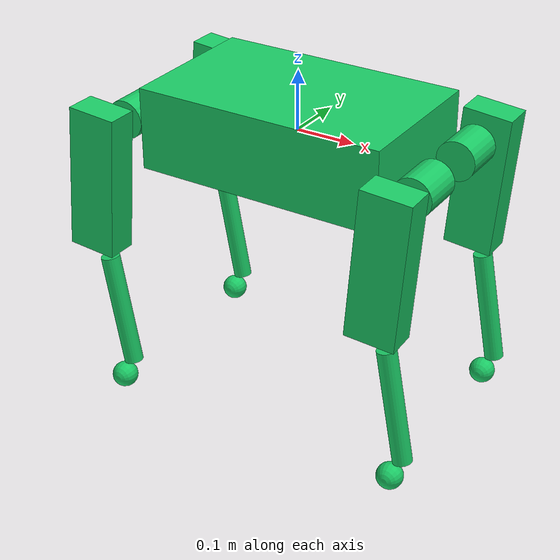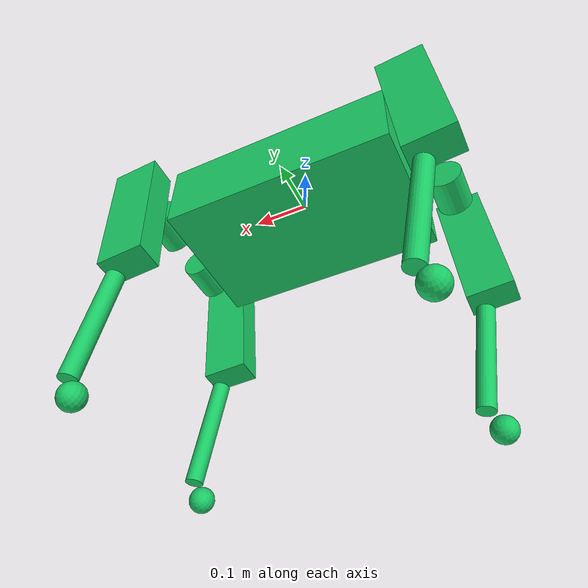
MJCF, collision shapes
<mujoco model="xz1">
                                                                                                                                <compiler angle="radian" meshdir="meshes/" inertiafromgeom="auto" inertiagrouprange="3 3" />
                                                                                                                                <asset>
                                                                    <mesh name="part_1" file="part_1.stl" scale="0.001 0.001 0.001" />
                                                                    <mesh name="part_3" file="part_3.stl" scale="0.001 0.001 0.001" />
                                                                    <mesh name="part_5" file="part_5.stl" scale="0.001 0.001 0.001" />
                                                                    <mesh name="part_7" file="part_7.stl" scale="0.001 0.001 0.001" />
                                                                    <mesh name="part_9" file="part_9.stl" scale="0.001 0.001 0.001" />
                                                                    <mesh name="part_11" file="part_11.stl" scale="0.001 0.001 0.001" />
                                                                    <mesh name="part_13" file="part_13.stl" scale="0.001 0.001 0.001" />
                                                                    <mesh name="part_15" file="part_15.stl" scale="0.001 0.001 0.001" />
                                                                    <mesh name="part_17" file="part_17.stl" scale="0.001 0.001 0.001" />
                                                                    <mesh name="part_19" file="part_19.stl" scale="0.001 0.001 0.001" />
                                                                    <mesh name="part_21" file="part_21.stl" scale="0.001 0.001 0.001" />
                                                                    <mesh name="part_23" file="part_23.stl" scale="0.001 0.001 0.001" />
                                                                    <mesh name="part_25" file="part_25.stl" scale="0.001 0.001 0.001" />
                                                                    <mesh name="part_27" file="part_27.stl" scale="0.001 0.001 0.001" />
                                                                    <mesh name="part_29" file="part_29.stl" scale="0.001 0.001 0.001" />
                                                                    <mesh name="part_31" file="part_31.stl" scale="0.001 0.001 0.001" />
                                                                    <mesh name="part_33" file="part_33.stl" scale="0.001 0.001 0.001" />
                                                                    <mesh name="part_35" file="part_35.stl" scale="0.001 0.001 0.001" />
                                                                    <mesh name="part_37" file="part_37.stl" scale="0.001 0.001 0.001" />
                                                                    <mesh name="part_39" file="part_39.stl" scale="0.001 0.001 0.001" />
                                                                    <mesh name="part_41" file="part_41.stl" scale="0.001 0.001 0.001" />
                                                                    <mesh name="part_43" file="part_43.stl" scale="0.001 0.001 0.001" />
                                                                    <mesh name="part_45" file="part_45.stl" scale="0.001 0.001 0.001" />
                                                                    <mesh name="part_47" file="part_47.stl" scale="0.001 0.001 0.001" />
                                                                    <mesh name="part_49" file="part_49.stl" scale="0.001 0.001 0.001" />
                                                                    <mesh name="part_51" file="part_51.stl" scale="0.001 0.001 0.001" />
                                                                    <mesh name="part_53" file="part_53.stl" scale="0.001 0.001 0.001" />
                                                                    <mesh name="part_55" file="part_55.stl" scale="0.001 0.001 0.001" />
                                                                    <mesh name="part_57" file="part_57.stl" scale="0.001 0.001 0.001" />
                                                                    <mesh name="part_59" file="part_59.stl" scale="0.001 0.001 0.001" />
                                                                    <mesh name="part_61" file="part_61.stl" scale="0.001 0.001 0.001" />
                                                                    <mesh name="part_63" file="part_63.stl" scale="0.001 0.001 0.001" />
                                                                    <mesh name="part_65" file="part_65.stl" scale="0.001 0.001 0.001" />
                                                                    <mesh name="part_67" file="part_67.stl" scale="0.001 0.001 0.001" />
                                                                    <mesh name="part_69" file="part_69.stl" scale="0.001 0.001 0.001" />
                                                                    <mesh name="part_71" file="part_71.stl" scale="0.001 0.001 0.001" />
                                                                    <mesh name="part_73" file="part_73.stl" scale="0.001 0.001 0.001" />
                                                                    <mesh name="part_75" file="part_75.stl" scale="0.001 0.001 0.001" />
                                                                    <mesh name="part_77" file="part_77.stl" scale="0.001 0.001 0.001" />
                                                                    <mesh name="part_79" file="part_79.stl" scale="0.001 0.001 0.001" />
                                                                    <mesh name="part_81" file="part_81.stl" scale="0.001 0.001 0.001" />
                                                                    <mesh name="part_83" file="part_83.stl" scale="0.001 0.001 0.001" />
                                                                    <mesh name="part_85" file="part_85.stl" scale="0.001 0.001 0.001" />
                                                                    <mesh name="part_87" file="part_87.stl" scale="0.001 0.001 0.001" />
                                                                    <mesh name="part_89" file="part_89.stl" scale="0.001 0.001 0.001" />
                                                                    <mesh name="part_91" file="part_91.stl" scale="0.001 0.001 0.001" />
                                                                    <mesh name="part_93" file="part_93.stl" scale="0.001 0.001 0.001" />
                                                                    <mesh name="part_95" file="part_95.stl" scale="0.001 0.001 0.001" />
                                                                    <mesh name="part_97" file="part_97.stl" scale="0.001 0.001 0.001" />
                                                                    <mesh name="part_99" file="part_99.stl" scale="0.001 0.001 0.001" />
                                                                    <mesh name="part_101" file="part_101.stl" scale="0.001 0.001 0.001" />
                                                                    <mesh name="part_103" file="part_103.stl" scale="0.001 0.001 0.001" />
                                                                    <mesh name="part_105" file="part_105.stl" scale="0.001 0.001 0.001" />
                                                                    <mesh name="part_107" file="part_107.stl" scale="0.001 0.001 0.001" />
                                                                    <mesh name="part_109" file="part_109.stl" scale="0.001 0.001 0.001" />
                                                                    <mesh name="part_111" file="part_111.stl" scale="0.001 0.001 0.001" />
                                                                    <mesh name="part_113" file="part_113.stl" scale="0.001 0.001 0.001" />
                                                                    <mesh name="part_115" file="part_115.stl" scale="0.001 0.001 0.001" />
                                                                    <mesh name="part_117" file="part_117.stl" scale="0.001 0.001 0.001" />
                                                                    <mesh name="part_119" file="part_119.stl" scale="0.001 0.001 0.001" />
                                                                    <mesh name="part_121" file="part_121.stl" scale="0.001 0.001 0.001" />
                                                                    <mesh name="part_123" file="part_123.stl" scale="0.001 0.001 0.001" />
                                                                    <mesh name="part_125" file="part_125.stl" scale="0.001 0.001 0.001" />
                                                                    <mesh name="part_127" file="part_127.stl" scale="0.001 0.001 0.001" />
                                                                    <mesh name="part_129" file="part_129.stl" scale="0.001 0.001 0.001" />
                                                                    <mesh name="part_131" file="part_131.stl" scale="0.001 0.001 0.001" />
                                                                    <mesh name="part_133" file="part_133.stl" scale="0.001 0.001 0.001" />
                                                                    <mesh name="part_135" file="part_135.stl" scale="0.001 0.001 0.001" />
                                                                    <mesh name="part_137" file="part_137.stl" scale="0.001 0.001 0.001" />
                                                                    <mesh name="part_139" file="part_139.stl" scale="0.001 0.001 0.001" />
                                                                    <mesh name="part_141" file="part_141.stl" scale="0.001 0.001 0.001" />
                                                                    <mesh name="part_143" file="part_143.stl" scale="0.001 0.001 0.001" />
                                                                    <mesh name="part_145" file="part_145.stl" scale="0.001 0.001 0.001" />
                                                                    <mesh name="part_147" file="part_147.stl" scale="0.001 0.001 0.001" />
                                                                    <mesh name="part_149" file="part_149.stl" scale="0.001 0.001 0.001" />
                                                                    <mesh name="part_151" file="part_151.stl" scale="0.001 0.001 0.001" />
                                                                    <mesh name="part_153" file="part_153.stl" scale="0.001 0.001 0.001" />
                                                                    <mesh name="part_155" file="part_155.stl" scale="0.001 0.001 0.001" />
                                                                    <mesh name="part_157" file="part_157.stl" scale="0.001 0.001 0.001" />
                                                                    <mesh name="part_159" file="part_159.stl" scale="0.001 0.001 0.001" />
                                                                    <mesh name="part_161" file="part_161.stl" scale="0.001 0.001 0.001" />
                                                                    <mesh name="part_163" file="part_163.stl" scale="0.001 0.001 0.001" />
                                                                    <mesh name="part_165" file="part_165.stl" scale="0.001 0.001 0.001" />
                                                                    <mesh name="part_167" file="part_167.stl" scale="0.001 0.001 0.001" />
                                                                    <mesh name="part_169" file="part_169.stl" scale="0.001 0.001 0.001" />
                                                                    <mesh name="part_171" file="part_171.stl" scale="0.001 0.001 0.001" />
                                                                    <mesh name="part_173" file="part_173.stl" scale="0.001 0.001 0.001" />
                                                                    <mesh name="part_175" file="part_175.stl" scale="0.001 0.001 0.001" />
                                                                    <mesh name="part_177" file="part_177.stl" scale="0.001 0.001 0.001" />
                                                                    <mesh name="part_179" file="part_179.stl" scale="0.001 0.001 0.001" />
                                                                    <mesh name="part_181" file="part_181.stl" scale="0.001 0.001 0.001" />
                                                                    <mesh name="part_183" file="part_183.stl" scale="0.001 0.001 0.001" />
                                                                    <mesh name="part_185" file="part_185.stl" scale="0.001 0.001 0.001" />
                                                                    <mesh name="part_187" file="part_187.stl" scale="0.001 0.001 0.001" />
                                                                    <mesh name="part_189" file="part_189.stl" scale="0.001 0.001 0.001" />
                                                                    <mesh name="part_191" file="part_191.stl" scale="0.001 0.001 0.001" />
                                                                    <mesh name="part_193" file="part_193.stl" scale="0.001 0.001 0.001" />
                                                                    <mesh name="part_195" file="part_195.stl" scale="0.001 0.001 0.001" />
                                                                    <mesh name="part_197" file="part_197.stl" scale="0.001 0.001 0.001" />
                                                                    <mesh name="part_199" file="part_199.stl" scale="0.001 0.001 0.001" />
                                                                    <mesh name="part_201" file="part_201.stl" scale="0.001 0.001 0.001" />
                                                                    <mesh name="part_203" file="part_203.stl" scale="0.001 0.001 0.001" />
                                                                    <mesh name="part_205" file="part_205.stl" scale="0.001 0.001 0.001" />
                                                                    <mesh name="part_207" file="part_207.stl" scale="0.001 0.001 0.001" />
                                                                    <mesh name="part_209" file="part_209.stl" scale="0.001 0.001 0.001" />
                                                                    <mesh name="part_211" file="part_211.stl" scale="0.001 0.001 0.001" />
                                                                    <mesh name="part_213" file="part_213.stl" scale="0.001 0.001 0.001" />
                                                                    <mesh name="part_215" file="part_215.stl" scale="0.001 0.001 0.001" />
                                                                    <mesh name="part_217" file="part_217.stl" scale="0.001 0.001 0.001" />
                                                                    <mesh name="part_219" file="part_219.stl" scale="0.001 0.001 0.001" />
                                                                    <mesh name="part_221" file="part_221.stl" scale="0.001 0.001 0.001" />
                                                                    <mesh name="part_223" file="part_223.stl" scale="0.001 0.001 0.001" />
                                                                    <mesh name="part_225" file="part_225.stl" scale="0.001 0.001 0.001" />
                                                                    <mesh name="part_227" file="part_227.stl" scale="0.001 0.001 0.001" />
                                                                    <mesh name="part_229" file="part_229.stl" scale="0.001 0.001 0.001" />
                                                                    <mesh name="part_231" file="part_231.stl" scale="0.001 0.001 0.001" />
                                                                    <mesh name="part_233" file="part_233.stl" scale="0.001 0.001 0.001" />
                                                                    <mesh name="part_235" file="part_235.stl" scale="0.001 0.001 0.001" />
                                                                    <mesh name="part_237" file="part_237.stl" scale="0.001 0.001 0.001" />
                                                                    <mesh name="part_239" file="part_239.stl" scale="0.001 0.001 0.001" />
                                                                    <mesh name="part_241" file="part_241.stl" scale="0.001 0.001 0.001" />
                                                                    <mesh name="part_243" file="part_243.stl" scale="0.001 0.001 0.001" />
                                                                    <mesh name="part_245" file="part_245.stl" scale="0.001 0.001 0.001" />
                                                                    <mesh name="part_247" file="part_247.stl" scale="0.001 0.001 0.001" />
                                                                    <mesh name="part_249" file="part_249.stl" scale="0.001 0.001 0.001" />
                                                                    <mesh name="part_251" file="part_251.stl" scale="0.001 0.001 0.001" />
                                                                    <mesh name="part_253" file="part_253.stl" scale="0.001 0.001 0.001" />
                                                                    <mesh name="part_255" file="part_255.stl" scale="0.001 0.001 0.001" />
                                                                    <mesh name="part_257" file="part_257.stl" scale="0.001 0.001 0.001" />
                                                                    <mesh name="part_259" file="part_259.stl" scale="0.001 0.001 0.001" />
                                                                    <mesh name="part_261" file="part_261.stl" scale="0.001 0.001 0.001" />
                                                                    <mesh name="part_263" file="part_263.stl" scale="0.001 0.001 0.001" />
                                                                    <mesh name="part_265" file="part_265.stl" scale="0.001 0.001 0.001" />
                                                                    <mesh name="part_267" file="part_267.stl" scale="0.001 0.001 0.001" />
                                                                    <mesh name="part_269" file="part_269.stl" scale="0.001 0.001 0.001" />
                                                                    <mesh name="part_271" file="part_271.stl" scale="0.001 0.001 0.001" />
                                                                    <mesh name="part_273" file="part_273.stl" scale="0.001 0.001 0.001" />
                                                                    <mesh name="part_275" file="part_275.stl" scale="0.001 0.001 0.001" />
                                                                    <mesh name="part_277" file="part_277.stl" scale="0.001 0.001 0.001" />
                                                                    <mesh name="part_279" file="part_279.stl" scale="0.001 0.001 0.001" />
                                                                    <mesh name="part_280" file="part_280.stl" scale="0.001 0.001 0.001" />
                                                                    <mesh name="part_281" file="part_281.stl" scale="0.001 0.001 0.001" />
                                                                    <mesh name="part_282" file="part_282.stl" scale="0.001 0.001 0.001" />
                                                                    <mesh name="part_283" file="part_283.stl" scale="0.001 0.001 0.001" />
                                                                    <mesh name="part_284" file="part_284.stl" scale="0.001 0.001 0.001" />
                                                                    <mesh name="part_285" file="part_285.stl" scale="0.001 0.001 0.001" />
                                                                    <mesh name="part_286" file="part_286.stl" scale="0.001 0.001 0.001" />
                                                                    <mesh name="part_287" file="part_287.stl" scale="0.001 0.001 0.001" />
                                                                    <mesh name="part_288" file="part_288.stl" scale="0.001 0.001 0.001" />
                                                                    <mesh name="part_289" file="part_289.stl" scale="0.001 0.001 0.001" />
                                                                    <mesh name="part_290" file="part_290.stl" scale="0.001 0.001 0.001" />
                                                                    <mesh name="part_291" file="part_291.stl" scale="0.001 0.001 0.001" />
                                                                    <mesh name="part_292" file="part_292.stl" scale="0.001 0.001 0.001" />
                                                                    <mesh name="part_293" file="part_293.stl" scale="0.001 0.001 0.001" />
                                                                    <mesh name="part_294" file="part_294.stl" scale="0.001 0.001 0.001" />
                                                                    <mesh name="part_295" file="part_295.stl" scale="0.001 0.001 0.001" />
                                                                    <mesh name="part_296" file="part_296.stl" scale="0.001 0.001 0.001" />
                                                                    <mesh name="part_297" file="part_297.stl" scale="0.001 0.001 0.001" />
                                                                    <mesh name="part_298" file="part_298.stl" scale="0.001 0.001 0.001" />
                                                                    <mesh name="part_299" file="part_299.stl" scale="0.001 0.001 0.001" />
                                                                    <mesh name="part_300" file="part_300.stl" scale="0.001 0.001 0.001" />
                                                                    <mesh name="part_301" file="part_301.stl" scale="0.001 0.001 0.001" />
                                                                    <mesh name="part_302" file="part_302.stl" scale="0.001 0.001 0.001" />
                                                                    <mesh name="part_303" file="part_303.stl" scale="0.001 0.001 0.001" />
                                                                    <mesh name="part_304" file="part_304.stl" scale="0.001 0.001 0.001" />
                                                                    <mesh name="part_305" file="part_305.stl" scale="0.001 0.001 0.001" />
                                                                    <mesh name="part_306" file="part_306.stl" scale="0.001 0.001 0.001" />
                                                                    <mesh name="part_307" file="part_307.stl" scale="0.001 0.001 0.001" />
                                                                    <mesh name="part_308" file="part_308.stl" scale="0.001 0.001 0.001" />
                                                                    <mesh name="part_309" file="part_309.stl" scale="0.001 0.001 0.001" />
                                                                    <mesh name="part_310" file="part_310.stl" scale="0.001 0.001 0.001" />
                                                                    <mesh name="part_311" file="part_311.stl" scale="0.001 0.001 0.001" />
                                                                    <mesh name="part_312" file="part_312.stl" scale="0.001 0.001 0.001" />
                                                                    <mesh name="part_313" file="part_313.stl" scale="0.001 0.001 0.001" />
                                                                    <mesh name="part_314" file="part_314.stl" scale="0.001 0.001 0.001" />
                                                                    <mesh name="part_315" file="part_315.stl" scale="0.001 0.001 0.001" />
                                                                    <mesh name="part_316" file="part_316.stl" scale="0.001 0.001 0.001" />
                                                                    <mesh name="part_317" file="part_317.stl" scale="0.001 0.001 0.001" />
                                                                    <mesh name="part_318" file="part_318.stl" scale="0.001 0.001 0.001" />
                                                                    <mesh name="part_319" file="part_319.stl" scale="0.001 0.001 0.001" />
                                                                    <mesh name="part_320" file="part_320.stl" scale="0.001 0.001 0.001" />
                                                                    <mesh name="part_321" file="part_321.stl" scale="0.001 0.001 0.001" />
                                                                    <mesh name="part_322" file="part_322.stl" scale="0.001 0.001 0.001" />
                                                                    <mesh name="part_323" file="part_323.stl" scale="0.001 0.001 0.001" />
                                                                    <mesh name="part_324" file="part_324.stl" scale="0.001 0.001 0.001" />
                                                                    <mesh name="part_325" file="part_325.stl" scale="0.001 0.001 0.001" />
                                                                    <mesh name="part_326" file="part_326.stl" scale="0.001 0.001 0.001" />
                                                                    <mesh name="part_327" file="part_327.stl" scale="0.001 0.001 0.001" />
                                                                    <mesh name="part_328" file="part_328.stl" scale="0.001 0.001 0.001" />
                                                                    <mesh name="part_329" file="part_329.stl" scale="0.001 0.001 0.001" />
                                                                    <mesh name="part_330" file="part_330.stl" scale="0.001 0.001 0.001" />
                                                                    <mesh name="part_331" file="part_331.stl" scale="0.001 0.001 0.001" />
                                                                    <mesh name="part_332" file="part_332.stl" scale="0.001 0.001 0.001" />
                                                                    <mesh name="part_333" file="part_333.stl" scale="0.001 0.001 0.001" />
                                                                    <mesh name="part_334" file="part_334.stl" scale="0.001 0.001 0.001" />
                                                                    <mesh name="part_335" file="part_335.stl" scale="0.001 0.001 0.001" />
                                                                    <mesh name="part_336" file="part_336.stl" scale="0.001 0.001 0.001" />
                                                                    <mesh name="part_337" file="part_337.stl" scale="0.001 0.001 0.001" />
                                                                    <mesh name="part_338" file="part_338.stl" scale="0.001 0.001 0.001" />
                                                                    <mesh name="part_339" file="part_339.stl" scale="0.001 0.001 0.001" />
                                                                    <mesh name="part_340" file="part_340.stl" scale="0.001 0.001 0.001" />
                                                                    <mesh name="part_341" file="part_341.stl" scale="0.001 0.001 0.001" />
                                                                    <mesh name="part_342" file="part_342.stl" scale="0.001 0.001 0.001" />
                                                                    <mesh name="part_343" file="part_343.stl" scale="0.001 0.001 0.001" />
                                                                    <mesh name="part_344" file="part_344.stl" scale="0.001 0.001 0.001" />
                                                                    <mesh name="part_345" file="part_345.stl" scale="0.001 0.001 0.001" />
                                                                    <mesh name="part_346" file="part_346.stl" scale="0.001 0.001 0.001" />
                                                                    <mesh name="part_347" file="part_347.stl" scale="0.001 0.001 0.001" />
                                                                    <mesh name="part_348" file="part_348.stl" scale="0.001 0.001 0.001" />
                                                                    <mesh name="part_349" file="part_349.stl" scale="0.001 0.001 0.001" />
                                                                    <mesh name="part_350" file="part_350.stl" scale="0.001 0.001 0.001" />
                                                                    <mesh name="part_351" file="part_351.stl" scale="0.001 0.001 0.001" />
                                                                    <mesh name="part_352" file="part_352.stl" scale="0.001 0.001 0.001" />
                                                                    <mesh name="part_353" file="part_353.stl" scale="0.001 0.001 0.001" />
                                                                    <mesh name="part_354" file="part_354.stl" scale="0.001 0.001 0.001" />
                                                                    <mesh name="part_355" file="part_355.stl" scale="0.001 0.001 0.001" />
                                                                    <mesh name="part_356" file="part_356.stl" scale="0.001 0.001 0.001" />
                                                                    <mesh name="part_357" file="part_357.stl" scale="0.001 0.001 0.001" />
                                                                    <mesh name="part_358" file="part_358.stl" scale="0.001 0.001 0.001" />
                                                                    <mesh name="part_359" file="part_359.stl" scale="0.001 0.001 0.001" />
                                                                    <mesh name="part_360" file="part_360.stl" scale="0.001 0.001 0.001" />
                                                                    <mesh name="part_361" file="part_361.stl" scale="0.001 0.001 0.001" />
                                                                    <mesh name="part_362" file="part_362.stl" scale="0.001 0.001 0.001" />
                                                                    <mesh name="part_363" file="part_363.stl" scale="0.001 0.001 0.001" />
                                                                    <mesh name="part_364" file="part_364.stl" scale="0.001 0.001 0.001" />
                                                                    <mesh name="part_365" file="part_365.stl" scale="0.001 0.001 0.001" />
                                                                    <mesh name="part_366" file="part_366.stl" scale="0.001 0.001 0.001" />
                                                                    <mesh name="part_367" file="part_367.stl" scale="0.001 0.001 0.001" />
                                                                    <mesh name="part_368" file="part_368.stl" scale="0.001 0.001 0.001" />
                                                                    <mesh name="part_369" file="part_369.stl" scale="0.001 0.001 0.001" />
                                                                    <mesh name="part_370" file="part_370.stl" scale="0.001 0.001 0.001" />
                                                                    <mesh name="part_371" file="part_371.stl" scale="0.001 0.001 0.001" />
                                                                    <mesh name="part_372" file="part_372.stl" scale="0.001 0.001 0.001" />
                                                                    <mesh name="part_373" file="part_373.stl" scale="0.001 0.001 0.001" />
                                                                    <mesh name="part_374" file="part_374.stl" scale="0.001 0.001 0.001" />
                                                                    <mesh name="part_375" file="part_375.stl" scale="0.001 0.001 0.001" />
                                                                    <mesh name="part_376" file="part_376.stl" scale="0.001 0.001 0.001" />
                                                                    <mesh name="part_377" file="part_377.stl" scale="0.001 0.001 0.001" />
                                                                    <mesh name="part_378" file="part_378.stl" scale="0.001 0.001 0.001" />
                                                                    <mesh name="part_379" file="part_379.stl" scale="0.001 0.001 0.001" />
                                                                    <mesh name="part_380" file="part_380.stl" scale="0.001 0.001 0.001" />
                                                                    <mesh name="part_381" file="part_381.stl" scale="0.001 0.001 0.001" />
                                                                    <mesh name="part_382" file="part_382.stl" scale="0.001 0.001 0.001" />
                                                                    <mesh name="part_383" file="part_383.stl" scale="0.001 0.001 0.001" />
                                                                    <mesh name="part_384" file="part_384.stl" scale="0.001 0.001 0.001" />
                                                                    <mesh name="part_385" file="part_385.stl" scale="0.001 0.001 0.001" />
                                                                    <mesh name="part_386" file="part_386.stl" scale="0.001 0.001 0.001" />
                                                                    <mesh name="part_387" file="part_387.stl" scale="0.001 0.001 0.001" />
                                                                    <mesh name="part_388" file="part_388.stl" scale="0.001 0.001 0.001" />
                                                                    <mesh name="part_389" file="part_389.stl" scale="0.001 0.001 0.001" />
                                                                    <mesh name="part_390" file="part_390.stl" scale="0.001 0.001 0.001" />
                                                                    <mesh name="part_391" file="part_391.stl" scale="0.001 0.001 0.001" />
                                                                    <mesh name="part_392" file="part_392.stl" scale="0.001 0.001 0.001" />
                                                                    <mesh name="part_393" file="part_393.stl" scale="0.001 0.001 0.001" />
                                                                    <mesh name="part_394" file="part_394.stl" scale="0.001 0.001 0.001" />
                                                                    <mesh name="part_395" file="part_395.stl" scale="0.001 0.001 0.001" />
                                                                    <mesh name="part_396" file="part_396.stl" scale="0.001 0.001 0.001" />
                                                                    <mesh name="part_397" file="part_397.stl" scale="0.001 0.001 0.001" />
                                                                    <mesh name="part_398" file="part_398.stl" scale="0.001 0.001 0.001" />
                                                                    <mesh name="part_399" file="part_399.stl" scale="0.001 0.001 0.001" />
                                                                    <mesh name="part_400" file="part_400.stl" scale="0.001 0.001 0.001" />
                                                                    <mesh name="part_401" file="part_401.stl" scale="0.001 0.001 0.001" />
                                                                    <mesh name="part_402" file="part_402.stl" scale="0.001 0.001 0.001" />
                                                                    <mesh name="part_403" file="part_403.stl" scale="0.001 0.001 0.001" />
                                                                    <mesh name="part_404" file="part_404.stl" scale="0.001 0.001 0.001" />
                                                                    <mesh name="part_405" file="part_405.stl" scale="0.001 0.001 0.001" />
                                                                    <mesh name="part_406" file="part_406.stl" scale="0.001 0.001 0.001" />
                                                                    <mesh name="part_407" file="part_407.stl" scale="0.001 0.001 0.001" />
                                                                    <mesh name="part_408" file="part_408.stl" scale="0.001 0.001 0.001" />
                                                                    <mesh name="part_409" file="part_409.stl" scale="0.001 0.001 0.001" />
                                                                    <mesh name="part_410" file="part_410.stl" scale="0.001 0.001 0.001" />
                                                                    <mesh name="part_411" file="part_411.stl" scale="0.001 0.001 0.001" />
                                                                    <mesh name="part_412" file="part_412.stl" scale="0.001 0.001 0.001" />
                                                                    <mesh name="part_413" file="part_413.stl" scale="0.001 0.001 0.001" />
                                                                    <mesh name="part_414" file="part_414.stl" scale="0.001 0.001 0.001" />
                                                                    <mesh name="part_415" file="part_415.stl" scale="0.001 0.001 0.001" />
                                                                    <mesh name="part_416" file="part_416.stl" scale="0.001 0.001 0.001" />
                                                                    <mesh name="part_417" file="part_417.stl" scale="0.001 0.001 0.001" />
                                                                    <mesh name="part_418" file="part_418.stl" scale="0.001 0.001 0.001" />
                                                                    <mesh name="part_420" file="part_420.stl" scale="0.001 0.001 0.001" />
                                                                    <mesh name="part_422" file="part_422.stl" scale="0.001 0.001 0.001" />
                                                                    <mesh name="part_424" file="part_424.stl" scale="0.001 0.001 0.001" />
                                                                    <mesh name="part_426" file="part_426.stl" scale="0.001 0.001 0.001" />
                                                                    <mesh name="part_428" file="part_428.stl" scale="0.001 0.001 0.001" />
                                                                    <mesh name="part_430" file="part_430.stl" scale="0.001 0.001 0.001" />
                                                                    <mesh name="part_432" file="part_432.stl" scale="0.001 0.001 0.001" />
                                                                    <mesh name="part_434" file="part_434.stl" scale="0.001 0.001 0.001" />
                                                                    <mesh name="part_436" file="part_436.stl" scale="0.001 0.001 0.001" />
                                                                    <mesh name="part_438" file="part_438.stl" scale="0.001 0.001 0.001" />
                                                                    <mesh name="part_440" file="part_440.stl" scale="0.001 0.001 0.001" />
                                                                    <mesh name="part_442" file="part_442.stl" scale="0.001 0.001 0.001" />
                                                                    <mesh name="part_444" file="part_444.stl" scale="0.001 0.001 0.001" />
                                                                    <mesh name="part_446" file="part_446.stl" scale="0.001 0.001 0.001" />
                                                                    <mesh name="part_448" file="part_448.stl" scale="0.001 0.001 0.001" />
                                                                    <mesh name="part_450" file="part_450.stl" scale="0.001 0.001 0.001" />
                                                                    <mesh name="part_452" file="part_452.stl" scale="0.001 0.001 0.001" />
                                                                    <mesh name="part_454" file="part_454.stl" scale="0.001 0.001 0.001" />
                                                                    <mesh name="part_456" file="part_456.stl" scale="0.001 0.001 0.001" />
                                                                    <mesh name="part_458" file="part_458.stl" scale="0.001 0.001 0.001" />
                                                                    <mesh name="part_460" file="part_460.stl" scale="0.001 0.001 0.001" />
                                                                    <mesh name="part_462" file="part_462.stl" scale="0.001 0.001 0.001" />
                                                                    <mesh name="part_464" file="part_464.stl" scale="0.001 0.001 0.001" />
                                                                    <mesh name="part_466" file="part_466.stl" scale="0.001 0.001 0.001" />
                                                                    <mesh name="part_468" file="part_468.stl" scale="0.001 0.001 0.001" />
                                                                    <mesh name="part_470" file="part_470.stl" scale="0.001 0.001 0.001" />
                                                                    <mesh name="part_472" file="part_472.stl" scale="0.001 0.001 0.001" />
                                                                    <mesh name="part_474" file="part_474.stl" scale="0.001 0.001 0.001" />
                                                                    <mesh name="part_476" file="part_476.stl" scale="0.001 0.001 0.001" />
                                                                    <mesh name="part_478" file="part_478.stl" scale="0.001 0.001 0.001" />
                                                                    <mesh name="part_480" file="part_480.stl" scale="0.001 0.001 0.001" />
                                                                    <mesh name="part_481" file="part_481.stl" scale="0.001 0.001 0.001" />
                                                                    <mesh name="part_482" file="part_482.stl" scale="0.001 0.001 0.001" />
                                                                    <mesh name="part_483" file="part_483.stl" scale="0.001 0.001 0.001" />
                                                                    <mesh name="part_484" file="part_484.stl" scale="0.001 0.001 0.001" />
                                                                    <mesh name="part_485" file="part_485.stl" scale="0.001 0.001 0.001" />
                                                                    <mesh name="part_486" file="part_486.stl" scale="0.001 0.001 0.001" />
                                                                    <mesh name="part_487" file="part_487.stl" scale="0.001 0.001 0.001" />
                                                                    <mesh name="part_488" file="part_488.stl" scale="0.001 0.001 0.001" />
                                                                    <mesh name="part_489" file="part_489.stl" scale="0.001 0.001 0.001" />
                                                                    <mesh name="part_490" file="part_490.stl" scale="0.001 0.001 0.001" />
                                                                    <mesh name="part_491" file="part_491.stl" scale="0.001 0.001 0.001" />
                                                                    <mesh name="part_492" file="part_492.stl" scale="0.001 0.001 0.001" />
                                                                    <mesh name="part_493" file="part_493.stl" scale="0.001 0.001 0.001" />
                                                                    <mesh name="part_494" file="part_494.stl" scale="0.001 0.001 0.001" />
                                                                    <mesh name="part_495" file="part_495.stl" scale="0.001 0.001 0.001" />
                                                                    <mesh name="part_496" file="part_496.stl" scale="0.001 0.001 0.001" />
                                                                    <mesh name="part_497" file="part_497.stl" scale="0.001 0.001 0.001" />
                                                                    <mesh name="part_498" file="part_498.stl" scale="0.001 0.001 0.001" />
                                                                    <mesh name="part_499" file="part_499.stl" scale="0.001 0.001 0.001" />
                                                                    <mesh name="part_500" file="part_500.stl" scale="0.001 0.001 0.001" />
                                                                    <mesh name="part_501" file="part_501.stl" scale="0.001 0.001 0.001" />
                                                                    <mesh name="part_502" file="part_502.stl" scale="0.001 0.001 0.001" />
                                                                    <mesh name="part_503" file="part_503.stl" scale="0.001 0.001 0.001" />
                                                                    <mesh name="part_504" file="part_504.stl" scale="0.001 0.001 0.001" />
                                                                    <mesh name="part_505" file="part_505.stl" scale="0.001 0.001 0.001" />
                                                                    <mesh name="part_506" file="part_506.stl" scale="0.001 0.001 0.001" />
                                                                    <mesh name="part_507" file="part_507.stl" scale="0.001 0.001 0.001" />
                                                                    <mesh name="part_508" file="part_508.stl" scale="0.001 0.001 0.001" />
                                                                    <mesh name="part_509" file="part_509.stl" scale="0.001 0.001 0.001" />
                                                                    <mesh name="part_510" file="part_510.stl" scale="0.001 0.001 0.001" />
                                                                    <mesh name="part_511" file="part_511.stl" scale="0.001 0.001 0.001" />
                                                                    <mesh name="part_513" file="part_513.stl" scale="0.001 0.001 0.001" />
                                                                    <mesh name="part_515" file="part_515.stl" scale="0.001 0.001 0.001" />
                                                                    <mesh name="part_517" file="part_517.stl" scale="0.001 0.001 0.001" />
                                                                    <mesh name="part_519" file="part_519.stl" scale="0.001 0.001 0.001" />
                                                                    <mesh name="part_521" file="part_521.stl" scale="0.001 0.001 0.001" />
                                                                    <mesh name="part_523" file="part_523.stl" scale="0.001 0.001 0.001" />
                                                                    <mesh name="part_525" file="part_525.stl" scale="0.001 0.001 0.001" />
                                                                    <mesh name="part_527" file="part_527.stl" scale="0.001 0.001 0.001" />
                                                                    <mesh name="part_529" file="part_529.stl" scale="0.001 0.001 0.001" />
                                                                    <mesh name="part_531" file="part_531.stl" scale="0.001 0.001 0.001" />
                                                                    <mesh name="part_533" file="part_533.stl" scale="0.001 0.001 0.001" />
                                                                    <mesh name="part_535" file="part_535.stl" scale="0.001 0.001 0.001" />
                                                                    <mesh name="part_537" file="part_537.stl" scale="0.001 0.001 0.001" />
                                                                    <mesh name="part_539" file="part_539.stl" scale="0.001 0.001 0.001" />
                                                                    <mesh name="part_541" file="part_541.stl" scale="0.001 0.001 0.001" />
                                                                    <mesh name="part_543" file="part_543.stl" scale="0.001 0.001 0.001" />
                                                                    <mesh name="part_544" file="part_544.stl" scale="0.001 0.001 0.001" />
                                                                    <mesh name="part_545" file="part_545.stl" scale="0.001 0.001 0.001" />
                                                                    <mesh name="part_546" file="part_546.stl" scale="0.001 0.001 0.001" />
                                                                    <mesh name="part_547" file="part_547.stl" scale="0.001 0.001 0.001" />
                                                                    <mesh name="part_548" file="part_548.stl" scale="0.001 0.001 0.001" />
                                                                    <mesh name="part_549" file="part_549.stl" scale="0.001 0.001 0.001" />
                                                                    <mesh name="part_550" file="part_550.stl" scale="0.001 0.001 0.001" />
                                                                    <mesh name="part_551" file="part_551.stl" scale="0.001 0.001 0.001" />
                                                                    <mesh name="part_552" file="part_552.stl" scale="0.001 0.001 0.001" />
                                                                    <mesh name="part_553" file="part_553.stl" scale="0.001 0.001 0.001" />
                                                                    <mesh name="part_554" file="part_554.stl" scale="0.001 0.001 0.001" />
                                                                    <mesh name="part_555" file="part_555.stl" scale="0.001 0.001 0.001" />
                                                                    <mesh name="part_556" file="part_556.stl" scale="0.001 0.001 0.001" />
                                                                    <mesh name="part_557" file="part_557.stl" scale="0.001 0.001 0.001" />
                                                                    <mesh name="part_558" file="part_558.stl" scale="0.001 0.001 0.001" />
                                                                    <mesh name="part_559" file="part_559.stl" scale="0.001 0.001 0.001" />
                                                                    <mesh name="part_561" file="part_561.stl" scale="0.001 0.001 0.001" />
                                                                    <mesh name="part_563" file="part_563.stl" scale="0.001 0.001 0.001" />
                                                                    <mesh name="part_565" file="part_565.stl" scale="0.001 0.001 0.001" />
                                                                    <mesh name="part_567" file="part_567.stl" scale="0.001 0.001 0.001" />
                                                                    <mesh name="part_569" file="part_569.stl" scale="0.001 0.001 0.001" />
                                                                    <mesh name="part_571" file="part_571.stl" scale="0.001 0.001 0.001" />
                                                                    <mesh name="part_573" file="part_573.stl" scale="0.001 0.001 0.001" />
                                                                    <mesh name="part_575" file="part_575.stl" scale="0.001 0.001 0.001" />
                                                                    <mesh name="part_577" file="part_577.stl" scale="0.001 0.001 0.001" />
                                                                    <mesh name="part_579" file="part_579.stl" scale="0.001 0.001 0.001" />
                                                                    <mesh name="part_581" file="part_581.stl" scale="0.001 0.001 0.001" />
                                                                    <mesh name="part_583" file="part_583.stl" scale="0.001 0.001 0.001" />
                                                                    <mesh name="part_585" file="part_585.stl" scale="0.001 0.001 0.001" />
                                                                    <mesh name="part_587" file="part_587.stl" scale="0.001 0.001 0.001" />
                                                                    <mesh name="part_588" file="part_588.stl" scale="0.001 0.001 0.001" />
                                                                    <mesh name="part_589" file="part_589.stl" scale="0.001 0.001 0.001" />
                                                                    <mesh name="part_590" file="part_590.stl" scale="0.001 0.001 0.001" />
                                                                    <mesh name="part_591" file="part_591.stl" scale="0.001 0.001 0.001" />
                                                                    <mesh name="part_592" file="part_592.stl" scale="0.001 0.001 0.001" />
                                                                    <mesh name="part_593" file="part_593.stl" scale="0.001 0.001 0.001" />
                                                                    <mesh name="part_594" file="part_594.stl" scale="0.001 0.001 0.001" />
                                                                    <mesh name="part_595" file="part_595.stl" scale="0.001 0.001 0.001" />
                                                                    <mesh name="part_596" file="part_596.stl" scale="0.001 0.001 0.001" />
                                                                    <mesh name="part_597" file="part_597.stl" scale="0.001 0.001 0.001" />
                                                                    <mesh name="part_598" file="part_598.stl" scale="0.001 0.001 0.001" />
                                                                    <mesh name="part_599" file="part_599.stl" scale="0.001 0.001 0.001" />
                                                                    <mesh name="part_600" file="part_600.stl" scale="0.001 0.001 0.001" />
                                                                    <mesh name="part_601" file="part_601.stl" scale="0.001 0.001 0.001" />
                                                                    <mesh name="part_603" file="part_603.stl" scale="0.001 0.001 0.001" />
                                                                    <mesh name="part_605" file="part_605.stl" scale="0.001 0.001 0.001" />
                                                                    <mesh name="part_607" file="part_607.stl" scale="0.001 0.001 0.001" />
                                                                    <mesh name="part_609" file="part_609.stl" scale="0.001 0.001 0.001" />
                                                                    <mesh name="part_610" file="part_610.stl" scale="0.001 0.001 0.001" />
                                                                    <mesh name="part_611" file="part_611.stl" scale="0.001 0.001 0.001" />
                                                                    <mesh name="part_612" file="part_612.stl" scale="0.001 0.001 0.001" />
                                                                    <mesh name="part_613" file="part_613.stl" scale="0.001 0.001 0.001" />
                                                                    <mesh name="part_615" file="part_615.stl" scale="0.001 0.001 0.001" />
                                                                    <mesh name="part_617" file="part_617.stl" scale="0.001 0.001 0.001" />
                                                                    <mesh name="part_619" file="part_619.stl" scale="0.001 0.001 0.001" />
                                                                    <mesh name="part_621" file="part_621.stl" scale="0.001 0.001 0.001" />
                                                                    <mesh name="part_623" file="part_623.stl" scale="0.001 0.001 0.001" />
                                                                    <mesh name="part_625" file="part_625.stl" scale="0.001 0.001 0.001" />
                                                                    <mesh name="part_627" file="part_627.stl" scale="0.001 0.001 0.001" />
                                                                    <mesh name="part_629" file="part_629.stl" scale="0.001 0.001 0.001" />
                                                                    <mesh name="part_631" file="part_631.stl" scale="0.001 0.001 0.001" />
                                                                    <mesh name="part_633" file="part_633.stl" scale="0.001 0.001 0.001" />
                                                                    <mesh name="part_635" file="part_635.stl" scale="0.001 0.001 0.001" />
                                                                    <mesh name="part_637" file="part_637.stl" scale="0.001 0.001 0.001" />
                                                                    <mesh name="part_639" file="part_639.stl" scale="0.001 0.001 0.001" />
                                                                    <mesh name="part_641" file="part_641.stl" scale="0.001 0.001 0.001" />
                                                                    <mesh name="part_643" file="part_643.stl" scale="0.001 0.001 0.001" />
                                                                    <mesh name="part_645" file="part_645.stl" scale="0.001 0.001 0.001" />
                                                                    <mesh name="part_647" file="part_647.stl" scale="0.001 0.001 0.001" />
                                                                    <mesh name="part_649" file="part_649.stl" scale="0.001 0.001 0.001" />
                                                                    <mesh name="part_651" file="part_651.stl" scale="0.001 0.001 0.001" />
                                                                    <mesh name="part_653" file="part_653.stl" scale="0.001 0.001 0.001" />
                                                                    <mesh name="part_655" file="part_655.stl" scale="0.001 0.001 0.001" />
                                                                    <mesh name="part_657" file="part_657.stl" scale="0.001 0.001 0.001" />
                                                                    <mesh name="part_659" file="part_659.stl" scale="0.001 0.001 0.001" />
                                                                    <mesh name="part_661" file="part_661.stl" scale="0.001 0.001 0.001" />
                                                                    <mesh name="part_663" file="part_663.stl" scale="0.001 0.001 0.001" />
                                                                    <mesh name="part_665" file="part_665.stl" scale="0.001 0.001 0.001" />
                                                                    <mesh name="part_667" file="part_667.stl" scale="0.001 0.001 0.001" />
                                                                    <mesh name="part_669" file="part_669.stl" scale="0.001 0.001 0.001" />
                                                                    <mesh name="part_671" file="part_671.stl" scale="0.001 0.001 0.001" />
                                                                    <mesh name="part_673" file="part_673.stl" scale="0.001 0.001 0.001" />
                                                                    <mesh name="part_675" file="part_675.stl" scale="0.001 0.001 0.001" />
                                                                    <mesh name="part_676" file="part_676.stl" scale="0.001 0.001 0.001" />
                                                                    <mesh name="part_677" file="part_677.stl" scale="0.001 0.001 0.001" />
                                                                    <mesh name="part_678" file="part_678.stl" scale="0.001 0.001 0.001" />
                                                                    <mesh name="part_679" file="part_679.stl" scale="0.001 0.001 0.001" />
                                                                    <mesh name="part_680" file="part_680.stl" scale="0.001 0.001 0.001" />
                                                                    <mesh name="part_681" file="part_681.stl" scale="0.001 0.001 0.001" />
                                                                    <mesh name="part_682" file="part_682.stl" scale="0.001 0.001 0.001" />
                                                                    <mesh name="part_683" file="part_683.stl" scale="0.001 0.001 0.001" />
                                                                    <mesh name="part_684" file="part_684.stl" scale="0.001 0.001 0.001" />
                                                                    <mesh name="part_685" file="part_685.stl" scale="0.001 0.001 0.001" />
                                                                    <mesh name="part_686" file="part_686.stl" scale="0.001 0.001 0.001" />
                                                                    <mesh name="part_687" file="part_687.stl" scale="0.001 0.001 0.001" />
                                                                    <mesh name="part_688" file="part_688.stl" scale="0.001 0.001 0.001" />
                                                                    <mesh name="part_689" file="part_689.stl" scale="0.001 0.001 0.001" />
                                                                    <mesh name="part_690" file="part_690.stl" scale="0.001 0.001 0.001" />
                                                                    <mesh name="part_691" file="part_691.stl" scale="0.001 0.001 0.001" />
                                                                    <mesh name="part_692" file="part_692.stl" scale="0.001 0.001 0.001" />
                                                                    <mesh name="part_693" file="part_693.stl" scale="0.001 0.001 0.001" />
                                                                    <mesh name="part_694" file="part_694.stl" scale="0.001 0.001 0.001" />
                                                                    <mesh name="part_695" file="part_695.stl" scale="0.001 0.001 0.001" />
                                                                    <mesh name="part_696" file="part_696.stl" scale="0.001 0.001 0.001" />
                                                                    <mesh name="part_697" file="part_697.stl" scale="0.001 0.001 0.001" />
                                                                    <mesh name="part_698" file="part_698.stl" scale="0.001 0.001 0.001" />
                                                                    <mesh name="part_699" file="part_699.stl" scale="0.001 0.001 0.001" />
                                                                    <mesh name="part_700" file="part_700.stl" scale="0.001 0.001 0.001" />
                                                                    <mesh name="part_701" file="part_701.stl" scale="0.001 0.001 0.001" />
                                                                    <mesh name="part_702" file="part_702.stl" scale="0.001 0.001 0.001" />
                                                                    <mesh name="part_703" file="part_703.stl" scale="0.001 0.001 0.001" />
                                                                    <mesh name="part_704" file="part_704.stl" scale="0.001 0.001 0.001" />
                                                                    <mesh name="part_705" file="part_705.stl" scale="0.001 0.001 0.001" />
                                                                    <mesh name="part_706" file="part_706.stl" scale="0.001 0.001 0.001" />
                                                                    <mesh name="part_708" file="part_708.stl" scale="0.001 0.001 0.001" />
                                                                    <mesh name="part_710" file="part_710.stl" scale="0.001 0.001 0.001" />
                                                                    <mesh name="part_712" file="part_712.stl" scale="0.001 0.001 0.001" />
                                                                    <mesh name="part_714" file="part_714.stl" scale="0.001 0.001 0.001" />
                                                                    <mesh name="part_716" file="part_716.stl" scale="0.001 0.001 0.001" />
                                                                    <mesh name="part_718" file="part_718.stl" scale="0.001 0.001 0.001" />
                                                                    <mesh name="part_720" file="part_720.stl" scale="0.001 0.001 0.001" />
                                                                    <mesh name="part_722" file="part_722.stl" scale="0.001 0.001 0.001" />
                                                                    <mesh name="part_724" file="part_724.stl" scale="0.001 0.001 0.001" />
                                                                    <mesh name="part_726" file="part_726.stl" scale="0.001 0.001 0.001" />
                                                                    <mesh name="part_728" file="part_728.stl" scale="0.001 0.001 0.001" />
                                                                    <mesh name="part_730" file="part_730.stl" scale="0.001 0.001 0.001" />
                                                                    <mesh name="part_732" file="part_732.stl" scale="0.001 0.001 0.001" />
                                                                    <mesh name="part_734" file="part_734.stl" scale="0.001 0.001 0.001" />
                                                                    <mesh name="part_736" file="part_736.stl" scale="0.001 0.001 0.001" />
                                                                    <mesh name="part_738" file="part_738.stl" scale="0.001 0.001 0.001" />
                                                                    <mesh name="part_739" file="part_739.stl" scale="0.001 0.001 0.001" />
                                                                    <mesh name="part_740" file="part_740.stl" scale="0.001 0.001 0.001" />
                                                                    <mesh name="part_741" file="part_741.stl" scale="0.001 0.001 0.001" />
                                                                    <mesh name="part_742" file="part_742.stl" scale="0.001 0.001 0.001" />
                                                                    <mesh name="part_743" file="part_743.stl" scale="0.001 0.001 0.001" />
                                                                    <mesh name="part_744" file="part_744.stl" scale="0.001 0.001 0.001" />
                                                                    <mesh name="part_745" file="part_745.stl" scale="0.001 0.001 0.001" />
                                                                    <mesh name="part_746" file="part_746.stl" scale="0.001 0.001 0.001" />
                                                                    <mesh name="part_747" file="part_747.stl" scale="0.001 0.001 0.001" />
                                                                    <mesh name="part_748" file="part_748.stl" scale="0.001 0.001 0.001" />
                                                                    <mesh name="part_749" file="part_749.stl" scale="0.001 0.001 0.001" />
                                                                    <mesh name="part_750" file="part_750.stl" scale="0.001 0.001 0.001" />
                                                                    <mesh name="part_751" file="part_751.stl" scale="0.001 0.001 0.001" />
                                                                    <mesh name="part_752" file="part_752.stl" scale="0.001 0.001 0.001" />
                                                                    <mesh name="part_753" file="part_753.stl" scale="0.001 0.001 0.001" />
                                                                    <mesh name="part_754" file="part_754.stl" scale="0.001 0.001 0.001" />
                                                                    <mesh name="part_756" file="part_756.stl" scale="0.001 0.001 0.001" />
                                                                    <mesh name="part_758" file="part_758.stl" scale="0.001 0.001 0.001" />
                                                                    <mesh name="part_760" file="part_760.stl" scale="0.001 0.001 0.001" />
                                                                    <mesh name="part_762" file="part_762.stl" scale="0.001 0.001 0.001" />
                                                                    <mesh name="part_764" file="part_764.stl" scale="0.001 0.001 0.001" />
                                                                    <mesh name="part_766" file="part_766.stl" scale="0.001 0.001 0.001" />
                                                                    <mesh name="part_768" file="part_768.stl" scale="0.001 0.001 0.001" />
                                                                    <mesh name="part_770" file="part_770.stl" scale="0.001 0.001 0.001" />
                                                                    <mesh name="part_772" file="part_772.stl" scale="0.001 0.001 0.001" />
                                                                    <mesh name="part_774" file="part_774.stl" scale="0.001 0.001 0.001" />
                                                                    <mesh name="part_776" file="part_776.stl" scale="0.001 0.001 0.001" />
                                                                    <mesh name="part_778" file="part_778.stl" scale="0.001 0.001 0.001" />
                                                                    <mesh name="part_780" file="part_780.stl" scale="0.001 0.001 0.001" />
                                                                    <mesh name="part_782" file="part_782.stl" scale="0.001 0.001 0.001" />
                                                                    <mesh name="part_783" file="part_783.stl" scale="0.001 0.001 0.001" />
                                                                    <mesh name="part_784" file="part_784.stl" scale="0.001 0.001 0.001" />
                                                                    <mesh name="part_785" file="part_785.stl" scale="0.001 0.001 0.001" />
                                                                    <mesh name="part_786" file="part_786.stl" scale="0.001 0.001 0.001" />
                                                                    <mesh name="part_787" file="part_787.stl" scale="0.001 0.001 0.001" />
                                                                    <mesh name="part_788" file="part_788.stl" scale="0.001 0.001 0.001" />
                                                                    <mesh name="part_789" file="part_789.stl" scale="0.001 0.001 0.001" />
                                                                    <mesh name="part_790" file="part_790.stl" scale="0.001 0.001 0.001" />
                                                                    <mesh name="part_791" file="part_791.stl" scale="0.001 0.001 0.001" />
                                                                    <mesh name="part_792" file="part_792.stl" scale="0.001 0.001 0.001" />
                                                                    <mesh name="part_793" file="part_793.stl" scale="0.001 0.001 0.001" />
                                                                    <mesh name="part_794" file="part_794.stl" scale="0.001 0.001 0.001" />
                                                                    <mesh name="part_795" file="part_795.stl" scale="0.001 0.001 0.001" />
                                                                    <mesh name="part_796" file="part_796.stl" scale="0.001 0.001 0.001" />
                                                                    <mesh name="part_798" file="part_798.stl" scale="0.001 0.001 0.001" />
                                                                    <mesh name="part_800" file="part_800.stl" scale="0.001 0.001 0.001" />
                                                                    <mesh name="part_802" file="part_802.stl" scale="0.001 0.001 0.001" />
                                                                    <mesh name="part_804" file="part_804.stl" scale="0.001 0.001 0.001" />
                                                                    <mesh name="part_805" file="part_805.stl" scale="0.001 0.001 0.001" />
                                                                    <mesh name="part_806" file="part_806.stl" scale="0.001 0.001 0.001" />
                                                                    <mesh name="part_807" file="part_807.stl" scale="0.001 0.001 0.001" />
                                                                    <mesh name="part_808" file="part_808.stl" scale="0.001 0.001 0.001" />
                                                                    <mesh name="part_810" file="part_810.stl" scale="0.001 0.001 0.001" />
                                                                    <mesh name="part_812" file="part_812.stl" scale="0.001 0.001 0.001" />
                                                                    <mesh name="part_814" file="part_814.stl" scale="0.001 0.001 0.001" />
                                                                    <mesh name="part_816" file="part_816.stl" scale="0.001 0.001 0.001" />
                                                                    <mesh name="part_818" file="part_818.stl" scale="0.001 0.001 0.001" />
                                                                    <mesh name="part_820" file="part_820.stl" scale="0.001 0.001 0.001" />
                                                                    <mesh name="part_822" file="part_822.stl" scale="0.001 0.001 0.001" />
                                                                    <mesh name="part_824" file="part_824.stl" scale="0.001 0.001 0.001" />
                                                                    <mesh name="part_826" file="part_826.stl" scale="0.001 0.001 0.001" />
                                                                    <mesh name="part_828" file="part_828.stl" scale="0.001 0.001 0.001" />
                                                                    <mesh name="part_830" file="part_830.stl" scale="0.001 0.001 0.001" />
                                                                    <mesh name="part_832" file="part_832.stl" scale="0.001 0.001 0.001" />
                                                                    <mesh name="part_834" file="part_834.stl" scale="0.001 0.001 0.001" />
                                                                    <mesh name="part_836" file="part_836.stl" scale="0.001 0.001 0.001" />
                                                                    <mesh name="part_838" file="part_838.stl" scale="0.001 0.001 0.001" />
                                                                    <mesh name="part_840" file="part_840.stl" scale="0.001 0.001 0.001" />
                                                                    <mesh name="part_842" file="part_842.stl" scale="0.001 0.001 0.001" />
                                                                    <mesh name="part_844" file="part_844.stl" scale="0.001 0.001 0.001" />
                                                                    <mesh name="part_846" file="part_846.stl" scale="0.001 0.001 0.001" />
                                                                    <mesh name="part_848" file="part_848.stl" scale="0.001 0.001 0.001" />
                                                                    <mesh name="part_850" file="part_850.stl" scale="0.001 0.001 0.001" />
                                                                    <mesh name="part_852" file="part_852.stl" scale="0.001 0.001 0.001" />
                                                                    <mesh name="part_854" file="part_854.stl" scale="0.001 0.001 0.001" />
                                                                    <mesh name="part_856" file="part_856.stl" scale="0.001 0.001 0.001" />
                                                                    <mesh name="part_858" file="part_858.stl" scale="0.001 0.001 0.001" />
                                                                    <mesh name="part_860" file="part_860.stl" scale="0.001 0.001 0.001" />
                                                                    <mesh name="part_862" file="part_862.stl" scale="0.001 0.001 0.001" />
                                                                    <mesh name="part_864" file="part_864.stl" scale="0.001 0.001 0.001" />
                                                                    <mesh name="part_866" file="part_866.stl" scale="0.001 0.001 0.001" />
                                                                    <mesh name="part_868" file="part_868.stl" scale="0.001 0.001 0.001" />
                                                                    <mesh name="part_870" file="part_870.stl" scale="0.001 0.001 0.001" />
                                                                    <mesh name="part_872" file="part_872.stl" scale="0.001 0.001 0.001" />
                                                                    <mesh name="part_874" file="part_874.stl" scale="0.001 0.001 0.001" />
                                                                    <mesh name="part_875" file="part_875.stl" scale="0.001 0.001 0.001" />
                                                                    <mesh name="part_876" file="part_876.stl" scale="0.001 0.001 0.001" />
                                                                    <mesh name="part_877" file="part_877.stl" scale="0.001 0.001 0.001" />
                                                                    <mesh name="part_878" file="part_878.stl" scale="0.001 0.001 0.001" />
                                                                    <mesh name="part_879" file="part_879.stl" scale="0.001 0.001 0.001" />
                                                                    <mesh name="part_880" file="part_880.stl" scale="0.001 0.001 0.001" />
                                                                    <mesh name="part_881" file="part_881.stl" scale="0.001 0.001 0.001" />
                                                                    <mesh name="part_882" file="part_882.stl" scale="0.001 0.001 0.001" />
                                                                    <mesh name="part_883" file="part_883.stl" scale="0.001 0.001 0.001" />
                                                                    <mesh name="part_884" file="part_884.stl" scale="0.001 0.001 0.001" />
                                                                    <mesh name="part_885" file="part_885.stl" scale="0.001 0.001 0.001" />
                                                                    <mesh name="part_886" file="part_886.stl" scale="0.001 0.001 0.001" />
                                                                    <mesh name="part_887" file="part_887.stl" scale="0.001 0.001 0.001" />
                                                                    <mesh name="part_888" file="part_888.stl" scale="0.001 0.001 0.001" />
                                                                    <mesh name="part_889" file="part_889.stl" scale="0.001 0.001 0.001" />
                                                                    <mesh name="part_890" file="part_890.stl" scale="0.001 0.001 0.001" />
                                                                    <mesh name="part_891" file="part_891.stl" scale="0.001 0.001 0.001" />
                                                                    <mesh name="part_892" file="part_892.stl" scale="0.001 0.001 0.001" />
                                                                    <mesh name="part_893" file="part_893.stl" scale="0.001 0.001 0.001" />
                                                                    <mesh name="part_894" file="part_894.stl" scale="0.001 0.001 0.001" />
                                                                    <mesh name="part_895" file="part_895.stl" scale="0.001 0.001 0.001" />
                                                                    <mesh name="part_896" file="part_896.stl" scale="0.001 0.001 0.001" />
                                                                    <mesh name="part_897" file="part_897.stl" scale="0.001 0.001 0.001" />
                                                                    <mesh name="part_898" file="part_898.stl" scale="0.001 0.001 0.001" />
                                                                    <mesh name="part_899" file="part_899.stl" scale="0.001 0.001 0.001" />
                                                                    <mesh name="part_900" file="part_900.stl" scale="0.001 0.001 0.001" />
                                                                    <mesh name="part_901" file="part_901.stl" scale="0.001 0.001 0.001" />
                                                                    <mesh name="part_902" file="part_902.stl" scale="0.001 0.001 0.001" />
                                                                    <mesh name="part_903" file="part_903.stl" scale="0.001 0.001 0.001" />
                                                                    <mesh name="part_904" file="part_904.stl" scale="0.001 0.001 0.001" />
                                                                    <mesh name="part_905" file="part_905.stl" scale="0.001 0.001 0.001" />
                                                                    <mesh name="part_906" file="part_906.stl" scale="0.001 0.001 0.001" />
                                                                    <mesh name="part_907" file="part_907.stl" scale="0.001 0.001 0.001" />
                                                                    <mesh name="part_909" file="part_909.stl" scale="0.001 0.001 0.001" />
                                                                    <mesh name="part_911" file="part_911.stl" scale="0.001 0.001 0.001" />
                                                                    <mesh name="part_913" file="part_913.stl" scale="0.001 0.001 0.001" />
                                                                    <mesh name="part_915" file="part_915.stl" scale="0.001 0.001 0.001" />
                                                                    <mesh name="part_917" file="part_917.stl" scale="0.001 0.001 0.001" />
                                                                    <mesh name="part_919" file="part_919.stl" scale="0.001 0.001 0.001" />
                                                                    <mesh name="part_921" file="part_921.stl" scale="0.001 0.001 0.001" />
                                                                    <mesh name="part_923" file="part_923.stl" scale="0.001 0.001 0.001" />
                                                                    <mesh name="part_925" file="part_925.stl" scale="0.001 0.001 0.001" />
                                                                    <mesh name="part_927" file="part_927.stl" scale="0.001 0.001 0.001" />
                                                                    <mesh name="part_929" file="part_929.stl" scale="0.001 0.001 0.001" />
                                                                    <mesh name="part_931" file="part_931.stl" scale="0.001 0.001 0.001" />
                                                                    <mesh name="part_933" file="part_933.stl" scale="0.001 0.001 0.001" />
                                                                    <mesh name="part_935" file="part_935.stl" scale="0.001 0.001 0.001" />
                                                                    <mesh name="part_937" file="part_937.stl" scale="0.001 0.001 0.001" />
                                                                    <mesh name="part_939" file="part_939.stl" scale="0.001 0.001 0.001" />
                                                                    <mesh name="part_940" file="part_940.stl" scale="0.001 0.001 0.001" />
                                                                    <mesh name="part_941" file="part_941.stl" scale="0.001 0.001 0.001" />
                                                                    <mesh name="part_942" file="part_942.stl" scale="0.001 0.001 0.001" />
                                                                    <mesh name="part_943" file="part_943.stl" scale="0.001 0.001 0.001" />
                                                                    <mesh name="part_944" file="part_944.stl" scale="0.001 0.001 0.001" />
                                                                    <mesh name="part_945" file="part_945.stl" scale="0.001 0.001 0.001" />
                                                                    <mesh name="part_946" file="part_946.stl" scale="0.001 0.001 0.001" />
                                                                    <mesh name="part_947" file="part_947.stl" scale="0.001 0.001 0.001" />
                                                                    <mesh name="part_948" file="part_948.stl" scale="0.001 0.001 0.001" />
                                                                    <mesh name="part_949" file="part_949.stl" scale="0.001 0.001 0.001" />
                                                                    <mesh name="part_950" file="part_950.stl" scale="0.001 0.001 0.001" />
                                                                    <mesh name="part_951" file="part_951.stl" scale="0.001 0.001 0.001" />
                                                                    <mesh name="part_952" file="part_952.stl" scale="0.001 0.001 0.001" />
                                                                    <mesh name="part_953" file="part_953.stl" scale="0.001 0.001 0.001" />
                                                                    <mesh name="part_954" file="part_954.stl" scale="0.001 0.001 0.001" />
                                                                    <mesh name="part_955" file="part_955.stl" scale="0.001 0.001 0.001" />
                                                                    <mesh name="part_957" file="part_957.stl" scale="0.001 0.001 0.001" />
                                                                    <mesh name="part_959" file="part_959.stl" scale="0.001 0.001 0.001" />
                                                                    <mesh name="part_961" file="part_961.stl" scale="0.001 0.001 0.001" />
                                                                    <mesh name="part_963" file="part_963.stl" scale="0.001 0.001 0.001" />
                                                                    <mesh name="part_965" file="part_965.stl" scale="0.001 0.001 0.001" />
                                                                    <mesh name="part_967" file="part_967.stl" scale="0.001 0.001 0.001" />
                                                                    <mesh name="part_969" file="part_969.stl" scale="0.001 0.001 0.001" />
                                                                    <mesh name="part_971" file="part_971.stl" scale="0.001 0.001 0.001" />
                                                                    <mesh name="part_973" file="part_973.stl" scale="0.001 0.001 0.001" />
                                                                    <mesh name="part_975" file="part_975.stl" scale="0.001 0.001 0.001" />
                                                                    <mesh name="part_977" file="part_977.stl" scale="0.001 0.001 0.001" />
                                                                    <mesh name="part_979" file="part_979.stl" scale="0.001 0.001 0.001" />
                                                                    <mesh name="part_981" file="part_981.stl" scale="0.001 0.001 0.001" />
                                                                    <mesh name="part_983" file="part_983.stl" scale="0.001 0.001 0.001" />
                                                                    <mesh name="part_984" file="part_984.stl" scale="0.001 0.001 0.001" />
                                                                    <mesh name="part_985" file="part_985.stl" scale="0.001 0.001 0.001" />
                                                                    <mesh name="part_986" file="part_986.stl" scale="0.001 0.001 0.001" />
                                                                    <mesh name="part_987" file="part_987.stl" scale="0.001 0.001 0.001" />
                                                                    <mesh name="part_988" file="part_988.stl" scale="0.001 0.001 0.001" />
                                                                    <mesh name="part_989" file="part_989.stl" scale="0.001 0.001 0.001" />
                                                                    <mesh name="part_990" file="part_990.stl" scale="0.001 0.001 0.001" />
                                                                    <mesh name="part_991" file="part_991.stl" scale="0.001 0.001 0.001" />
                                                                    <mesh name="part_992" file="part_992.stl" scale="0.001 0.001 0.001" />
                                                                    <mesh name="part_993" file="part_993.stl" scale="0.001 0.001 0.001" />
                                                                    <mesh name="part_994" file="part_994.stl" scale="0.001 0.001 0.001" />
                                                                    <mesh name="part_995" file="part_995.stl" scale="0.001 0.001 0.001" />
                                                                    <mesh name="part_996" file="part_996.stl" scale="0.001 0.001 0.001" />
                                                                    <mesh name="part_997" file="part_997.stl" scale="0.001 0.001 0.001" />
                                                                    <mesh name="part_999" file="part_999.stl" scale="0.001 0.001 0.001" />
                                                                    <mesh name="part_1001" file="part_1001.stl" scale="0.001 0.001 0.001" />
                                                                    <mesh name="part_1003" file="part_1003.stl" scale="0.001 0.001 0.001" />
                                                                    <mesh name="part_1005" file="part_1005.stl" scale="0.001 0.001 0.001" />
                                                                    <mesh name="part_1006" file="part_1006.stl" scale="0.001 0.001 0.001" />
                                                                    <mesh name="part_1007" file="part_1007.stl" scale="0.001 0.001 0.001" />
                                                                    <mesh name="part_1008" file="part_1008.stl" scale="0.001 0.001 0.001" />
                                                                    <mesh name="part_1009" file="part_1009.stl" scale="0.001 0.001 0.001" />
                                                                    <mesh name="part_1011" file="part_1011.stl" scale="0.001 0.001 0.001" />
                                                                    <mesh name="part_1013" file="part_1013.stl" scale="0.001 0.001 0.001" />
                                                                    <mesh name="part_1015" file="part_1015.stl" scale="0.001 0.001 0.001" />
                                                                    <mesh name="part_1017" file="part_1017.stl" scale="0.001 0.001 0.001" />
                                                                    <mesh name="part_1019" file="part_1019.stl" scale="0.001 0.001 0.001" />
                                                                    <mesh name="part_1021" file="part_1021.stl" scale="0.001 0.001 0.001" />
                                                                    <mesh name="part_1023" file="part_1023.stl" scale="0.001 0.001 0.001" />
                                                                    <mesh name="part_1025" file="part_1025.stl" scale="0.001 0.001 0.001" />
                                                                    <mesh name="part_1027" file="part_1027.stl" scale="0.001 0.001 0.001" />
                                                                    <mesh name="part_1029" file="part_1029.stl" scale="0.001 0.001 0.001" />
                                                                    <mesh name="part_1031" file="part_1031.stl" scale="0.001 0.001 0.001" />
                                                                    <mesh name="part_1033" file="part_1033.stl" scale="0.001 0.001 0.001" />
                                                                    <mesh name="part_1035" file="part_1035.stl" scale="0.001 0.001 0.001" />
                                                                    <mesh name="part_1037" file="part_1037.stl" scale="0.001 0.001 0.001" />
                                                                    <mesh name="part_1039" file="part_1039.stl" scale="0.001 0.001 0.001" />
                                                                    <mesh name="part_1041" file="part_1041.stl" scale="0.001 0.001 0.001" />
                                                                    <mesh name="part_1043" file="part_1043.stl" scale="0.001 0.001 0.001" />
                                                                    <mesh name="part_1045" file="part_1045.stl" scale="0.001 0.001 0.001" />
                                                                    <mesh name="part_1047" file="part_1047.stl" scale="0.001 0.001 0.001" />
                                                                    <mesh name="part_1049" file="part_1049.stl" scale="0.001 0.001 0.001" />
                                                                    <mesh name="part_1051" file="part_1051.stl" scale="0.001 0.001 0.001" />
                                                                    <mesh name="part_1053" file="part_1053.stl" scale="0.001 0.001 0.001" />
                                                                    <mesh name="part_1055" file="part_1055.stl" scale="0.001 0.001 0.001" />
                                                                    <mesh name="part_1057" file="part_1057.stl" scale="0.001 0.001 0.001" />
                                                                    <mesh name="part_1059" file="part_1059.stl" scale="0.001 0.001 0.001" />
                                                                    <mesh name="part_1061" file="part_1061.stl" scale="0.001 0.001 0.001" />
                                                                    <mesh name="part_1063" file="part_1063.stl" scale="0.001 0.001 0.001" />
                                                                    <mesh name="part_1065" file="part_1065.stl" scale="0.001 0.001 0.001" />
                                                                    <mesh name="part_1067" file="part_1067.stl" scale="0.001 0.001 0.001" />
                                                                    <mesh name="part_1069" file="part_1069.stl" scale="0.001 0.001 0.001" />
                                                                    <mesh name="part_1071" file="part_1071.stl" scale="0.001 0.001 0.001" />
                                                                    <mesh name="part_1072" file="part_1072.stl" scale="0.001 0.001 0.001" />
                                                                    <mesh name="part_1073" file="part_1073.stl" scale="0.001 0.001 0.001" />
                                                                    <mesh name="part_1074" file="part_1074.stl" scale="0.001 0.001 0.001" />
                                                                    <mesh name="part_1075" file="part_1075.stl" scale="0.001 0.001 0.001" />
                                                                    <mesh name="part_1076" file="part_1076.stl" scale="0.001 0.001 0.001" />
                                                                    <mesh name="part_1077" file="part_1077.stl" scale="0.001 0.001 0.001" />
                                                                    <mesh name="part_1078" file="part_1078.stl" scale="0.001 0.001 0.001" />
                                                                    <mesh name="part_1079" file="part_1079.stl" scale="0.001 0.001 0.001" />
                                                                    <mesh name="part_1080" file="part_1080.stl" scale="0.001 0.001 0.001" />
                                                                    <mesh name="part_1081" file="part_1081.stl" scale="0.001 0.001 0.001" />
                                                                    <mesh name="part_1082" file="part_1082.stl" scale="0.001 0.001 0.001" />
                                                                    <mesh name="part_1083" file="part_1083.stl" scale="0.001 0.001 0.001" />
                                                                    <mesh name="part_1084" file="part_1084.stl" scale="0.001 0.001 0.001" />
                                                                    <mesh name="part_1085" file="part_1085.stl" scale="0.001 0.001 0.001" />
                                                                    <mesh name="part_1086" file="part_1086.stl" scale="0.001 0.001 0.001" />
                                                                    <mesh name="part_1087" file="part_1087.stl" scale="0.001 0.001 0.001" />
                                                                    <mesh name="part_1088" file="part_1088.stl" scale="0.001 0.001 0.001" />
                                                                    <mesh name="part_1089" file="part_1089.stl" scale="0.001 0.001 0.001" />
                                                                    <mesh name="part_1090" file="part_1090.stl" scale="0.001 0.001 0.001" />
                                                                    <mesh name="part_1091" file="part_1091.stl" scale="0.001 0.001 0.001" />
                                                                    <mesh name="part_1092" file="part_1092.stl" scale="0.001 0.001 0.001" />
                                                                    <mesh name="part_1093" file="part_1093.stl" scale="0.001 0.001 0.001" />
                                                                    <mesh name="part_1094" file="part_1094.stl" scale="0.001 0.001 0.001" />
                                                                    <mesh name="part_1095" file="part_1095.stl" scale="0.001 0.001 0.001" />
                                                                    <mesh name="part_1096" file="part_1096.stl" scale="0.001 0.001 0.001" />
                                                                    <mesh name="part_1097" file="part_1097.stl" scale="0.001 0.001 0.001" />
                                                                    <mesh name="part_1098" file="part_1098.stl" scale="0.001 0.001 0.001" />
                                                                    <mesh name="part_1099" file="part_1099.stl" scale="0.001 0.001 0.001" />
                                                                    <mesh name="part_1100" file="part_1100.stl" scale="0.001 0.001 0.001" />
                                                                    <mesh name="part_1101" file="part_1101.stl" scale="0.001 0.001 0.001" />
                                                                    <mesh name="part_1102" file="part_1102.stl" scale="0.001 0.001 0.001" />
                                                                    <mesh name="part_1104" file="part_1104.stl" scale="0.001 0.001 0.001" />
                                                                    <mesh name="part_1106" file="part_1106.stl" scale="0.001 0.001 0.001" />
                                                                    <mesh name="part_1108" file="part_1108.stl" scale="0.001 0.001 0.001" />
                                                                    <mesh name="part_1110" file="part_1110.stl" scale="0.001 0.001 0.001" />
                                                                    <mesh name="part_1112" file="part_1112.stl" scale="0.001 0.001 0.001" />
                                                                    <mesh name="part_1114" file="part_1114.stl" scale="0.001 0.001 0.001" />
                                                                    <mesh name="part_1116" file="part_1116.stl" scale="0.001 0.001 0.001" />
                                                                    <mesh name="part_1118" file="part_1118.stl" scale="0.001 0.001 0.001" />
                                                                    <mesh name="part_1120" file="part_1120.stl" scale="0.001 0.001 0.001" />
                                                                    <mesh name="part_1122" file="part_1122.stl" scale="0.001 0.001 0.001" />
                                                                    <mesh name="part_1124" file="part_1124.stl" scale="0.001 0.001 0.001" />
                                                                    <mesh name="part_1126" file="part_1126.stl" scale="0.001 0.001 0.001" />
                                                                    <mesh name="part_1128" file="part_1128.stl" scale="0.001 0.001 0.001" />
                                                                    <mesh name="part_1130" file="part_1130.stl" scale="0.001 0.001 0.001" />
                                                                    <mesh name="part_1132" file="part_1132.stl" scale="0.001 0.001 0.001" />
                                                                    <mesh name="part_1134" file="part_1134.stl" scale="0.001 0.001 0.001" />
                                                                    <mesh name="part_1135" file="part_1135.stl" scale="0.001 0.001 0.001" />
                                                                    <mesh name="part_1136" file="part_1136.stl" scale="0.001 0.001 0.001" />
                                                                    <mesh name="part_1137" file="part_1137.stl" scale="0.001 0.001 0.001" />
                                                                    <mesh name="part_1138" file="part_1138.stl" scale="0.001 0.001 0.001" />
                                                                    <mesh name="part_1139" file="part_1139.stl" scale="0.001 0.001 0.001" />
                                                                    <mesh name="part_1140" file="part_1140.stl" scale="0.001 0.001 0.001" />
                                                                    <mesh name="part_1141" file="part_1141.stl" scale="0.001 0.001 0.001" />
                                                                    <mesh name="part_1142" file="part_1142.stl" scale="0.001 0.001 0.001" />
                                                                    <mesh name="part_1143" file="part_1143.stl" scale="0.001 0.001 0.001" />
                                                                    <mesh name="part_1144" file="part_1144.stl" scale="0.001 0.001 0.001" />
                                                                    <mesh name="part_1145" file="part_1145.stl" scale="0.001 0.001 0.001" />
                                                                    <mesh name="part_1146" file="part_1146.stl" scale="0.001 0.001 0.001" />
                                                                    <mesh name="part_1147" file="part_1147.stl" scale="0.001 0.001 0.001" />
                                                                    <mesh name="part_1148" file="part_1148.stl" scale="0.001 0.001 0.001" />
                                                                    <mesh name="part_1149" file="part_1149.stl" scale="0.001 0.001 0.001" />
                                                                    <mesh name="part_1150" file="part_1150.stl" scale="0.001 0.001 0.001" />
                                                                    <mesh name="part_1152" file="part_1152.stl" scale="0.001 0.001 0.001" />
                                                                    <mesh name="part_1154" file="part_1154.stl" scale="0.001 0.001 0.001" />
                                                                    <mesh name="part_1156" file="part_1156.stl" scale="0.001 0.001 0.001" />
                                                                    <mesh name="part_1158" file="part_1158.stl" scale="0.001 0.001 0.001" />
                                                                    <mesh name="part_1160" file="part_1160.stl" scale="0.001 0.001 0.001" />
                                                                    <mesh name="part_1162" file="part_1162.stl" scale="0.001 0.001 0.001" />
                                                                    <mesh name="part_1164" file="part_1164.stl" scale="0.001 0.001 0.001" />
                                                                    <mesh name="part_1166" file="part_1166.stl" scale="0.001 0.001 0.001" />
                                                                    <mesh name="part_1168" file="part_1168.stl" scale="0.001 0.001 0.001" />
                                                                    <mesh name="part_1170" file="part_1170.stl" scale="0.001 0.001 0.001" />
                                                                    <mesh name="part_1172" file="part_1172.stl" scale="0.001 0.001 0.001" />
                                                                    <mesh name="part_1174" file="part_1174.stl" scale="0.001 0.001 0.001" />
                                                                    <mesh name="part_1176" file="part_1176.stl" scale="0.001 0.001 0.001" />
                                                                    <mesh name="part_1178" file="part_1178.stl" scale="0.001 0.001 0.001" />
                                                                    <mesh name="part_1179" file="part_1179.stl" scale="0.001 0.001 0.001" />
                                                                    <mesh name="part_1180" file="part_1180.stl" scale="0.001 0.001 0.001" />
                                                                    <mesh name="part_1181" file="part_1181.stl" scale="0.001 0.001 0.001" />
                                                                    <mesh name="part_1182" file="part_1182.stl" scale="0.001 0.001 0.001" />
                                                                    <mesh name="part_1183" file="part_1183.stl" scale="0.001 0.001 0.001" />
                                                                    <mesh name="part_1184" file="part_1184.stl" scale="0.001 0.001 0.001" />
                                                                    <mesh name="part_1185" file="part_1185.stl" scale="0.001 0.001 0.001" />
                                                                    <mesh name="part_1186" file="part_1186.stl" scale="0.001 0.001 0.001" />
                                                                    <mesh name="part_1187" file="part_1187.stl" scale="0.001 0.001 0.001" />
                                                                    <mesh name="part_1188" file="part_1188.stl" scale="0.001 0.001 0.001" />
                                                                    <mesh name="part_1189" file="part_1189.stl" scale="0.001 0.001 0.001" />
                                                                    <mesh name="part_1190" file="part_1190.stl" scale="0.001 0.001 0.001" />
                                                                    <mesh name="part_1191" file="part_1191.stl" scale="0.001 0.001 0.001" />
                                                                    <mesh name="part_1192" file="part_1192.stl" scale="0.001 0.001 0.001" />
                                                                    <mesh name="part_1194" file="part_1194.stl" scale="0.001 0.001 0.001" />
                                                                    <mesh name="part_1196" file="part_1196.stl" scale="0.001 0.001 0.001" />
                                                                    <mesh name="part_1198" file="part_1198.stl" scale="0.001 0.001 0.001" />
                                                                    <mesh name="part_1200" file="part_1200.stl" scale="0.001 0.001 0.001" />
                                                                    <mesh name="part_1201" file="part_1201.stl" scale="0.001 0.001 0.001" />
                                                                    <mesh name="part_1202" file="part_1202.stl" scale="0.001 0.001 0.001" />
                                                                    <mesh name="part_1203" file="part_1203.stl" scale="0.001 0.001 0.001" />
                                                                    <material name="base_link_mat" rgba="1 1 1 1" specular="0" />
                                                                    <material name="FL_hip_link_mat" rgba="1 1 1 1" specular="0" />
                                                                    <material name="FL_thigh_link_mat" rgba="1 1 1 1" specular="0" />
                                                                    <material name="FL_calf_link_mat" rgba="1 1 1 1" specular="0" />
                                                                    <material name="FL_foot_link_mat" rgba="1 1 1 1" specular="0" />
                                                                    <material name="FR_hip_link_mat" rgba="1 1 1 1" specular="0" />
                                                                    <material name="FR_thigh_link_mat" rgba="1 1 1 1" specular="0" />
                                                                    <material name="FR_calf_link_mat" rgba="1 1 1 1" specular="0" />
                                                                    <material name="FR_foot_link_mat" rgba="1 1 1 1" specular="0" />
                                                                    <material name="RR_hip_link_mat" rgba="1 1 1 1" specular="0" />
                                                                    <material name="RR_thigh_link_mat" rgba="1 1 1 1" specular="0" />
                                                                    <material name="RR_calf_link_mat" rgba="1 1 1 1" specular="0" />
                                                                    <material name="RR_foot_link_mat" rgba="1 1 1 1" specular="0" />
                                                                    <material name="RL_hip_link_mat" rgba="1 1 1 1" specular="0" />
                                                                    <material name="RL_thigh_link_mat" rgba="1 1 1 1" specular="0" />
                                                                    <material name="RL_calf_link_mat" rgba="1 1 1 1" specular="0" />
                                                                    <material name="RL_foot_link_mat" rgba="1 1 1 1" specular="0" />
                                                                  </asset>

                                                                                                                                <worldbody>
                                                                    <body name="base_link" pos="0 0 0">
                                                                      <freejoint/>
                                                                      <site name="imu" pos="0 0 0" />
                                                                      <inertial pos="0.0056543944 -0.0022704376 -0.012369998" mass="4.4314145" quat="0.9999095452397823 0.003473630883463265 0.010246560951219726 0.007990194961961494" diaginertia="0.022246508 0.09434957 0.10521614"/>
                                                                      <geom pos="0 0 0" group="1" contype="0" conaffinity="0" mass="0" material="base_link_mat" type="mesh" mesh="part_1" />
                                                                      <geom pos="0 0 0" group="1" contype="0" conaffinity="0" mass="0" rgba="1 1 1 1" type="mesh" mesh="part_3" />
                                                                      <geom pos="0 0 0" group="1" contype="0" conaffinity="0" mass="0" rgba="1 1 1 1" type="mesh" mesh="part_5" />
                                                                      <geom pos="0 0 0" group="1" contype="0" conaffinity="0" mass="0" rgba="1 1 1 1" type="mesh" mesh="part_7" />
                                                                      <geom pos="0 0 0" group="1" contype="0" conaffinity="0" mass="0" rgba="1 1 1 1" type="mesh" mesh="part_9" />
                                                                      <geom pos="0 0 0" group="1" contype="0" conaffinity="0" mass="0" rgba="1 1 1 1" type="mesh" mesh="part_11" />
                                                                      <geom pos="0 0 0" group="1" contype="0" conaffinity="0" mass="0" rgba="1 1 1 1" type="mesh" mesh="part_13" />
                                                                      <geom pos="0 0 0" group="1" contype="0" conaffinity="0" mass="0" rgba="1 1 1 1" type="mesh" mesh="part_15" />
                                                                      <geom pos="0 0 0" group="1" contype="0" conaffinity="0" mass="0" rgba="1 1 1 1" type="mesh" mesh="part_17" />
                                                                      <geom pos="0 0 0" group="1" contype="0" conaffinity="0" mass="0" rgba="1 1 1 1" type="mesh" mesh="part_19" />
                                                                      <geom pos="0 0 0" group="1" contype="0" conaffinity="0" mass="0" rgba="1 1 1 1" type="mesh" mesh="part_21" />
                                                                      <geom pos="0 0 0" group="1" contype="0" conaffinity="0" mass="0" rgba="1 1 1 1" type="mesh" mesh="part_23" />
                                                                      <geom pos="0 0 0" group="1" contype="0" conaffinity="0" mass="0" rgba="1 1 1 1" type="mesh" mesh="part_25" />
                                                                      <geom pos="0 0 0" group="1" contype="0" conaffinity="0" mass="0" rgba="1 1 1 1" type="mesh" mesh="part_27" />
                                                                      <geom pos="0 0 0" group="1" contype="0" conaffinity="0" mass="0" rgba="1 1 1 1" type="mesh" mesh="part_29" />
                                                                      <geom pos="0 0 0" group="1" contype="0" conaffinity="0" mass="0" rgba="1 1 1 1" type="mesh" mesh="part_31" />
                                                                      <geom pos="0 0 0" group="1" contype="0" conaffinity="0" mass="0" rgba="1 1 1 1" type="mesh" mesh="part_33" />
                                                                      <geom pos="0 0 0" group="1" contype="0" conaffinity="0" mass="0" rgba="1 1 1 1" type="mesh" mesh="part_35" />
                                                                      <geom pos="0 0 0" group="1" contype="0" conaffinity="0" mass="0" rgba="1 1 1 1" type="mesh" mesh="part_37" />
                                                                      <geom pos="0 0 0" group="1" contype="0" conaffinity="0" mass="0" rgba="1 1 1 1" type="mesh" mesh="part_39" />
                                                                      <geom pos="0 0 0" group="1" contype="0" conaffinity="0" mass="0" rgba="1 1 1 1" type="mesh" mesh="part_41" />
                                                                      <geom pos="0 0 0" group="1" contype="0" conaffinity="0" mass="0" rgba="1 1 1 1" type="mesh" mesh="part_43" />
                                                                      <geom pos="0 0 0" group="1" contype="0" conaffinity="0" mass="0" rgba="1 1 1 1" type="mesh" mesh="part_45" />
                                                                      <geom pos="0 0 0" group="1" contype="0" conaffinity="0" mass="0" rgba="1 1 1 1" type="mesh" mesh="part_47" />
                                                                      <geom pos="0 0 0" group="1" contype="0" conaffinity="0" mass="0" rgba="1 1 1 1" type="mesh" mesh="part_49" />
                                                                      <geom pos="0 0 0" group="1" contype="0" conaffinity="0" mass="0" rgba="1 1 1 1" type="mesh" mesh="part_51" />
                                                                      <geom pos="0 0 0" group="1" contype="0" conaffinity="0" mass="0" rgba="1 1 1 1" type="mesh" mesh="part_53" />
                                                                      <geom pos="0 0 0" group="1" contype="0" conaffinity="0" mass="0" rgba="1 1 1 1" type="mesh" mesh="part_55" />
                                                                      <geom pos="0 0 0" group="1" contype="0" conaffinity="0" mass="0" rgba="1 1 1 1" type="mesh" mesh="part_57" />
                                                                      <geom pos="0 0 0" group="1" contype="0" conaffinity="0" mass="0" rgba="1 1 1 1" type="mesh" mesh="part_59" />
                                                                      <geom pos="0 0 0" group="1" contype="0" conaffinity="0" mass="0" rgba="1 1 1 1" type="mesh" mesh="part_61" />
                                                                      <geom pos="0 0 0" group="1" contype="0" conaffinity="0" mass="0" rgba="1 1 1 1" type="mesh" mesh="part_63" />
                                                                      <geom pos="0 0 0" group="1" contype="0" conaffinity="0" mass="0" rgba="1 1 1 1" type="mesh" mesh="part_65" />
                                                                      <geom pos="0 0 0" group="1" contype="0" conaffinity="0" mass="0" rgba="1 1 1 1" type="mesh" mesh="part_67" />
                                                                      <geom pos="0 0 0" group="1" contype="0" conaffinity="0" mass="0" rgba="1 1 1 1" type="mesh" mesh="part_69" />
                                                                      <geom pos="0 0 0" group="1" contype="0" conaffinity="0" mass="0" rgba="1 1 1 1" type="mesh" mesh="part_71" />
                                                                      <geom pos="0 0 0" group="1" contype="0" conaffinity="0" mass="0" rgba="1 1 1 1" type="mesh" mesh="part_73" />
                                                                      <geom pos="0 0 0" group="1" contype="0" conaffinity="0" mass="0" rgba="1 1 1 1" type="mesh" mesh="part_75" />
                                                                      <geom pos="0 0 0" group="1" contype="0" conaffinity="0" mass="0" rgba="1 1 1 1" type="mesh" mesh="part_77" />
                                                                      <geom pos="0 0 0" group="1" contype="0" conaffinity="0" mass="0" rgba="1 1 1 1" type="mesh" mesh="part_79" />
                                                                      <geom pos="0 0 0" group="1" contype="0" conaffinity="0" mass="0" rgba="1 1 1 1" type="mesh" mesh="part_81" />
                                                                      <geom pos="0 0 0" group="1" contype="0" conaffinity="0" mass="0" rgba="1 1 1 1" type="mesh" mesh="part_83" />
                                                                      <geom pos="0 0 0" group="1" contype="0" conaffinity="0" mass="0" rgba="1 1 1 1" type="mesh" mesh="part_85" />
                                                                      <geom pos="0 0 0" group="1" contype="0" conaffinity="0" mass="0" rgba="1 1 1 1" type="mesh" mesh="part_87" />
                                                                      <geom pos="0 0 0" group="1" contype="0" conaffinity="0" mass="0" rgba="1 1 1 1" type="mesh" mesh="part_89" />
                                                                      <geom pos="0 0 0" group="1" contype="0" conaffinity="0" mass="0" rgba="1 1 1 1" type="mesh" mesh="part_91" />
                                                                      <geom pos="0 0 0" group="1" contype="0" conaffinity="0" mass="0" rgba="1 1 1 1" type="mesh" mesh="part_93" />
                                                                      <geom pos="0 0 0" group="1" contype="0" conaffinity="0" mass="0" rgba="1 1 1 1" type="mesh" mesh="part_95" />
                                                                      <geom pos="0 0 0" group="1" contype="0" conaffinity="0" mass="0" rgba="1 1 1 1" type="mesh" mesh="part_97" />
                                                                      <geom pos="0 0 0" group="1" contype="0" conaffinity="0" mass="0" rgba="1 1 1 1" type="mesh" mesh="part_99" />
                                                                      <geom pos="0 0 0" group="1" contype="0" conaffinity="0" mass="0" rgba="1 1 1 1" type="mesh" mesh="part_101" />
                                                                      <geom pos="0 0 0" group="1" contype="0" conaffinity="0" mass="0" rgba="1 1 1 1" type="mesh" mesh="part_103" />
                                                                      <geom pos="0 0 0" group="1" contype="0" conaffinity="0" mass="0" rgba="1 1 1 1" type="mesh" mesh="part_105" />
                                                                      <geom pos="0 0 0" group="1" contype="0" conaffinity="0" mass="0" rgba="1 1 1 1" type="mesh" mesh="part_107" />
                                                                      <geom pos="0 0 0" group="1" contype="0" conaffinity="0" mass="0" rgba="1 1 1 1" type="mesh" mesh="part_109" />
                                                                      <geom pos="0 0 0" group="1" contype="0" conaffinity="0" mass="0" rgba="1 1 1 1" type="mesh" mesh="part_111" />
                                                                      <geom pos="0 0 0" group="1" contype="0" conaffinity="0" mass="0" rgba="1 1 1 1" type="mesh" mesh="part_113" />
                                                                      <geom pos="0 0 0" group="1" contype="0" conaffinity="0" mass="0" rgba="1 1 1 1" type="mesh" mesh="part_115" />
                                                                      <geom pos="0 0 0" group="1" contype="0" conaffinity="0" mass="0" rgba="1 1 1 1" type="mesh" mesh="part_117" />
                                                                      <geom pos="0 0 0" group="1" contype="0" conaffinity="0" mass="0" rgba="1 1 1 1" type="mesh" mesh="part_119" />
                                                                      <geom pos="0 0 0" group="1" contype="0" conaffinity="0" mass="0" rgba="1 1 1 1" type="mesh" mesh="part_121" />
                                                                      <geom pos="0 0 0" group="1" contype="0" conaffinity="0" mass="0" rgba="1 1 1 1" type="mesh" mesh="part_123" />
                                                                      <geom pos="0 0 0" group="1" contype="0" conaffinity="0" mass="0" rgba="1 1 1 1" type="mesh" mesh="part_125" />
                                                                      <geom pos="0 0 0" group="1" contype="0" conaffinity="0" mass="0" rgba="1 1 1 1" type="mesh" mesh="part_127" />
                                                                      <geom pos="0 0 0" group="1" contype="0" conaffinity="0" mass="0" rgba="1 1 1 1" type="mesh" mesh="part_129" />
                                                                      <geom pos="0 0 0" group="1" contype="0" conaffinity="0" mass="0" rgba="1 1 1 1" type="mesh" mesh="part_131" />
                                                                      <geom pos="0 0 0" group="1" contype="0" conaffinity="0" mass="0" rgba="1 1 1 1" type="mesh" mesh="part_133" />
                                                                      <geom pos="0 0 0" group="1" contype="0" conaffinity="0" mass="0" rgba="1 1 1 1" type="mesh" mesh="part_135" />
                                                                      <geom pos="0 0 0" group="1" contype="0" conaffinity="0" mass="0" rgba="1 1 1 1" type="mesh" mesh="part_137" />
                                                                      <geom pos="0 0 0" group="1" contype="0" conaffinity="0" mass="0" rgba="1 1 1 1" type="mesh" mesh="part_139" />
                                                                      <geom pos="0 0 0" group="1" contype="0" conaffinity="0" mass="0" rgba="1 1 1 1" type="mesh" mesh="part_141" />
                                                                      <geom pos="0 0 0" group="1" contype="0" conaffinity="0" mass="0" rgba="1 1 1 1" type="mesh" mesh="part_143" />
                                                                      <geom pos="0 0 0" group="1" contype="0" conaffinity="0" mass="0" rgba="1 1 1 1" type="mesh" mesh="part_145" />
                                                                      <geom pos="0 0 0" group="1" contype="0" conaffinity="0" mass="0" rgba="1 1 1 1" type="mesh" mesh="part_147" />
                                                                      <geom pos="0 0 0" group="1" contype="0" conaffinity="0" mass="0" rgba="1 1 1 1" type="mesh" mesh="part_149" />
                                                                      <geom pos="0 0 0" group="1" contype="0" conaffinity="0" mass="0" rgba="1 1 1 1" type="mesh" mesh="part_151" />
                                                                      <geom pos="0 0 0" group="1" contype="0" conaffinity="0" mass="0" rgba="1 1 1 1" type="mesh" mesh="part_153" />
                                                                      <geom pos="0 0 0" group="1" contype="0" conaffinity="0" mass="0" rgba="1 1 1 1" type="mesh" mesh="part_155" />
                                                                      <geom pos="0 0 0" group="1" contype="0" conaffinity="0" mass="0" rgba="1 1 1 1" type="mesh" mesh="part_157" />
                                                                      <geom pos="0 0 0" group="1" contype="0" conaffinity="0" mass="0" rgba="1 1 1 1" type="mesh" mesh="part_159" />
                                                                      <geom pos="0 0 0" group="1" contype="0" conaffinity="0" mass="0" rgba="1 1 1 1" type="mesh" mesh="part_161" />
                                                                      <geom pos="0 0 0" group="1" contype="0" conaffinity="0" mass="0" rgba="1 1 1 1" type="mesh" mesh="part_163" />
                                                                      <geom pos="0 0 0" group="1" contype="0" conaffinity="0" mass="0" rgba="1 1 1 1" type="mesh" mesh="part_165" />
                                                                      <geom pos="0 0 0" group="1" contype="0" conaffinity="0" mass="0" rgba="1 1 1 1" type="mesh" mesh="part_167" />
                                                                      <geom pos="0 0 0" group="1" contype="0" conaffinity="0" mass="0" rgba="1 1 1 1" type="mesh" mesh="part_169" />
                                                                      <geom pos="0 0 0" group="1" contype="0" conaffinity="0" mass="0" rgba="1 1 1 1" type="mesh" mesh="part_171" />
                                                                      <geom pos="0 0 0" group="1" contype="0" conaffinity="0" mass="0" rgba="1 1 1 1" type="mesh" mesh="part_173" />
                                                                      <geom pos="0 0 0" group="1" contype="0" conaffinity="0" mass="0" rgba="1 1 1 1" type="mesh" mesh="part_175" />
                                                                      <geom pos="0 0 0" group="1" contype="0" conaffinity="0" mass="0" rgba="1 1 1 1" type="mesh" mesh="part_177" />
                                                                      <geom pos="0 0 0" group="1" contype="0" conaffinity="0" mass="0" rgba="1 1 1 1" type="mesh" mesh="part_179" />
                                                                      <geom pos="0 0 0" group="1" contype="0" conaffinity="0" mass="0" rgba="1 1 1 1" type="mesh" mesh="part_181" />
                                                                      <geom pos="0 0 0" group="1" contype="0" conaffinity="0" mass="0" rgba="1 1 1 1" type="mesh" mesh="part_183" />
                                                                      <geom pos="0 0 0" group="1" contype="0" conaffinity="0" mass="0" rgba="1 1 1 1" type="mesh" mesh="part_185" />
                                                                      <geom pos="0 0 0" group="1" contype="0" conaffinity="0" mass="0" rgba="1 1 1 1" type="mesh" mesh="part_187" />
                                                                      <geom pos="0 0 0" group="1" contype="0" conaffinity="0" mass="0" rgba="1 1 1 1" type="mesh" mesh="part_189" />
                                                                      <geom pos="0 0 0" group="1" contype="0" conaffinity="0" mass="0" rgba="1 1 1 1" type="mesh" mesh="part_191" />
                                                                      <geom pos="0 0 0" group="1" contype="0" conaffinity="0" mass="0" rgba="1 1 1 1" type="mesh" mesh="part_193" />
                                                                      <geom pos="0 0 0" group="1" contype="0" conaffinity="0" mass="0" rgba="1 1 1 1" type="mesh" mesh="part_195" />
                                                                      <geom pos="0 0 0" group="1" contype="0" conaffinity="0" mass="0" rgba="1 1 1 1" type="mesh" mesh="part_197" />
                                                                      <geom pos="0 0 0" group="1" contype="0" conaffinity="0" mass="0" rgba="1 1 1 1" type="mesh" mesh="part_199" />
                                                                      <geom pos="0 0 0" group="1" contype="0" conaffinity="0" mass="0" rgba="1 1 1 1" type="mesh" mesh="part_201" />
                                                                      <geom pos="0 0 0" group="1" contype="0" conaffinity="0" mass="0" rgba="1 1 1 1" type="mesh" mesh="part_203" />
                                                                      <geom pos="0 0 0" group="1" contype="0" conaffinity="0" mass="0" rgba="1 1 1 1" type="mesh" mesh="part_205" />
                                                                      <geom pos="0 0 0" group="1" contype="0" conaffinity="0" mass="0" rgba="1 1 1 1" type="mesh" mesh="part_207" />
                                                                      <geom pos="0 0 0" group="1" contype="0" conaffinity="0" mass="0" rgba="1 1 1 1" type="mesh" mesh="part_209" />
                                                                      <geom pos="0 0 0" group="1" contype="0" conaffinity="0" mass="0" rgba="1 1 1 1" type="mesh" mesh="part_211" />
                                                                      <geom pos="0 0 0" group="1" contype="0" conaffinity="0" mass="0" rgba="1 1 1 1" type="mesh" mesh="part_213" />
                                                                      <geom pos="0 0 0" group="1" contype="0" conaffinity="0" mass="0" rgba="1 1 1 1" type="mesh" mesh="part_215" />
                                                                      <geom pos="0 0 0" group="1" contype="0" conaffinity="0" mass="0" rgba="1 1 1 1" type="mesh" mesh="part_217" />
                                                                      <geom pos="0 0 0" group="1" contype="0" conaffinity="0" mass="0" rgba="1 1 1 1" type="mesh" mesh="part_219" />
                                                                      <geom pos="0 0 0" group="1" contype="0" conaffinity="0" mass="0" rgba="1 1 1 1" type="mesh" mesh="part_221" />
                                                                      <geom pos="0 0 0" group="1" contype="0" conaffinity="0" mass="0" rgba="1 1 1 1" type="mesh" mesh="part_223" />
                                                                      <geom pos="0 0 0" group="1" contype="0" conaffinity="0" mass="0" rgba="1 1 1 1" type="mesh" mesh="part_225" />
                                                                      <geom pos="0 0 0" group="1" contype="0" conaffinity="0" mass="0" rgba="1 1 1 1" type="mesh" mesh="part_227" />
                                                                      <geom pos="0 0 0" group="1" contype="0" conaffinity="0" mass="0" rgba="1 1 1 1" type="mesh" mesh="part_229" />
                                                                      <geom pos="0 0 0" group="1" contype="0" conaffinity="0" mass="0" rgba="1 1 1 1" type="mesh" mesh="part_231" />
                                                                      <geom pos="0 0 0" group="1" contype="0" conaffinity="0" mass="0" rgba="1 1 1 1" type="mesh" mesh="part_233" />
                                                                      <geom pos="0 0 0" group="1" contype="0" conaffinity="0" mass="0" rgba="1 1 1 1" type="mesh" mesh="part_235" />
                                                                      <geom pos="0 0 0" group="1" contype="0" conaffinity="0" mass="0" rgba="1 1 1 1" type="mesh" mesh="part_237" />
                                                                      <geom pos="0 0 0" group="1" contype="0" conaffinity="0" mass="0" rgba="1 1 1 1" type="mesh" mesh="part_239" />
                                                                      <geom pos="0 0 0" group="1" contype="0" conaffinity="0" mass="0" rgba="1 1 1 1" type="mesh" mesh="part_241" />
                                                                      <geom pos="0 0 0" group="1" contype="0" conaffinity="0" mass="0" rgba="1 1 1 1" type="mesh" mesh="part_243" />
                                                                      <geom pos="0 0 0" group="1" contype="0" conaffinity="0" mass="0" rgba="1 1 1 1" type="mesh" mesh="part_245" />
                                                                      <geom pos="0 0 0" group="1" contype="0" conaffinity="0" mass="0" rgba="1 1 1 1" type="mesh" mesh="part_247" />
                                                                      <geom pos="0 0 0" group="1" contype="0" conaffinity="0" mass="0" rgba="1 1 1 1" type="mesh" mesh="part_249" />
                                                                      <geom pos="0 0 0" group="1" contype="0" conaffinity="0" mass="0" rgba="1 1 1 1" type="mesh" mesh="part_251" />
                                                                      <geom pos="0 0 0" group="1" contype="0" conaffinity="0" mass="0" rgba="1 1 1 1" type="mesh" mesh="part_253" />
                                                                      <geom pos="0 0 0" group="1" contype="0" conaffinity="0" mass="0" rgba="1 1 1 1" type="mesh" mesh="part_255" />
                                                                      <geom pos="0 0 0" group="1" contype="0" conaffinity="0" mass="0" rgba="1 1 1 1" type="mesh" mesh="part_257" />
                                                                      <geom pos="0 0 0" group="1" contype="0" conaffinity="0" mass="0" rgba="1 1 1 1" type="mesh" mesh="part_259" />
                                                                      <geom pos="0 0 0" group="1" contype="0" conaffinity="0" mass="0" rgba="1 1 1 1" type="mesh" mesh="part_261" />
                                                                      <geom pos="0 0 0" group="1" contype="0" conaffinity="0" mass="0" rgba="1 1 1 1" type="mesh" mesh="part_263" />
                                                                      <geom pos="0 0 0" group="1" contype="0" conaffinity="0" mass="0" rgba="1 1 1 1" type="mesh" mesh="part_265" />
                                                                      <geom pos="0 0 0" group="1" contype="0" conaffinity="0" mass="0" rgba="1 1 1 1" type="mesh" mesh="part_267" />
                                                                      <geom pos="0 0 0" group="1" contype="0" conaffinity="0" mass="0" rgba="1 1 1 1" type="mesh" mesh="part_269" />
                                                                      <geom pos="0 0 0" group="1" contype="0" conaffinity="0" mass="0" rgba="1 1 1 1" type="mesh" mesh="part_271" />
                                                                      <geom pos="0 0 0" group="1" contype="0" conaffinity="0" mass="0" rgba="1 1 1 1" type="mesh" mesh="part_273" />
                                                                      <geom pos="0 0 0" group="1" contype="0" conaffinity="0" mass="0" rgba="1 1 1 1" type="mesh" mesh="part_275" />
                                                                      <geom pos="0 0 0" group="1" contype="0" conaffinity="0" mass="0" rgba="1 1 1 1" type="mesh" mesh="part_277" />
                                                                      <geom pos="0 0 0" group="1" contype="0" conaffinity="0" mass="0" rgba="1 1 1 1" type="mesh" mesh="part_279" />
                                                                      <geom pos="0 0 0" group="1" contype="0" conaffinity="0" mass="0" rgba="1 1 1 1" type="mesh" mesh="part_280" />
                                                                      <geom pos="0 0 0" group="1" contype="0" conaffinity="0" mass="0" rgba="1 1 1 1" type="mesh" mesh="part_281" />
                                                                      <geom pos="0 0 0" group="1" contype="0" conaffinity="0" mass="0" rgba="1 1 1 1" type="mesh" mesh="part_282" />
                                                                      <geom pos="0 0 0" group="1" contype="0" conaffinity="0" mass="0" rgba="1 1 1 1" type="mesh" mesh="part_283" />
                                                                      <geom pos="0 0 0" group="1" contype="0" conaffinity="0" mass="0" rgba="1 1 1 1" type="mesh" mesh="part_284" />
                                                                      <geom pos="0 0 0" group="1" contype="0" conaffinity="0" mass="0" rgba="1 1 1 1" type="mesh" mesh="part_285" />
                                                                      <geom pos="0 0 0" group="1" contype="0" conaffinity="0" mass="0" rgba="1 1 1 1" type="mesh" mesh="part_286" />
                                                                      <geom pos="0 0 0" group="1" contype="0" conaffinity="0" mass="0" rgba="1 1 1 1" type="mesh" mesh="part_287" />
                                                                      <geom pos="0 0 0" group="1" contype="0" conaffinity="0" mass="0" rgba="1 1 1 1" type="mesh" mesh="part_288" />
                                                                      <geom pos="0 0 0" group="1" contype="0" conaffinity="0" mass="0" rgba="1 1 1 1" type="mesh" mesh="part_289" />
                                                                      <geom pos="0 0 0" group="1" contype="0" conaffinity="0" mass="0" rgba="1 1 1 1" type="mesh" mesh="part_290" />
                                                                      <geom pos="0 0 0" group="1" contype="0" conaffinity="0" mass="0" rgba="1 1 1 1" type="mesh" mesh="part_291" />
                                                                      <geom pos="0 0 0" group="1" contype="0" conaffinity="0" mass="0" rgba="1 1 1 1" type="mesh" mesh="part_292" />
                                                                      <geom pos="0 0 0" group="1" contype="0" conaffinity="0" mass="0" rgba="1 1 1 1" type="mesh" mesh="part_293" />
                                                                      <geom pos="0 0 0" group="1" contype="0" conaffinity="0" mass="0" rgba="1 1 1 1" type="mesh" mesh="part_294" />
                                                                      <geom pos="0 0 0" group="1" contype="0" conaffinity="0" mass="0" rgba="1 1 1 1" type="mesh" mesh="part_295" />
                                                                      <geom pos="0 0 0" group="1" contype="0" conaffinity="0" mass="0" rgba="1 1 1 1" type="mesh" mesh="part_296" />
                                                                      <geom pos="0 0 0" group="1" contype="0" conaffinity="0" mass="0" rgba="1 1 1 1" type="mesh" mesh="part_297" />
                                                                      <geom pos="0 0 0" group="1" contype="0" conaffinity="0" mass="0" rgba="1 1 1 1" type="mesh" mesh="part_298" />
                                                                      <geom pos="0 0 0" group="1" contype="0" conaffinity="0" mass="0" rgba="1 1 1 1" type="mesh" mesh="part_299" />
                                                                      <geom pos="0 0 0" group="1" contype="0" conaffinity="0" mass="0" rgba="1 1 1 1" type="mesh" mesh="part_300" />
                                                                      <geom pos="0 0 0" group="1" contype="0" conaffinity="0" mass="0" rgba="1 1 1 1" type="mesh" mesh="part_301" />
                                                                      <geom pos="0 0 0" group="1" contype="0" conaffinity="0" mass="0" rgba="1 1 1 1" type="mesh" mesh="part_302" />
                                                                      <geom pos="0 0 0" group="1" contype="0" conaffinity="0" mass="0" rgba="1 1 1 1" type="mesh" mesh="part_303" />
                                                                      <geom pos="0 0 0" group="1" contype="0" conaffinity="0" mass="0" rgba="1 1 1 1" type="mesh" mesh="part_304" />
                                                                      <geom pos="0 0 0" group="1" contype="0" conaffinity="0" mass="0" rgba="1 1 1 1" type="mesh" mesh="part_305" />
                                                                      <geom pos="0 0 0" group="1" contype="0" conaffinity="0" mass="0" rgba="1 1 1 1" type="mesh" mesh="part_306" />
                                                                      <geom pos="0 0 0" group="1" contype="0" conaffinity="0" mass="0" rgba="1 1 1 1" type="mesh" mesh="part_307" />
                                                                      <geom pos="0 0 0" group="1" contype="0" conaffinity="0" mass="0" rgba="1 1 1 1" type="mesh" mesh="part_308" />
                                                                      <geom pos="0 0 0" group="1" contype="0" conaffinity="0" mass="0" rgba="1 1 1 1" type="mesh" mesh="part_309" />
                                                                      <geom pos="0 0 0" group="1" contype="0" conaffinity="0" mass="0" rgba="1 1 1 1" type="mesh" mesh="part_310" />
                                                                      <geom pos="0 0 0" group="1" contype="0" conaffinity="0" mass="0" rgba="1 1 1 1" type="mesh" mesh="part_311" />
                                                                      <geom pos="0 0 0" group="1" contype="0" conaffinity="0" mass="0" rgba="1 1 1 1" type="mesh" mesh="part_312" />
                                                                      <geom pos="0 0 0" group="1" contype="0" conaffinity="0" mass="0" rgba="1 1 1 1" type="mesh" mesh="part_313" />
                                                                      <geom pos="0 0 0" group="1" contype="0" conaffinity="0" mass="0" rgba="1 1 1 1" type="mesh" mesh="part_314" />
                                                                      <geom pos="0 0 0" group="1" contype="0" conaffinity="0" mass="0" rgba="1 1 1 1" type="mesh" mesh="part_315" />
                                                                      <geom pos="0 0 0" group="1" contype="0" conaffinity="0" mass="0" rgba="1 1 1 1" type="mesh" mesh="part_316" />
                                                                      <geom pos="0 0 0" group="1" contype="0" conaffinity="0" mass="0" rgba="1 1 1 1" type="mesh" mesh="part_317" />
                                                                      <geom pos="0 0 0" group="1" contype="0" conaffinity="0" mass="0" rgba="1 1 1 1" type="mesh" mesh="part_318" />
                                                                      <geom pos="0 0 0" group="1" contype="0" conaffinity="0" mass="0" rgba="1 1 1 1" type="mesh" mesh="part_319" />
                                                                      <geom pos="0 0 0" group="1" contype="0" conaffinity="0" mass="0" rgba="1 1 1 1" type="mesh" mesh="part_320" />
                                                                      <geom pos="0 0 0" group="1" contype="0" conaffinity="0" mass="0" rgba="1 1 1 1" type="mesh" mesh="part_321" />
                                                                      <geom pos="0 0 0" group="1" contype="0" conaffinity="0" mass="0" rgba="1 1 1 1" type="mesh" mesh="part_322" />
                                                                      <geom pos="0 0 0" group="1" contype="0" conaffinity="0" mass="0" rgba="1 1 1 1" type="mesh" mesh="part_323" />
                                                                      <geom pos="0 0 0" group="1" contype="0" conaffinity="0" mass="0" rgba="1 1 1 1" type="mesh" mesh="part_324" />
                                                                      <geom pos="0 0 0" group="1" contype="0" conaffinity="0" mass="0" rgba="1 1 1 1" type="mesh" mesh="part_325" />
                                                                      <geom pos="0 0 0" group="1" contype="0" conaffinity="0" mass="0" rgba="1 1 1 1" type="mesh" mesh="part_326" />
                                                                      <geom pos="0 0 0" group="1" contype="0" conaffinity="0" mass="0" rgba="1 1 1 1" type="mesh" mesh="part_327" />
                                                                      <geom pos="0 0 0" group="1" contype="0" conaffinity="0" mass="0" rgba="1 1 1 1" type="mesh" mesh="part_328" />
                                                                      <geom pos="0 0 0" group="1" contype="0" conaffinity="0" mass="0" rgba="1 1 1 1" type="mesh" mesh="part_329" />
                                                                      <geom pos="0 0 0" group="1" contype="0" conaffinity="0" mass="0" rgba="1 1 1 1" type="mesh" mesh="part_330" />
                                                                      <geom pos="0 0 0" group="1" contype="0" conaffinity="0" mass="0" rgba="1 1 1 1" type="mesh" mesh="part_331" />
                                                                      <geom pos="0 0 0" group="1" contype="0" conaffinity="0" mass="0" rgba="1 1 1 1" type="mesh" mesh="part_332" />
                                                                      <geom pos="0 0 0" group="1" contype="0" conaffinity="0" mass="0" rgba="1 1 1 1" type="mesh" mesh="part_333" />
                                                                      <geom pos="0 0 0" group="1" contype="0" conaffinity="0" mass="0" rgba="1 1 1 1" type="mesh" mesh="part_334" />
                                                                      <geom pos="0 0 0" group="1" contype="0" conaffinity="0" mass="0" rgba="1 1 1 1" type="mesh" mesh="part_335" />
                                                                      <geom pos="0 0 0" group="1" contype="0" conaffinity="0" mass="0" rgba="1 1 1 1" type="mesh" mesh="part_336" />
                                                                      <geom pos="0 0 0" group="1" contype="0" conaffinity="0" mass="0" rgba="1 1 1 1" type="mesh" mesh="part_337" />
                                                                      <geom pos="0 0 0" group="1" contype="0" conaffinity="0" mass="0" rgba="1 1 1 1" type="mesh" mesh="part_338" />
                                                                      <geom pos="0 0 0" group="1" contype="0" conaffinity="0" mass="0" rgba="1 1 1 1" type="mesh" mesh="part_339" />
                                                                      <geom pos="0 0 0" group="1" contype="0" conaffinity="0" mass="0" rgba="1 1 1 1" type="mesh" mesh="part_340" />
                                                                      <geom pos="0 0 0" group="1" contype="0" conaffinity="0" mass="0" rgba="1 1 1 1" type="mesh" mesh="part_341" />
                                                                      <geom pos="0 0 0" group="1" contype="0" conaffinity="0" mass="0" rgba="1 1 1 1" type="mesh" mesh="part_342" />
                                                                      <geom pos="0 0 0" group="1" contype="0" conaffinity="0" mass="0" rgba="1 1 1 1" type="mesh" mesh="part_343" />
                                                                      <geom pos="0 0 0" group="1" contype="0" conaffinity="0" mass="0" rgba="1 1 1 1" type="mesh" mesh="part_344" />
                                                                      <geom pos="0 0 0" group="1" contype="0" conaffinity="0" mass="0" rgba="1 1 1 1" type="mesh" mesh="part_345" />
                                                                      <geom pos="0 0 0" group="1" contype="0" conaffinity="0" mass="0" rgba="1 1 1 1" type="mesh" mesh="part_346" />
                                                                      <geom pos="0 0 0" group="1" contype="0" conaffinity="0" mass="0" rgba="1 1 1 1" type="mesh" mesh="part_347" />
                                                                      <geom pos="0 0 0" group="1" contype="0" conaffinity="0" mass="0" rgba="1 1 1 1" type="mesh" mesh="part_348" />
                                                                      <geom pos="0 0 0" group="1" contype="0" conaffinity="0" mass="0" rgba="1 1 1 1" type="mesh" mesh="part_349" />
                                                                      <geom pos="0 0 0" group="1" contype="0" conaffinity="0" mass="0" rgba="1 1 1 1" type="mesh" mesh="part_350" />
                                                                      <geom pos="0 0 0" group="1" contype="0" conaffinity="0" mass="0" rgba="1 1 1 1" type="mesh" mesh="part_351" />
                                                                      <geom pos="0 0 0" group="1" contype="0" conaffinity="0" mass="0" rgba="1 1 1 1" type="mesh" mesh="part_352" />
                                                                      <geom pos="0 0 0" group="1" contype="0" conaffinity="0" mass="0" rgba="1 1 1 1" type="mesh" mesh="part_353" />
                                                                      <geom pos="0 0 0" group="1" contype="0" conaffinity="0" mass="0" rgba="1 1 1 1" type="mesh" mesh="part_354" />
                                                                      <geom pos="0 0 0" group="1" contype="0" conaffinity="0" mass="0" rgba="1 1 1 1" type="mesh" mesh="part_355" />
                                                                      <geom pos="0 0 0" group="1" contype="0" conaffinity="0" mass="0" rgba="1 1 1 1" type="mesh" mesh="part_356" />
                                                                      <geom pos="0 0 0" group="1" contype="0" conaffinity="0" mass="0" rgba="1 1 1 1" type="mesh" mesh="part_357" />
                                                                      <geom pos="0 0 0" group="1" contype="0" conaffinity="0" mass="0" rgba="1 1 1 1" type="mesh" mesh="part_358" />
                                                                      <geom pos="0 0 0" group="1" contype="0" conaffinity="0" mass="0" rgba="1 1 1 1" type="mesh" mesh="part_359" />
                                                                      <geom pos="0 0 0" group="1" contype="0" conaffinity="0" mass="0" rgba="1 1 1 1" type="mesh" mesh="part_360" />
                                                                      <geom pos="0 0 0" group="1" contype="0" conaffinity="0" mass="0" rgba="1 1 1 1" type="mesh" mesh="part_361" />
                                                                      <geom pos="0 0 0" group="1" contype="0" conaffinity="0" mass="0" rgba="1 1 1 1" type="mesh" mesh="part_362" />
                                                                      <geom pos="0 0 0" group="1" contype="0" conaffinity="0" mass="0" rgba="1 1 1 1" type="mesh" mesh="part_363" />
                                                                      <geom pos="0 0 0" group="1" contype="0" conaffinity="0" mass="0" rgba="1 1 1 1" type="mesh" mesh="part_364" />
                                                                      <geom pos="0 0 0" group="1" contype="0" conaffinity="0" mass="0" rgba="1 1 1 1" type="mesh" mesh="part_365" />
                                                                      <geom pos="0 0 0" group="1" contype="0" conaffinity="0" mass="0" rgba="1 1 1 1" type="mesh" mesh="part_366" />
                                                                      <geom pos="0 0 0" group="1" contype="0" conaffinity="0" mass="0" rgba="1 1 1 1" type="mesh" mesh="part_367" />
                                                                      <geom pos="0 0 0" group="1" contype="0" conaffinity="0" mass="0" rgba="1 1 1 1" type="mesh" mesh="part_368" />
                                                                      <geom pos="0 0 0" group="1" contype="0" conaffinity="0" mass="0" rgba="1 1 1 1" type="mesh" mesh="part_369" />
                                                                      <geom pos="0 0 0" group="1" contype="0" conaffinity="0" mass="0" rgba="1 1 1 1" type="mesh" mesh="part_370" />
                                                                      <geom pos="0 0 0" group="1" contype="0" conaffinity="0" mass="0" rgba="1 1 1 1" type="mesh" mesh="part_371" />
                                                                      <geom pos="0 0 0" group="1" contype="0" conaffinity="0" mass="0" rgba="1 1 1 1" type="mesh" mesh="part_372" />
                                                                      <geom pos="0 0 0" group="1" contype="0" conaffinity="0" mass="0" rgba="1 1 1 1" type="mesh" mesh="part_373" />
                                                                      <geom pos="0 0 0" group="1" contype="0" conaffinity="0" mass="0" rgba="1 1 1 1" type="mesh" mesh="part_374" />
                                                                      <geom pos="0 0 0" group="1" contype="0" conaffinity="0" mass="0" rgba="1 1 1 1" type="mesh" mesh="part_375" />
                                                                      <geom pos="0 0 0" group="1" contype="0" conaffinity="0" mass="0" rgba="1 1 1 1" type="mesh" mesh="part_376" />
                                                                      <geom pos="0 0 0" group="1" contype="0" conaffinity="0" mass="0" rgba="1 1 1 1" type="mesh" mesh="part_377" />
                                                                      <geom pos="0 0 0" group="1" contype="0" conaffinity="0" mass="0" rgba="1 1 1 1" type="mesh" mesh="part_378" />
                                                                      <geom pos="0 0 0" group="1" contype="0" conaffinity="0" mass="0" rgba="1 1 1 1" type="mesh" mesh="part_379" />
                                                                      <geom pos="0 0 0" group="1" contype="0" conaffinity="0" mass="0" rgba="1 1 1 1" type="mesh" mesh="part_380" />
                                                                      <geom pos="0 0 0" group="1" contype="0" conaffinity="0" mass="0" rgba="1 1 1 1" type="mesh" mesh="part_381" />
                                                                      <geom pos="0 0 0" group="1" contype="0" conaffinity="0" mass="0" rgba="1 1 1 1" type="mesh" mesh="part_382" />
                                                                      <geom pos="0 0 0" group="1" contype="0" conaffinity="0" mass="0" rgba="1 1 1 1" type="mesh" mesh="part_383" />
                                                                      <geom pos="0 0 0" group="1" contype="0" conaffinity="0" mass="0" rgba="1 1 1 1" type="mesh" mesh="part_384" />
                                                                      <geom pos="0 0 0" group="1" contype="0" conaffinity="0" mass="0" rgba="1 1 1 1" type="mesh" mesh="part_385" />
                                                                      <geom pos="0 0 0" group="1" contype="0" conaffinity="0" mass="0" rgba="1 1 1 1" type="mesh" mesh="part_386" />
                                                                      <geom pos="0 0 0" group="1" contype="0" conaffinity="0" mass="0" rgba="1 1 1 1" type="mesh" mesh="part_387" />
                                                                      <geom pos="0 0 0" group="1" contype="0" conaffinity="0" mass="0" rgba="1 1 1 1" type="mesh" mesh="part_388" />
                                                                      <geom pos="0 0 0" group="1" contype="0" conaffinity="0" mass="0" rgba="1 1 1 1" type="mesh" mesh="part_389" />
                                                                      <geom pos="0 0 0" group="1" contype="0" conaffinity="0" mass="0" rgba="1 1 1 1" type="mesh" mesh="part_390" />
                                                                      <geom pos="0 0 0" group="1" contype="0" conaffinity="0" mass="0" rgba="1 1 1 1" type="mesh" mesh="part_391" />
                                                                      <geom pos="0 0 0" group="1" contype="0" conaffinity="0" mass="0" rgba="1 1 1 1" type="mesh" mesh="part_392" />
                                                                      <geom pos="0 0 0" group="1" contype="0" conaffinity="0" mass="0" rgba="1 1 1 1" type="mesh" mesh="part_393" />
                                                                      <geom pos="0 0 0" group="1" contype="0" conaffinity="0" mass="0" rgba="1 1 1 1" type="mesh" mesh="part_394" />
                                                                      <geom pos="0 0 0" group="1" contype="0" conaffinity="0" mass="0" rgba="1 1 1 1" type="mesh" mesh="part_395" />
                                                                      <geom pos="0 0 0" group="1" contype="0" conaffinity="0" mass="0" rgba="1 1 1 1" type="mesh" mesh="part_396" />
                                                                      <geom pos="0 0 0" group="1" contype="0" conaffinity="0" mass="0" rgba="1 1 1 1" type="mesh" mesh="part_397" />
                                                                      <geom pos="0 0 0" group="1" contype="0" conaffinity="0" mass="0" rgba="1 1 1 1" type="mesh" mesh="part_398" />
                                                                      <geom pos="0 0 0" group="1" contype="0" conaffinity="0" mass="0" rgba="1 1 1 1" type="mesh" mesh="part_399" />
                                                                      <geom pos="0 0 0" group="1" contype="0" conaffinity="0" mass="0" rgba="1 1 1 1" type="mesh" mesh="part_400" />
                                                                      <geom pos="0 0 0" group="1" contype="0" conaffinity="0" mass="0" rgba="1 1 1 1" type="mesh" mesh="part_401" />
                                                                      <geom pos="0 0 0" group="1" contype="0" conaffinity="0" mass="0" rgba="1 1 1 1" type="mesh" mesh="part_402" />
                                                                      <geom pos="0 0 0" group="1" contype="0" conaffinity="0" mass="0" rgba="1 1 1 1" type="mesh" mesh="part_403" />
                                                                      <geom pos="0 0 0" group="1" contype="0" conaffinity="0" mass="0" rgba="1 1 1 1" type="mesh" mesh="part_404" />
                                                                      <geom pos="0 0 0" group="1" contype="0" conaffinity="0" mass="0" rgba="1 1 1 1" type="mesh" mesh="part_405" />
                                                                      <geom pos="0 0 0" group="1" contype="0" conaffinity="0" mass="0" rgba="1 1 1 1" type="mesh" mesh="part_406" />
                                                                      <geom pos="0 0 0" group="1" contype="0" conaffinity="0" mass="0" rgba="1 1 1 1" type="mesh" mesh="part_407" />
                                                                      <geom pos="0 0 0" group="1" contype="0" conaffinity="0" mass="0" rgba="1 1 1 1" type="mesh" mesh="part_408" />
                                                                      <geom pos="0 0 0" group="1" contype="0" conaffinity="0" mass="0" rgba="1 1 1 1" type="mesh" mesh="part_409" />
                                                                      <geom pos="0 0 0" group="1" contype="0" conaffinity="0" mass="0" rgba="1 1 1 1" type="mesh" mesh="part_410" />
                                                                      <geom pos="0 0 0" group="1" contype="0" conaffinity="0" mass="0" rgba="1 1 1 1" type="mesh" mesh="part_411" />
                                                                      <geom pos="0 0 0" group="1" contype="0" conaffinity="0" mass="0" rgba="1 1 1 1" type="mesh" mesh="part_412" />
                                                                      <geom pos="0 0 0" group="1" contype="0" conaffinity="0" mass="0" rgba="1 1 1 1" type="mesh" mesh="part_413" />
                                                                      <geom pos="0 0 0" group="1" contype="0" conaffinity="0" mass="0" rgba="1 1 1 1" type="mesh" mesh="part_414" />
                                                                      <geom pos="0 0 0" group="1" contype="0" conaffinity="0" mass="0" rgba="1 1 1 1" type="mesh" mesh="part_415" />
                                                                      <geom pos="0 0 0" group="1" contype="0" conaffinity="0" mass="0" rgba="1 1 1 1" type="mesh" mesh="part_416" />
                                                                      <geom pos="0 0 0" group="1" contype="0" conaffinity="0" mass="0" rgba="1 1 1 1" type="mesh" mesh="part_417" />
                                                                      <geom pos="0.0015867506 0 0" rgba="0.10196078431372549 0.8 0.4 0.34901960784313724" group="3" contype="1" conaffinity="1" name="base_link_primitive_1" type="box" size="0.21126207 0.1275 0.0685" />
                                                                      <body name="FL_hip_link" pos="0.20799999 0.06 -0.0035" quat="0.5000000111721506 0.4999999983012758 0.4999999922252976 0.49999999830127595">
                                                                        <joint name="FL_hip_joint" type="hinge" axis="0 0 1" limited="true" range="-1.0472 1.0472" armature="0.02937059378088889"/>
                                                                        <inertial pos="0.0026189203 -2.7455994e-7 0.046436773" mass="0.28528353" quat="0.994468882984991 -0.00014592153043799705 0.10503151031526185 0.00003636462510915181" diaginertia="0.00019675687 0.00017651084 0.00016453979"/>
                                                                        <geom pos="-0.060000004 0.0035000035 -0.20799999" quat="0.5000000108237848 -0.4999999891762152 -0.49999999257366384 -0.5000000074263359" group="1" contype="0" conaffinity="0" mass="0" material="FL_hip_link_mat" type="mesh" mesh="part_418" />
                                                                        <geom pos="-0.060000004 0.0035000035 -0.20799999" quat="0.5000000108237848 -0.4999999891762152 -0.49999999257366384 -0.5000000074263359" group="1" contype="0" conaffinity="0" mass="0" rgba="1 1 1 1" type="mesh" mesh="part_420" />
                                                                        <geom pos="-0.060000004 0.0035000035 -0.20799999" quat="0.5000000108237848 -0.4999999891762152 -0.49999999257366384 -0.5000000074263359" group="1" contype="0" conaffinity="0" mass="0" rgba="1 1 1 1" type="mesh" mesh="part_422" />
                                                                        <geom pos="-0.060000004 0.0035000035 -0.20799999" quat="0.5000000108237848 -0.4999999891762152 -0.49999999257366384 -0.5000000074263359" group="1" contype="0" conaffinity="0" mass="0" rgba="1 1 1 1" type="mesh" mesh="part_424" />
                                                                        <geom pos="-0.060000004 0.0035000035 -0.20799999" quat="0.5000000108237848 -0.4999999891762152 -0.49999999257366384 -0.5000000074263359" group="1" contype="0" conaffinity="0" mass="0" rgba="1 1 1 1" type="mesh" mesh="part_426" />
                                                                        <geom pos="-0.060000004 0.0035000035 -0.20799999" quat="0.5000000108237848 -0.4999999891762152 -0.49999999257366384 -0.5000000074263359" group="1" contype="0" conaffinity="0" mass="0" rgba="1 1 1 1" type="mesh" mesh="part_428" />
                                                                        <geom pos="-0.060000004 0.0035000035 -0.20799999" quat="0.5000000108237848 -0.4999999891762152 -0.49999999257366384 -0.5000000074263359" group="1" contype="0" conaffinity="0" mass="0" rgba="1 1 1 1" type="mesh" mesh="part_430" />
                                                                        <geom pos="-0.060000004 0.0035000035 -0.20799999" quat="0.5000000108237848 -0.4999999891762152 -0.49999999257366384 -0.5000000074263359" group="1" contype="0" conaffinity="0" mass="0" rgba="1 1 1 1" type="mesh" mesh="part_432" />
                                                                        <geom pos="-0.060000004 0.0035000035 -0.20799999" quat="0.5000000108237848 -0.4999999891762152 -0.49999999257366384 -0.5000000074263359" group="1" contype="0" conaffinity="0" mass="0" rgba="1 1 1 1" type="mesh" mesh="part_434" />
                                                                        <geom pos="-0.060000004 0.0035000035 -0.20799999" quat="0.5000000108237848 -0.4999999891762152 -0.49999999257366384 -0.5000000074263359" group="1" contype="0" conaffinity="0" mass="0" rgba="1 1 1 1" type="mesh" mesh="part_436" />
                                                                        <geom pos="-0.060000004 0.0035000035 -0.20799999" quat="0.5000000108237848 -0.4999999891762152 -0.49999999257366384 -0.5000000074263359" group="1" contype="0" conaffinity="0" mass="0" rgba="1 1 1 1" type="mesh" mesh="part_438" />
                                                                        <geom pos="-0.060000004 0.0035000035 -0.20799999" quat="0.5000000108237848 -0.4999999891762152 -0.49999999257366384 -0.5000000074263359" group="1" contype="0" conaffinity="0" mass="0" rgba="1 1 1 1" type="mesh" mesh="part_440" />
                                                                        <geom pos="-0.060000004 0.0035000035 -0.20799999" quat="0.5000000108237848 -0.4999999891762152 -0.49999999257366384 -0.5000000074263359" group="1" contype="0" conaffinity="0" mass="0" rgba="1 1 1 1" type="mesh" mesh="part_442" />
                                                                        <geom pos="-0.060000004 0.0035000035 -0.20799999" quat="0.5000000108237848 -0.4999999891762152 -0.49999999257366384 -0.5000000074263359" group="1" contype="0" conaffinity="0" mass="0" rgba="1 1 1 1" type="mesh" mesh="part_444" />
                                                                        <geom pos="-0.060000004 0.0035000035 -0.20799999" quat="0.5000000108237848 -0.4999999891762152 -0.49999999257366384 -0.5000000074263359" group="1" contype="0" conaffinity="0" mass="0" rgba="1 1 1 1" type="mesh" mesh="part_446" />
                                                                        <geom pos="-0.060000004 0.0035000035 -0.20799999" quat="0.5000000108237848 -0.4999999891762152 -0.49999999257366384 -0.5000000074263359" group="1" contype="0" conaffinity="0" mass="0" rgba="1 1 1 1" type="mesh" mesh="part_448" />
                                                                        <geom pos="-0.060000004 0.0035000035 -0.20799999" quat="0.5000000108237848 -0.4999999891762152 -0.49999999257366384 -0.5000000074263359" group="1" contype="0" conaffinity="0" mass="0" rgba="1 1 1 1" type="mesh" mesh="part_450" />
                                                                        <geom pos="-0.060000004 0.0035000035 -0.20799999" quat="0.5000000108237848 -0.4999999891762152 -0.49999999257366384 -0.5000000074263359" group="1" contype="0" conaffinity="0" mass="0" rgba="1 1 1 1" type="mesh" mesh="part_452" />
                                                                        <geom pos="-0.060000004 0.0035000035 -0.20799999" quat="0.5000000108237848 -0.4999999891762152 -0.49999999257366384 -0.5000000074263359" group="1" contype="0" conaffinity="0" mass="0" rgba="1 1 1 1" type="mesh" mesh="part_454" />
                                                                        <geom pos="-0.060000004 0.0035000035 -0.20799999" quat="0.5000000108237848 -0.4999999891762152 -0.49999999257366384 -0.5000000074263359" group="1" contype="0" conaffinity="0" mass="0" rgba="1 1 1 1" type="mesh" mesh="part_456" />
                                                                        <geom pos="-0.060000004 0.0035000035 -0.20799999" quat="0.5000000108237848 -0.4999999891762152 -0.49999999257366384 -0.5000000074263359" group="1" contype="0" conaffinity="0" mass="0" rgba="1 1 1 1" type="mesh" mesh="part_458" />
                                                                        <geom pos="-0.060000004 0.0035000035 -0.20799999" quat="0.5000000108237848 -0.4999999891762152 -0.49999999257366384 -0.5000000074263359" group="1" contype="0" conaffinity="0" mass="0" rgba="1 1 1 1" type="mesh" mesh="part_460" />
                                                                        <geom pos="-0.060000004 0.0035000035 -0.20799999" quat="0.5000000108237848 -0.4999999891762152 -0.49999999257366384 -0.5000000074263359" group="1" contype="0" conaffinity="0" mass="0" rgba="1 1 1 1" type="mesh" mesh="part_462" />
                                                                        <geom pos="-0.060000004 0.0035000035 -0.20799999" quat="0.5000000108237848 -0.4999999891762152 -0.49999999257366384 -0.5000000074263359" group="1" contype="0" conaffinity="0" mass="0" rgba="1 1 1 1" type="mesh" mesh="part_464" />
                                                                        <geom pos="-0.060000004 0.0035000035 -0.20799999" quat="0.5000000108237848 -0.4999999891762152 -0.49999999257366384 -0.5000000074263359" group="1" contype="0" conaffinity="0" mass="0" rgba="1 1 1 1" type="mesh" mesh="part_466" />
                                                                        <geom pos="-0.060000004 0.0035000035 -0.20799999" quat="0.5000000108237848 -0.4999999891762152 -0.49999999257366384 -0.5000000074263359" group="1" contype="0" conaffinity="0" mass="0" rgba="1 1 1 1" type="mesh" mesh="part_468" />
                                                                        <geom pos="-0.060000004 0.0035000035 -0.20799999" quat="0.5000000108237848 -0.4999999891762152 -0.49999999257366384 -0.5000000074263359" group="1" contype="0" conaffinity="0" mass="0" rgba="1 1 1 1" type="mesh" mesh="part_470" />
                                                                        <geom pos="-0.060000004 0.0035000035 -0.20799999" quat="0.5000000108237848 -0.4999999891762152 -0.49999999257366384 -0.5000000074263359" group="1" contype="0" conaffinity="0" mass="0" rgba="1 1 1 1" type="mesh" mesh="part_472" />
                                                                        <geom pos="-0.060000004 0.0035000035 -0.20799999" quat="0.5000000108237848 -0.4999999891762152 -0.49999999257366384 -0.5000000074263359" group="1" contype="0" conaffinity="0" mass="0" rgba="1 1 1 1" type="mesh" mesh="part_474" />
                                                                        <geom pos="-0.060000004 0.0035000035 -0.20799999" quat="0.5000000108237848 -0.4999999891762152 -0.49999999257366384 -0.5000000074263359" group="1" contype="0" conaffinity="0" mass="0" rgba="1 1 1 1" type="mesh" mesh="part_476" />
                                                                        <geom pos="-0.060000004 0.0035000035 -0.20799999" quat="0.5000000108237848 -0.4999999891762152 -0.49999999257366384 -0.5000000074263359" group="1" contype="0" conaffinity="0" mass="0" rgba="1 1 1 1" type="mesh" mesh="part_478" />
                                                                        <geom pos="-0.060000004 0.0035000035 -0.20799999" quat="0.5000000108237848 -0.4999999891762152 -0.49999999257366384 -0.5000000074263359" group="1" contype="0" conaffinity="0" mass="0" rgba="1 1 1 1" type="mesh" mesh="part_480" />
                                                                        <geom pos="-0.060000004 0.0035000035 -0.20799999" quat="0.5000000108237848 -0.4999999891762152 -0.49999999257366384 -0.5000000074263359" group="1" contype="0" conaffinity="0" mass="0" rgba="1 1 1 1" type="mesh" mesh="part_481" />
                                                                        <geom pos="-0.060000004 0.0035000035 -0.20799999" quat="0.5000000108237848 -0.4999999891762152 -0.49999999257366384 -0.5000000074263359" group="1" contype="0" conaffinity="0" mass="0" rgba="1 1 1 1" type="mesh" mesh="part_482" />
                                                                        <geom pos="-0.060000004 0.0035000035 -0.20799999" quat="0.5000000108237848 -0.4999999891762152 -0.49999999257366384 -0.5000000074263359" group="1" contype="0" conaffinity="0" mass="0" rgba="1 1 1 1" type="mesh" mesh="part_483" />
                                                                        <geom pos="-0.060000004 0.0035000035 -0.20799999" quat="0.5000000108237848 -0.4999999891762152 -0.49999999257366384 -0.5000000074263359" group="1" contype="0" conaffinity="0" mass="0" rgba="1 1 1 1" type="mesh" mesh="part_484" />
                                                                        <geom pos="-0.060000004 0.0035000035 -0.20799999" quat="0.5000000108237848 -0.4999999891762152 -0.49999999257366384 -0.5000000074263359" group="1" contype="0" conaffinity="0" mass="0" rgba="1 1 1 1" type="mesh" mesh="part_485" />
                                                                        <geom pos="-0.060000004 0.0035000035 -0.20799999" quat="0.5000000108237848 -0.4999999891762152 -0.49999999257366384 -0.5000000074263359" group="1" contype="0" conaffinity="0" mass="0" rgba="1 1 1 1" type="mesh" mesh="part_486" />
                                                                        <geom pos="-0.060000004 0.0035000035 -0.20799999" quat="0.5000000108237848 -0.4999999891762152 -0.49999999257366384 -0.5000000074263359" group="1" contype="0" conaffinity="0" mass="0" rgba="1 1 1 1" type="mesh" mesh="part_487" />
                                                                        <geom pos="-0.060000004 0.0035000035 -0.20799999" quat="0.5000000108237848 -0.4999999891762152 -0.49999999257366384 -0.5000000074263359" group="1" contype="0" conaffinity="0" mass="0" rgba="1 1 1 1" type="mesh" mesh="part_488" />
                                                                        <geom pos="-0.060000004 0.0035000035 -0.20799999" quat="0.5000000108237848 -0.4999999891762152 -0.49999999257366384 -0.5000000074263359" group="1" contype="0" conaffinity="0" mass="0" rgba="1 1 1 1" type="mesh" mesh="part_489" />
                                                                        <geom pos="-0.060000004 0.0035000035 -0.20799999" quat="0.5000000108237848 -0.4999999891762152 -0.49999999257366384 -0.5000000074263359" group="1" contype="0" conaffinity="0" mass="0" rgba="1 1 1 1" type="mesh" mesh="part_490" />
                                                                        <geom pos="-0.060000004 0.0035000035 -0.20799999" quat="0.5000000108237848 -0.4999999891762152 -0.49999999257366384 -0.5000000074263359" group="1" contype="0" conaffinity="0" mass="0" rgba="1 1 1 1" type="mesh" mesh="part_491" />
                                                                        <geom pos="-0.060000004 0.0035000035 -0.20799999" quat="0.5000000108237848 -0.4999999891762152 -0.49999999257366384 -0.5000000074263359" group="1" contype="0" conaffinity="0" mass="0" rgba="1 1 1 1" type="mesh" mesh="part_492" />
                                                                        <geom pos="-0.060000004 0.0035000035 -0.20799999" quat="0.5000000108237848 -0.4999999891762152 -0.49999999257366384 -0.5000000074263359" group="1" contype="0" conaffinity="0" mass="0" rgba="1 1 1 1" type="mesh" mesh="part_493" />
                                                                        <geom pos="-0.060000004 0.0035000035 -0.20799999" quat="0.5000000108237848 -0.4999999891762152 -0.49999999257366384 -0.5000000074263359" group="1" contype="0" conaffinity="0" mass="0" rgba="1 1 1 1" type="mesh" mesh="part_494" />
                                                                        <geom pos="-0.060000004 0.0035000035 -0.20799999" quat="0.5000000108237848 -0.4999999891762152 -0.49999999257366384 -0.5000000074263359" group="1" contype="0" conaffinity="0" mass="0" rgba="1 1 1 1" type="mesh" mesh="part_495" />
                                                                        <geom pos="-0.060000004 0.0035000035 -0.20799999" quat="0.5000000108237848 -0.4999999891762152 -0.49999999257366384 -0.5000000074263359" group="1" contype="0" conaffinity="0" mass="0" rgba="1 1 1 1" type="mesh" mesh="part_496" />
                                                                        <geom pos="-0.060000004 0.0035000035 -0.20799999" quat="0.5000000108237848 -0.4999999891762152 -0.49999999257366384 -0.5000000074263359" group="1" contype="0" conaffinity="0" mass="0" rgba="1 1 1 1" type="mesh" mesh="part_497" />
                                                                        <geom pos="-0.060000004 0.0035000035 -0.20799999" quat="0.5000000108237848 -0.4999999891762152 -0.49999999257366384 -0.5000000074263359" group="1" contype="0" conaffinity="0" mass="0" rgba="1 1 1 1" type="mesh" mesh="part_498" />
                                                                        <geom pos="-0.060000004 0.0035000035 -0.20799999" quat="0.5000000108237848 -0.4999999891762152 -0.49999999257366384 -0.5000000074263359" group="1" contype="0" conaffinity="0" mass="0" rgba="1 1 1 1" type="mesh" mesh="part_499" />
                                                                        <geom pos="-0.060000004 0.0035000035 -0.20799999" quat="0.5000000108237848 -0.4999999891762152 -0.49999999257366384 -0.5000000074263359" group="1" contype="0" conaffinity="0" mass="0" rgba="1 1 1 1" type="mesh" mesh="part_500" />
                                                                        <geom pos="-0.060000004 0.0035000035 -0.20799999" quat="0.5000000108237848 -0.4999999891762152 -0.49999999257366384 -0.5000000074263359" group="1" contype="0" conaffinity="0" mass="0" rgba="1 1 1 1" type="mesh" mesh="part_501" />
                                                                        <geom pos="-0.060000004 0.0035000035 -0.20799999" quat="0.5000000108237848 -0.4999999891762152 -0.49999999257366384 -0.5000000074263359" group="1" contype="0" conaffinity="0" mass="0" rgba="1 1 1 1" type="mesh" mesh="part_502" />
                                                                        <geom pos="-0.060000004 0.0035000035 -0.20799999" quat="0.5000000108237848 -0.4999999891762152 -0.49999999257366384 -0.5000000074263359" group="1" contype="0" conaffinity="0" mass="0" rgba="1 1 1 1" type="mesh" mesh="part_503" />
                                                                        <geom pos="-0.060000004 0.0035000035 -0.20799999" quat="0.5000000108237848 -0.4999999891762152 -0.49999999257366384 -0.5000000074263359" group="1" contype="0" conaffinity="0" mass="0" rgba="1 1 1 1" type="mesh" mesh="part_504" />
                                                                        <geom pos="-0.060000004 0.0035000035 -0.20799999" quat="0.5000000108237848 -0.4999999891762152 -0.49999999257366384 -0.5000000074263359" group="1" contype="0" conaffinity="0" mass="0" rgba="1 1 1 1" type="mesh" mesh="part_505" />
                                                                        <geom pos="-0.060000004 0.0035000035 -0.20799999" quat="0.5000000108237848 -0.4999999891762152 -0.49999999257366384 -0.5000000074263359" group="1" contype="0" conaffinity="0" mass="0" rgba="1 1 1 1" type="mesh" mesh="part_506" />
                                                                        <geom pos="-0.060000004 0.0035000035 -0.20799999" quat="0.5000000108237848 -0.4999999891762152 -0.49999999257366384 -0.5000000074263359" group="1" contype="0" conaffinity="0" mass="0" rgba="1 1 1 1" type="mesh" mesh="part_507" />
                                                                        <geom pos="-0.060000004 0.0035000035 -0.20799999" quat="0.5000000108237848 -0.4999999891762152 -0.49999999257366384 -0.5000000074263359" group="1" contype="0" conaffinity="0" mass="0" rgba="1 1 1 1" type="mesh" mesh="part_508" />
                                                                        <geom pos="-0.060000004 0.0035000035 -0.20799999" quat="0.5000000108237848 -0.4999999891762152 -0.49999999257366384 -0.5000000074263359" group="1" contype="0" conaffinity="0" mass="0" rgba="1 1 1 1" type="mesh" mesh="part_509" />
                                                                        <geom pos="-0.060000004 0.0035000035 -0.20799999" quat="0.5000000108237848 -0.4999999891762152 -0.49999999257366384 -0.5000000074263359" group="1" contype="0" conaffinity="0" mass="0" rgba="1 1 1 1" type="mesh" mesh="part_510" />
                                                                        <geom pos="0.010400002 -0.000011267703 0.048415631" quat="0.49837360445614354 -0.5016211177541344 -0.4983735964235091 0.501621134913972" rgba="0.10196078431372549 0.8 0.4 0.34901960784313724" group="3" contype="1" conaffinity="1" name="FL_hip_link_primitive_1" type="cylinder" size="0.0325 0.036400002" />
                                                                        <body name="FL_thigh_link" pos="0.0423 0 0.0507" quat="8.204232004018372e-9 0.7071067637133869 -8.204231598552434e-9 0.7071067986597075">
                                                                          <joint name="FL_thigh_joint" type="hinge" axis="0 0 1" limited="true" range="-1.5708 3.4907" armature="0.02937059378088889"/>
                                                                          <inertial pos="-0.0023377617 0.033147252 0.044629646" mass="0.47460763" quat="0.9939782808815678 0.09924490108802114 -0.028898172025630033 0.036366501032253765" diaginertia="0.0021691112 0.00047346231 0.0020833165"/>
                                                                          <geom pos="-0.25869999 -0.003500015 -0.10230001" quat="0.7071067553046334 0.7071068070684596 1.4210145210899492e-8 3.708100893020339e-8" group="1" contype="0" conaffinity="0" mass="0" material="FL_thigh_link_mat" type="mesh" mesh="part_511" />
                                                                          <geom pos="-0.25869999 -0.003500015 -0.10230001" quat="0.7071067553046334 0.7071068070684596 1.4210145210899492e-8 3.708100893020339e-8" group="1" contype="0" conaffinity="0" mass="0" rgba="1 1 1 1" type="mesh" mesh="part_513" />
                                                                          <geom pos="-0.25869999 -0.003500015 -0.10230001" quat="0.7071067553046334 0.7071068070684596 1.4210145210899492e-8 3.708100893020339e-8" group="1" contype="0" conaffinity="0" mass="0" rgba="1 1 1 1" type="mesh" mesh="part_515" />
                                                                          <geom pos="-0.25869999 -0.003500015 -0.10230001" quat="0.7071067553046334 0.7071068070684596 1.4210145210899492e-8 3.708100893020339e-8" group="1" contype="0" conaffinity="0" mass="0" rgba="1 1 1 1" type="mesh" mesh="part_517" />
                                                                          <geom pos="-0.25869999 -0.003500015 -0.10230001" quat="0.7071067553046334 0.7071068070684596 1.4210145210899492e-8 3.708100893020339e-8" group="1" contype="0" conaffinity="0" mass="0" rgba="1 1 1 1" type="mesh" mesh="part_519" />
                                                                          <geom pos="-0.25869999 -0.003500015 -0.10230001" quat="0.7071067553046334 0.7071068070684596 1.4210145210899492e-8 3.708100893020339e-8" group="1" contype="0" conaffinity="0" mass="0" rgba="1 1 1 1" type="mesh" mesh="part_521" />
                                                                          <geom pos="-0.25869999 -0.003500015 -0.10230001" quat="0.7071067553046334 0.7071068070684596 1.4210145210899492e-8 3.708100893020339e-8" group="1" contype="0" conaffinity="0" mass="0" rgba="1 1 1 1" type="mesh" mesh="part_523" />
                                                                          <geom pos="-0.25869999 -0.003500015 -0.10230001" quat="0.7071067553046334 0.7071068070684596 1.4210145210899492e-8 3.708100893020339e-8" group="1" contype="0" conaffinity="0" mass="0" rgba="1 1 1 1" type="mesh" mesh="part_525" />
                                                                          <geom pos="-0.25869999 -0.003500015 -0.10230001" quat="0.7071067553046334 0.7071068070684596 1.4210145210899492e-8 3.708100893020339e-8" group="1" contype="0" conaffinity="0" mass="0" rgba="1 1 1 1" type="mesh" mesh="part_527" />
                                                                          <geom pos="-0.25869999 -0.003500015 -0.10230001" quat="0.7071067553046334 0.7071068070684596 1.4210145210899492e-8 3.708100893020339e-8" group="1" contype="0" conaffinity="0" mass="0" rgba="1 1 1 1" type="mesh" mesh="part_529" />
                                                                          <geom pos="-0.25869999 -0.003500015 -0.10230001" quat="0.7071067553046334 0.7071068070684596 1.4210145210899492e-8 3.708100893020339e-8" group="1" contype="0" conaffinity="0" mass="0" rgba="1 1 1 1" type="mesh" mesh="part_531" />
                                                                          <geom pos="-0.25869999 -0.003500015 -0.10230001" quat="0.7071067553046334 0.7071068070684596 1.4210145210899492e-8 3.708100893020339e-8" group="1" contype="0" conaffinity="0" mass="0" rgba="1 1 1 1" type="mesh" mesh="part_533" />
                                                                          <geom pos="-0.25869999 -0.003500015 -0.10230001" quat="0.7071067553046334 0.7071068070684596 1.4210145210899492e-8 3.708100893020339e-8" group="1" contype="0" conaffinity="0" mass="0" rgba="1 1 1 1" type="mesh" mesh="part_535" />
                                                                          <geom pos="-0.25869999 -0.003500015 -0.10230001" quat="0.7071067553046334 0.7071068070684596 1.4210145210899492e-8 3.708100893020339e-8" group="1" contype="0" conaffinity="0" mass="0" rgba="1 1 1 1" type="mesh" mesh="part_537" />
                                                                          <geom pos="-0.25869999 -0.003500015 -0.10230001" quat="0.7071067553046334 0.7071068070684596 1.4210145210899492e-8 3.708100893020339e-8" group="1" contype="0" conaffinity="0" mass="0" rgba="1 1 1 1" type="mesh" mesh="part_539" />
                                                                          <geom pos="-0.25869999 -0.003500015 -0.10230001" quat="0.7071067553046334 0.7071068070684596 1.4210145210899492e-8 3.708100893020339e-8" group="1" contype="0" conaffinity="0" mass="0" rgba="1 1 1 1" type="mesh" mesh="part_541" />
                                                                          <geom pos="-0.25869999 -0.003500015 -0.10230001" quat="0.7071067553046334 0.7071068070684596 1.4210145210899492e-8 3.708100893020339e-8" group="1" contype="0" conaffinity="0" mass="0" rgba="1 1 1 1" type="mesh" mesh="part_543" />
                                                                          <geom pos="-0.25869999 -0.003500015 -0.10230001" quat="0.7071067553046334 0.7071068070684596 1.4210145210899492e-8 3.708100893020339e-8" group="1" contype="0" conaffinity="0" mass="0" rgba="1 1 1 1" type="mesh" mesh="part_544" />
                                                                          <geom pos="-0.25869999 -0.003500015 -0.10230001" quat="0.7071067553046334 0.7071068070684596 1.4210145210899492e-8 3.708100893020339e-8" group="1" contype="0" conaffinity="0" mass="0" rgba="1 1 1 1" type="mesh" mesh="part_545" />
                                                                          <geom pos="-0.25869999 -0.003500015 -0.10230001" quat="0.7071067553046334 0.7071068070684596 1.4210145210899492e-8 3.708100893020339e-8" group="1" contype="0" conaffinity="0" mass="0" rgba="1 1 1 1" type="mesh" mesh="part_546" />
                                                                          <geom pos="-0.25869999 -0.003500015 -0.10230001" quat="0.7071067553046334 0.7071068070684596 1.4210145210899492e-8 3.708100893020339e-8" group="1" contype="0" conaffinity="0" mass="0" rgba="1 1 1 1" type="mesh" mesh="part_547" />
                                                                          <geom pos="-0.25869999 -0.003500015 -0.10230001" quat="0.7071067553046334 0.7071068070684596 1.4210145210899492e-8 3.708100893020339e-8" group="1" contype="0" conaffinity="0" mass="0" rgba="1 1 1 1" type="mesh" mesh="part_548" />
                                                                          <geom pos="-0.25869999 -0.003500015 -0.10230001" quat="0.7071067553046334 0.7071068070684596 1.4210145210899492e-8 3.708100893020339e-8" group="1" contype="0" conaffinity="0" mass="0" rgba="1 1 1 1" type="mesh" mesh="part_549" />
                                                                          <geom pos="-0.25869999 -0.003500015 -0.10230001" quat="0.7071067553046334 0.7071068070684596 1.4210145210899492e-8 3.708100893020339e-8" group="1" contype="0" conaffinity="0" mass="0" rgba="1 1 1 1" type="mesh" mesh="part_550" />
                                                                          <geom pos="-0.25869999 -0.003500015 -0.10230001" quat="0.7071067553046334 0.7071068070684596 1.4210145210899492e-8 3.708100893020339e-8" group="1" contype="0" conaffinity="0" mass="0" rgba="1 1 1 1" type="mesh" mesh="part_551" />
                                                                          <geom pos="-0.25869999 -0.003500015 -0.10230001" quat="0.7071067553046334 0.7071068070684596 1.4210145210899492e-8 3.708100893020339e-8" group="1" contype="0" conaffinity="0" mass="0" rgba="1 1 1 1" type="mesh" mesh="part_552" />
                                                                          <geom pos="-0.25869999 -0.003500015 -0.10230001" quat="0.7071067553046334 0.7071068070684596 1.4210145210899492e-8 3.708100893020339e-8" group="1" contype="0" conaffinity="0" mass="0" rgba="1 1 1 1" type="mesh" mesh="part_553" />
                                                                          <geom pos="-0.25869999 -0.003500015 -0.10230001" quat="0.7071067553046334 0.7071068070684596 1.4210145210899492e-8 3.708100893020339e-8" group="1" contype="0" conaffinity="0" mass="0" rgba="1 1 1 1" type="mesh" mesh="part_554" />
                                                                          <geom pos="-0.25869999 -0.003500015 -0.10230001" quat="0.7071067553046334 0.7071068070684596 1.4210145210899492e-8 3.708100893020339e-8" group="1" contype="0" conaffinity="0" mass="0" rgba="1 1 1 1" type="mesh" mesh="part_555" />
                                                                          <geom pos="-0.25869999 -0.003500015 -0.10230001" quat="0.7071067553046334 0.7071068070684596 1.4210145210899492e-8 3.708100893020339e-8" group="1" contype="0" conaffinity="0" mass="0" rgba="1 1 1 1" type="mesh" mesh="part_556" />
                                                                          <geom pos="-0.25869999 -0.003500015 -0.10230001" quat="0.7071067553046334 0.7071068070684596 1.4210145210899492e-8 3.708100893020339e-8" group="1" contype="0" conaffinity="0" mass="0" rgba="1 1 1 1" type="mesh" mesh="part_557" />
                                                                          <geom pos="-0.25869999 -0.003500015 -0.10230001" quat="0.7071067553046334 0.7071068070684596 1.4210145210899492e-8 3.708100893020339e-8" group="1" contype="0" conaffinity="0" mass="0" rgba="1 1 1 1" type="mesh" mesh="part_558" />
                                                                          <geom pos="-0.010007012 0.083161829 0.061323747" quat="0.5175911483884319 0.5239841829270192 -0.4764211324875685 -0.48016964051417405" rgba="0.10196078431372549 0.8 0.4 0.34901960784313724" group="3" contype="1" conaffinity="1" name="FL_thigh_link_primitive_1" type="box" size="0.1225 0.026 0.0415" />
                                                                          <body name="FL_calf_link" pos="0 0.24 0.085">
                                                                            <joint name="FL_calf_joint" type="hinge" axis="0 0 1" limited="true" range="-2.7227 -0.83776" armature="0.02937059378088889"/>
                                                                            <inertial pos="0.017326429 0.070903007 -0.019301211" mass="0.11859236" quat="0.9957833138083655 0.0016150895061768976 -0.006458257524699557 -0.09149466834992065" diaginertia="0.00040877176 0.000020116705 0.0004167659"/>
                                                                            <geom pos="-0.25869999 -0.24350002 -0.18730001" quat="0.7071067553046334 0.7071068070684596 1.4210145210899492e-8 3.708100893020339e-8" group="1" contype="0" conaffinity="0" mass="0" material="FL_calf_link_mat" type="mesh" mesh="part_559" />
                                                                            <geom pos="-0.25869999 -0.24350002 -0.18730001" quat="0.7071067553046334 0.7071068070684596 1.4210145210899492e-8 3.708100893020339e-8" group="1" contype="0" conaffinity="0" mass="0" rgba="1 1 1 1" type="mesh" mesh="part_561" />
                                                                            <geom pos="-0.25869999 -0.24350002 -0.18730001" quat="0.7071067553046334 0.7071068070684596 1.4210145210899492e-8 3.708100893020339e-8" group="1" contype="0" conaffinity="0" mass="0" rgba="1 1 1 1" type="mesh" mesh="part_563" />
                                                                            <geom pos="-0.25869999 -0.24350002 -0.18730001" quat="0.7071067553046334 0.7071068070684596 1.4210145210899492e-8 3.708100893020339e-8" group="1" contype="0" conaffinity="0" mass="0" rgba="1 1 1 1" type="mesh" mesh="part_565" />
                                                                            <geom pos="-0.25869999 -0.24350002 -0.18730001" quat="0.7071067553046334 0.7071068070684596 1.4210145210899492e-8 3.708100893020339e-8" group="1" contype="0" conaffinity="0" mass="0" rgba="1 1 1 1" type="mesh" mesh="part_567" />
                                                                            <geom pos="-0.25869999 -0.24350002 -0.18730001" quat="0.7071067553046334 0.7071068070684596 1.4210145210899492e-8 3.708100893020339e-8" group="1" contype="0" conaffinity="0" mass="0" rgba="1 1 1 1" type="mesh" mesh="part_569" />
                                                                            <geom pos="-0.25869999 -0.24350002 -0.18730001" quat="0.7071067553046334 0.7071068070684596 1.4210145210899492e-8 3.708100893020339e-8" group="1" contype="0" conaffinity="0" mass="0" rgba="1 1 1 1" type="mesh" mesh="part_571" />
                                                                            <geom pos="-0.25869999 -0.24350002 -0.18730001" quat="0.7071067553046334 0.7071068070684596 1.4210145210899492e-8 3.708100893020339e-8" group="1" contype="0" conaffinity="0" mass="0" rgba="1 1 1 1" type="mesh" mesh="part_573" />
                                                                            <geom pos="-0.25869999 -0.24350002 -0.18730001" quat="0.7071067553046334 0.7071068070684596 1.4210145210899492e-8 3.708100893020339e-8" group="1" contype="0" conaffinity="0" mass="0" rgba="1 1 1 1" type="mesh" mesh="part_575" />
                                                                            <geom pos="-0.25869999 -0.24350002 -0.18730001" quat="0.7071067553046334 0.7071068070684596 1.4210145210899492e-8 3.708100893020339e-8" group="1" contype="0" conaffinity="0" mass="0" rgba="1 1 1 1" type="mesh" mesh="part_577" />
                                                                            <geom pos="-0.25869999 -0.24350002 -0.18730001" quat="0.7071067553046334 0.7071068070684596 1.4210145210899492e-8 3.708100893020339e-8" group="1" contype="0" conaffinity="0" mass="0" rgba="1 1 1 1" type="mesh" mesh="part_579" />
                                                                            <geom pos="-0.25869999 -0.24350002 -0.18730001" quat="0.7071067553046334 0.7071068070684596 1.4210145210899492e-8 3.708100893020339e-8" group="1" contype="0" conaffinity="0" mass="0" rgba="1 1 1 1" type="mesh" mesh="part_581" />
                                                                            <geom pos="-0.25869999 -0.24350002 -0.18730001" quat="0.7071067553046334 0.7071068070684596 1.4210145210899492e-8 3.708100893020339e-8" group="1" contype="0" conaffinity="0" mass="0" rgba="1 1 1 1" type="mesh" mesh="part_583" />
                                                                            <geom pos="-0.25869999 -0.24350002 -0.18730001" quat="0.7071067553046334 0.7071068070684596 1.4210145210899492e-8 3.708100893020339e-8" group="1" contype="0" conaffinity="0" mass="0" rgba="1 1 1 1" type="mesh" mesh="part_585" />
                                                                            <geom pos="-0.25869999 -0.24350002 -0.18730001" quat="0.7071067553046334 0.7071068070684596 1.4210145210899492e-8 3.708100893020339e-8" group="1" contype="0" conaffinity="0" mass="0" rgba="1 1 1 1" type="mesh" mesh="part_587" />
                                                                            <geom pos="-0.25869999 -0.24350002 -0.18730001" quat="0.7071067553046334 0.7071068070684596 1.4210145210899492e-8 3.708100893020339e-8" group="1" contype="0" conaffinity="0" mass="0" rgba="1 1 1 1" type="mesh" mesh="part_588" />
                                                                            <geom pos="-0.25869999 -0.24350002 -0.18730001" quat="0.7071067553046334 0.7071068070684596 1.4210145210899492e-8 3.708100893020339e-8" group="1" contype="0" conaffinity="0" mass="0" rgba="1 1 1 1" type="mesh" mesh="part_589" />
                                                                            <geom pos="-0.25869999 -0.24350002 -0.18730001" quat="0.7071067553046334 0.7071068070684596 1.4210145210899492e-8 3.708100893020339e-8" group="1" contype="0" conaffinity="0" mass="0" rgba="1 1 1 1" type="mesh" mesh="part_590" />
                                                                            <geom pos="-0.25869999 -0.24350002 -0.18730001" quat="0.7071067553046334 0.7071068070684596 1.4210145210899492e-8 3.708100893020339e-8" group="1" contype="0" conaffinity="0" mass="0" rgba="1 1 1 1" type="mesh" mesh="part_591" />
                                                                            <geom pos="-0.25869999 -0.24350002 -0.18730001" quat="0.7071067553046334 0.7071068070684596 1.4210145210899492e-8 3.708100893020339e-8" group="1" contype="0" conaffinity="0" mass="0" rgba="1 1 1 1" type="mesh" mesh="part_592" />
                                                                            <geom pos="-0.25869999 -0.24350002 -0.18730001" quat="0.7071067553046334 0.7071068070684596 1.4210145210899492e-8 3.708100893020339e-8" group="1" contype="0" conaffinity="0" mass="0" rgba="1 1 1 1" type="mesh" mesh="part_593" />
                                                                            <geom pos="-0.25869999 -0.24350002 -0.18730001" quat="0.7071067553046334 0.7071068070684596 1.4210145210899492e-8 3.708100893020339e-8" group="1" contype="0" conaffinity="0" mass="0" rgba="1 1 1 1" type="mesh" mesh="part_594" />
                                                                            <geom pos="-0.25869999 -0.24350002 -0.18730001" quat="0.7071067553046334 0.7071068070684596 1.4210145210899492e-8 3.708100893020339e-8" group="1" contype="0" conaffinity="0" mass="0" rgba="1 1 1 1" type="mesh" mesh="part_595" />
                                                                            <geom pos="-0.25869999 -0.24350002 -0.18730001" quat="0.7071067553046334 0.7071068070684596 1.4210145210899492e-8 3.708100893020339e-8" group="1" contype="0" conaffinity="0" mass="0" rgba="1 1 1 1" type="mesh" mesh="part_596" />
                                                                            <geom pos="-0.25869999 -0.24350002 -0.18730001" quat="0.7071067553046334 0.7071068070684596 1.4210145210899492e-8 3.708100893020339e-8" group="1" contype="0" conaffinity="0" mass="0" rgba="1 1 1 1" type="mesh" mesh="part_597" />
                                                                            <geom pos="-0.25869999 -0.24350002 -0.18730001" quat="0.7071067553046334 0.7071068070684596 1.4210145210899492e-8 3.708100893020339e-8" group="1" contype="0" conaffinity="0" mass="0" rgba="1 1 1 1" type="mesh" mesh="part_598" />
                                                                            <geom pos="-0.25869999 -0.24350002 -0.18730001" quat="0.7071067553046334 0.7071068070684596 1.4210145210899492e-8 3.708100893020339e-8" group="1" contype="0" conaffinity="0" mass="0" rgba="1 1 1 1" type="mesh" mesh="part_599" />
                                                                            <geom pos="-0.25869999 -0.24350002 -0.18730001" quat="0.7071067553046334 0.7071068070684596 1.4210145210899492e-8 3.708100893020339e-8" group="1" contype="0" conaffinity="0" mass="0" rgba="1 1 1 1" type="mesh" mesh="part_600" />
                                                                            <geom pos="0.015919462 0.08046038 -0.020757261" quat="0.703496660075149 0.704848036492029 -0.06784286048302655 -0.0606550986968312" rgba="0.10196078431372549 0.8 0.4 0.34901960784313724" group="3" contype="1" conaffinity="1" name="FL_calf_link_primitive_1" type="cylinder" size="0.016 0.098" />
                                                                            <body name="FL_foot_link" pos="-0.0487 -0.3005 -0.0898" quat="0.707106790659974 0.707106771713121 0 0">
                                                                              <inertial pos="0.06444292 0.070697886 -0.50933601" mass="0.080939523" quat="0.9825209641516809 0.00022277345094133798 0.1861509907865884 0.0005603602523678243" diaginertia="0.000036526673 0.000039850595 0.000015076129"/>
                                                                              <geom pos="-0.20999999 -0.097500006 -0.056999988" quat="0.9999999999999988 2.8397432586536436e-8 3.6268323040752685e-8 1.6172142529927234e-8" group="1" contype="0" conaffinity="0" mass="0" material="FL_foot_link_mat" type="mesh" mesh="part_601" />
                                                                              <geom pos="-0.20999999 -0.097500006 -0.056999988" quat="0.9999999999999988 2.8397432586536436e-8 3.6268323040752685e-8 1.6172142529927234e-8" group="1" contype="0" conaffinity="0" mass="0" rgba="1 1 1 1" type="mesh" mesh="part_603" />
                                                                              <geom pos="-0.20999999 -0.097500006 -0.056999988" quat="0.9999999999999988 2.8397432586536436e-8 3.6268323040752685e-8 1.6172142529927234e-8" group="1" contype="0" conaffinity="0" mass="0" rgba="1 1 1 1" type="mesh" mesh="part_605" />
                                                                              <geom pos="-0.20999999 -0.097500006 -0.056999988" quat="0.9999999999999988 2.8397432586536436e-8 3.6268323040752685e-8 1.6172142529927234e-8" group="1" contype="0" conaffinity="0" mass="0" rgba="1 1 1 1" type="mesh" mesh="part_607" />
                                                                              <geom pos="-0.20999999 -0.097500006 -0.056999988" quat="0.9999999999999988 2.8397432586536436e-8 3.6268323040752685e-8 1.6172142529927234e-8" group="1" contype="0" conaffinity="0" mass="0" rgba="1 1 1 1" type="mesh" mesh="part_609" />
                                                                              <geom pos="-0.20999999 -0.097500006 -0.056999988" quat="0.9999999999999988 2.8397432586536436e-8 3.6268323040752685e-8 1.6172142529927234e-8" group="1" contype="0" conaffinity="0" mass="0" rgba="1 1 1 1" type="mesh" mesh="part_610" />
                                                                              <geom pos="-0.20999999 -0.097500006 -0.056999988" quat="0.9999999999999988 2.8397432586536436e-8 3.6268323040752685e-8 1.6172142529927234e-8" group="1" contype="0" conaffinity="0" mass="0" rgba="1 1 1 1" type="mesh" mesh="part_611" />
                                                                              <geom pos="-0.20999999 -0.097500006 -0.056999988" quat="0.9999999999999988 2.8397432586536436e-8 3.6268323040752685e-8 1.6172142529927234e-8" group="1" contype="0" conaffinity="0" mass="0" rgba="1 1 1 1" type="mesh" mesh="part_612" />
                                                                              <geom pos="0.062212716 0.070498885 -0.51387733" quat="0.5746626648571709 -0.5720745412758688 -0.4145643046526827 -0.4130738168307175" rgba="0.10196078431372549 0.8 0.4 0.34901960784313724" group="3" contype="1" conaffinity="1" name="FL_foot_link_primitive_1" type="sphere" size="0.022" priority="1" condim="6" friction="0.4 0.02 0.01" />
                                                                              <site name="FL" pos="0.062212716 0.070498885 -0.51387733" size="0.01" rgba="1 0 0 1" />
                                                                            </body>
                                                                          </body>
                                                                        </body>
                                                                      </body>
                                                                      <body name="FR_hip_link" pos="0.20284999 -0.06 -0.0035" quat="0.5000000111721506 0.4999999983012758 0.4999999922252976 0.49999999830127595">
                                                                        <joint name="FR_hip_joint" type="hinge" axis="0 0 1" limited="true" range="-1.0472 1.0472" armature="0.02937059378088889"/>
                                                                        <inertial pos="-0.0026196535 -2.0860732e-7 0.051586947" mass="0.28527881" quat="0.9944773585347048 -0.000028356505958218607 -0.10495118984536154 0.00017409131974348825" diaginertia="0.00019674488 0.0001764986 0.00016452141"/>
                                                                        <geom pos="0.059999996 0.0035000043 -0.20284999" quat="0.5000000108237848 -0.4999999891762152 -0.49999999257366384 -0.5000000074263359" group="1" contype="0" conaffinity="0" mass="0" material="FR_hip_link_mat" type="mesh" mesh="part_613" />
                                                                        <geom pos="0.059999996 0.0035000043 -0.20284999" quat="0.5000000108237848 -0.4999999891762152 -0.49999999257366384 -0.5000000074263359" group="1" contype="0" conaffinity="0" mass="0" rgba="1 1 1 1" type="mesh" mesh="part_615" />
                                                                        <geom pos="0.059999996 0.0035000043 -0.20284999" quat="0.5000000108237848 -0.4999999891762152 -0.49999999257366384 -0.5000000074263359" group="1" contype="0" conaffinity="0" mass="0" rgba="1 1 1 1" type="mesh" mesh="part_617" />
                                                                        <geom pos="0.059999996 0.0035000043 -0.20284999" quat="0.5000000108237848 -0.4999999891762152 -0.49999999257366384 -0.5000000074263359" group="1" contype="0" conaffinity="0" mass="0" rgba="1 1 1 1" type="mesh" mesh="part_619" />
                                                                        <geom pos="0.059999996 0.0035000043 -0.20284999" quat="0.5000000108237848 -0.4999999891762152 -0.49999999257366384 -0.5000000074263359" group="1" contype="0" conaffinity="0" mass="0" rgba="1 1 1 1" type="mesh" mesh="part_621" />
                                                                        <geom pos="0.059999996 0.0035000043 -0.20284999" quat="0.5000000108237848 -0.4999999891762152 -0.49999999257366384 -0.5000000074263359" group="1" contype="0" conaffinity="0" mass="0" rgba="1 1 1 1" type="mesh" mesh="part_623" />
                                                                        <geom pos="0.059999996 0.0035000043 -0.20284999" quat="0.5000000108237848 -0.4999999891762152 -0.49999999257366384 -0.5000000074263359" group="1" contype="0" conaffinity="0" mass="0" rgba="1 1 1 1" type="mesh" mesh="part_625" />
                                                                        <geom pos="0.059999996 0.0035000043 -0.20284999" quat="0.5000000108237848 -0.4999999891762152 -0.49999999257366384 -0.5000000074263359" group="1" contype="0" conaffinity="0" mass="0" rgba="1 1 1 1" type="mesh" mesh="part_627" />
                                                                        <geom pos="0.059999996 0.0035000043 -0.20284999" quat="0.5000000108237848 -0.4999999891762152 -0.49999999257366384 -0.5000000074263359" group="1" contype="0" conaffinity="0" mass="0" rgba="1 1 1 1" type="mesh" mesh="part_629" />
                                                                        <geom pos="0.059999996 0.0035000043 -0.20284999" quat="0.5000000108237848 -0.4999999891762152 -0.49999999257366384 -0.5000000074263359" group="1" contype="0" conaffinity="0" mass="0" rgba="1 1 1 1" type="mesh" mesh="part_631" />
                                                                        <geom pos="0.059999996 0.0035000043 -0.20284999" quat="0.5000000108237848 -0.4999999891762152 -0.49999999257366384 -0.5000000074263359" group="1" contype="0" conaffinity="0" mass="0" rgba="1 1 1 1" type="mesh" mesh="part_633" />
                                                                        <geom pos="0.059999996 0.0035000043 -0.20284999" quat="0.5000000108237848 -0.4999999891762152 -0.49999999257366384 -0.5000000074263359" group="1" contype="0" conaffinity="0" mass="0" rgba="1 1 1 1" type="mesh" mesh="part_635" />
                                                                        <geom pos="0.059999996 0.0035000043 -0.20284999" quat="0.5000000108237848 -0.4999999891762152 -0.49999999257366384 -0.5000000074263359" group="1" contype="0" conaffinity="0" mass="0" rgba="1 1 1 1" type="mesh" mesh="part_637" />
                                                                        <geom pos="0.059999996 0.0035000043 -0.20284999" quat="0.5000000108237848 -0.4999999891762152 -0.49999999257366384 -0.5000000074263359" group="1" contype="0" conaffinity="0" mass="0" rgba="1 1 1 1" type="mesh" mesh="part_639" />
                                                                        <geom pos="0.059999996 0.0035000043 -0.20284999" quat="0.5000000108237848 -0.4999999891762152 -0.49999999257366384 -0.5000000074263359" group="1" contype="0" conaffinity="0" mass="0" rgba="1 1 1 1" type="mesh" mesh="part_641" />
                                                                        <geom pos="0.059999996 0.0035000043 -0.20284999" quat="0.5000000108237848 -0.4999999891762152 -0.49999999257366384 -0.5000000074263359" group="1" contype="0" conaffinity="0" mass="0" rgba="1 1 1 1" type="mesh" mesh="part_643" />
                                                                        <geom pos="0.059999996 0.0035000043 -0.20284999" quat="0.5000000108237848 -0.4999999891762152 -0.49999999257366384 -0.5000000074263359" group="1" contype="0" conaffinity="0" mass="0" rgba="1 1 1 1" type="mesh" mesh="part_645" />
                                                                        <geom pos="0.059999996 0.0035000043 -0.20284999" quat="0.5000000108237848 -0.4999999891762152 -0.49999999257366384 -0.5000000074263359" group="1" contype="0" conaffinity="0" mass="0" rgba="1 1 1 1" type="mesh" mesh="part_647" />
                                                                        <geom pos="0.059999996 0.0035000043 -0.20284999" quat="0.5000000108237848 -0.4999999891762152 -0.49999999257366384 -0.5000000074263359" group="1" contype="0" conaffinity="0" mass="0" rgba="1 1 1 1" type="mesh" mesh="part_649" />
                                                                        <geom pos="0.059999996 0.0035000043 -0.20284999" quat="0.5000000108237848 -0.4999999891762152 -0.49999999257366384 -0.5000000074263359" group="1" contype="0" conaffinity="0" mass="0" rgba="1 1 1 1" type="mesh" mesh="part_651" />
                                                                        <geom pos="0.059999996 0.0035000043 -0.20284999" quat="0.5000000108237848 -0.4999999891762152 -0.49999999257366384 -0.5000000074263359" group="1" contype="0" conaffinity="0" mass="0" rgba="1 1 1 1" type="mesh" mesh="part_653" />
                                                                        <geom pos="0.059999996 0.0035000043 -0.20284999" quat="0.5000000108237848 -0.4999999891762152 -0.49999999257366384 -0.5000000074263359" group="1" contype="0" conaffinity="0" mass="0" rgba="1 1 1 1" type="mesh" mesh="part_655" />
                                                                        <geom pos="0.059999996 0.0035000043 -0.20284999" quat="0.5000000108237848 -0.4999999891762152 -0.49999999257366384 -0.5000000074263359" group="1" contype="0" conaffinity="0" mass="0" rgba="1 1 1 1" type="mesh" mesh="part_657" />
                                                                        <geom pos="0.059999996 0.0035000043 -0.20284999" quat="0.5000000108237848 -0.4999999891762152 -0.49999999257366384 -0.5000000074263359" group="1" contype="0" conaffinity="0" mass="0" rgba="1 1 1 1" type="mesh" mesh="part_659" />
                                                                        <geom pos="0.059999996 0.0035000043 -0.20284999" quat="0.5000000108237848 -0.4999999891762152 -0.49999999257366384 -0.5000000074263359" group="1" contype="0" conaffinity="0" mass="0" rgba="1 1 1 1" type="mesh" mesh="part_661" />
                                                                        <geom pos="0.059999996 0.0035000043 -0.20284999" quat="0.5000000108237848 -0.4999999891762152 -0.49999999257366384 -0.5000000074263359" group="1" contype="0" conaffinity="0" mass="0" rgba="1 1 1 1" type="mesh" mesh="part_663" />
                                                                        <geom pos="0.059999996 0.0035000043 -0.20284999" quat="0.5000000108237848 -0.4999999891762152 -0.49999999257366384 -0.5000000074263359" group="1" contype="0" conaffinity="0" mass="0" rgba="1 1 1 1" type="mesh" mesh="part_665" />
                                                                        <geom pos="0.059999996 0.0035000043 -0.20284999" quat="0.5000000108237848 -0.4999999891762152 -0.49999999257366384 -0.5000000074263359" group="1" contype="0" conaffinity="0" mass="0" rgba="1 1 1 1" type="mesh" mesh="part_667" />
                                                                        <geom pos="0.059999996 0.0035000043 -0.20284999" quat="0.5000000108237848 -0.4999999891762152 -0.49999999257366384 -0.5000000074263359" group="1" contype="0" conaffinity="0" mass="0" rgba="1 1 1 1" type="mesh" mesh="part_669" />
                                                                        <geom pos="0.059999996 0.0035000043 -0.20284999" quat="0.5000000108237848 -0.4999999891762152 -0.49999999257366384 -0.5000000074263359" group="1" contype="0" conaffinity="0" mass="0" rgba="1 1 1 1" type="mesh" mesh="part_671" />
                                                                        <geom pos="0.059999996 0.0035000043 -0.20284999" quat="0.5000000108237848 -0.4999999891762152 -0.49999999257366384 -0.5000000074263359" group="1" contype="0" conaffinity="0" mass="0" rgba="1 1 1 1" type="mesh" mesh="part_673" />
                                                                        <geom pos="0.059999996 0.0035000043 -0.20284999" quat="0.5000000108237848 -0.4999999891762152 -0.49999999257366384 -0.5000000074263359" group="1" contype="0" conaffinity="0" mass="0" rgba="1 1 1 1" type="mesh" mesh="part_675" />
                                                                        <geom pos="0.059999996 0.0035000043 -0.20284999" quat="0.5000000108237848 -0.4999999891762152 -0.49999999257366384 -0.5000000074263359" group="1" contype="0" conaffinity="0" mass="0" rgba="1 1 1 1" type="mesh" mesh="part_676" />
                                                                        <geom pos="0.059999996 0.0035000043 -0.20284999" quat="0.5000000108237848 -0.4999999891762152 -0.49999999257366384 -0.5000000074263359" group="1" contype="0" conaffinity="0" mass="0" rgba="1 1 1 1" type="mesh" mesh="part_677" />
                                                                        <geom pos="0.059999996 0.0035000043 -0.20284999" quat="0.5000000108237848 -0.4999999891762152 -0.49999999257366384 -0.5000000074263359" group="1" contype="0" conaffinity="0" mass="0" rgba="1 1 1 1" type="mesh" mesh="part_678" />
                                                                        <geom pos="0.059999996 0.0035000043 -0.20284999" quat="0.5000000108237848 -0.4999999891762152 -0.49999999257366384 -0.5000000074263359" group="1" contype="0" conaffinity="0" mass="0" rgba="1 1 1 1" type="mesh" mesh="part_679" />
                                                                        <geom pos="0.059999996 0.0035000043 -0.20284999" quat="0.5000000108237848 -0.4999999891762152 -0.49999999257366384 -0.5000000074263359" group="1" contype="0" conaffinity="0" mass="0" rgba="1 1 1 1" type="mesh" mesh="part_680" />
                                                                        <geom pos="0.059999996 0.0035000043 -0.20284999" quat="0.5000000108237848 -0.4999999891762152 -0.49999999257366384 -0.5000000074263359" group="1" contype="0" conaffinity="0" mass="0" rgba="1 1 1 1" type="mesh" mesh="part_681" />
                                                                        <geom pos="0.059999996 0.0035000043 -0.20284999" quat="0.5000000108237848 -0.4999999891762152 -0.49999999257366384 -0.5000000074263359" group="1" contype="0" conaffinity="0" mass="0" rgba="1 1 1 1" type="mesh" mesh="part_682" />
                                                                        <geom pos="0.059999996 0.0035000043 -0.20284999" quat="0.5000000108237848 -0.4999999891762152 -0.49999999257366384 -0.5000000074263359" group="1" contype="0" conaffinity="0" mass="0" rgba="1 1 1 1" type="mesh" mesh="part_683" />
                                                                        <geom pos="0.059999996 0.0035000043 -0.20284999" quat="0.5000000108237848 -0.4999999891762152 -0.49999999257366384 -0.5000000074263359" group="1" contype="0" conaffinity="0" mass="0" rgba="1 1 1 1" type="mesh" mesh="part_684" />
                                                                        <geom pos="0.059999996 0.0035000043 -0.20284999" quat="0.5000000108237848 -0.4999999891762152 -0.49999999257366384 -0.5000000074263359" group="1" contype="0" conaffinity="0" mass="0" rgba="1 1 1 1" type="mesh" mesh="part_685" />
                                                                        <geom pos="0.059999996 0.0035000043 -0.20284999" quat="0.5000000108237848 -0.4999999891762152 -0.49999999257366384 -0.5000000074263359" group="1" contype="0" conaffinity="0" mass="0" rgba="1 1 1 1" type="mesh" mesh="part_686" />
                                                                        <geom pos="0.059999996 0.0035000043 -0.20284999" quat="0.5000000108237848 -0.4999999891762152 -0.49999999257366384 -0.5000000074263359" group="1" contype="0" conaffinity="0" mass="0" rgba="1 1 1 1" type="mesh" mesh="part_687" />
                                                                        <geom pos="0.059999996 0.0035000043 -0.20284999" quat="0.5000000108237848 -0.4999999891762152 -0.49999999257366384 -0.5000000074263359" group="1" contype="0" conaffinity="0" mass="0" rgba="1 1 1 1" type="mesh" mesh="part_688" />
                                                                        <geom pos="0.059999996 0.0035000043 -0.20284999" quat="0.5000000108237848 -0.4999999891762152 -0.49999999257366384 -0.5000000074263359" group="1" contype="0" conaffinity="0" mass="0" rgba="1 1 1 1" type="mesh" mesh="part_689" />
                                                                        <geom pos="0.059999996 0.0035000043 -0.20284999" quat="0.5000000108237848 -0.4999999891762152 -0.49999999257366384 -0.5000000074263359" group="1" contype="0" conaffinity="0" mass="0" rgba="1 1 1 1" type="mesh" mesh="part_690" />
                                                                        <geom pos="0.059999996 0.0035000043 -0.20284999" quat="0.5000000108237848 -0.4999999891762152 -0.49999999257366384 -0.5000000074263359" group="1" contype="0" conaffinity="0" mass="0" rgba="1 1 1 1" type="mesh" mesh="part_691" />
                                                                        <geom pos="0.059999996 0.0035000043 -0.20284999" quat="0.5000000108237848 -0.4999999891762152 -0.49999999257366384 -0.5000000074263359" group="1" contype="0" conaffinity="0" mass="0" rgba="1 1 1 1" type="mesh" mesh="part_692" />
                                                                        <geom pos="0.059999996 0.0035000043 -0.20284999" quat="0.5000000108237848 -0.4999999891762152 -0.49999999257366384 -0.5000000074263359" group="1" contype="0" conaffinity="0" mass="0" rgba="1 1 1 1" type="mesh" mesh="part_693" />
                                                                        <geom pos="0.059999996 0.0035000043 -0.20284999" quat="0.5000000108237848 -0.4999999891762152 -0.49999999257366384 -0.5000000074263359" group="1" contype="0" conaffinity="0" mass="0" rgba="1 1 1 1" type="mesh" mesh="part_694" />
                                                                        <geom pos="0.059999996 0.0035000043 -0.20284999" quat="0.5000000108237848 -0.4999999891762152 -0.49999999257366384 -0.5000000074263359" group="1" contype="0" conaffinity="0" mass="0" rgba="1 1 1 1" type="mesh" mesh="part_695" />
                                                                        <geom pos="0.059999996 0.0035000043 -0.20284999" quat="0.5000000108237848 -0.4999999891762152 -0.49999999257366384 -0.5000000074263359" group="1" contype="0" conaffinity="0" mass="0" rgba="1 1 1 1" type="mesh" mesh="part_696" />
                                                                        <geom pos="0.059999996 0.0035000043 -0.20284999" quat="0.5000000108237848 -0.4999999891762152 -0.49999999257366384 -0.5000000074263359" group="1" contype="0" conaffinity="0" mass="0" rgba="1 1 1 1" type="mesh" mesh="part_697" />
                                                                        <geom pos="0.059999996 0.0035000043 -0.20284999" quat="0.5000000108237848 -0.4999999891762152 -0.49999999257366384 -0.5000000074263359" group="1" contype="0" conaffinity="0" mass="0" rgba="1 1 1 1" type="mesh" mesh="part_698" />
                                                                        <geom pos="0.059999996 0.0035000043 -0.20284999" quat="0.5000000108237848 -0.4999999891762152 -0.49999999257366384 -0.5000000074263359" group="1" contype="0" conaffinity="0" mass="0" rgba="1 1 1 1" type="mesh" mesh="part_699" />
                                                                        <geom pos="0.059999996 0.0035000043 -0.20284999" quat="0.5000000108237848 -0.4999999891762152 -0.49999999257366384 -0.5000000074263359" group="1" contype="0" conaffinity="0" mass="0" rgba="1 1 1 1" type="mesh" mesh="part_700" />
                                                                        <geom pos="0.059999996 0.0035000043 -0.20284999" quat="0.5000000108237848 -0.4999999891762152 -0.49999999257366384 -0.5000000074263359" group="1" contype="0" conaffinity="0" mass="0" rgba="1 1 1 1" type="mesh" mesh="part_701" />
                                                                        <geom pos="0.059999996 0.0035000043 -0.20284999" quat="0.5000000108237848 -0.4999999891762152 -0.49999999257366384 -0.5000000074263359" group="1" contype="0" conaffinity="0" mass="0" rgba="1 1 1 1" type="mesh" mesh="part_702" />
                                                                        <geom pos="0.059999996 0.0035000043 -0.20284999" quat="0.5000000108237848 -0.4999999891762152 -0.49999999257366384 -0.5000000074263359" group="1" contype="0" conaffinity="0" mass="0" rgba="1 1 1 1" type="mesh" mesh="part_703" />
                                                                        <geom pos="0.059999996 0.0035000043 -0.20284999" quat="0.5000000108237848 -0.4999999891762152 -0.49999999257366384 -0.5000000074263359" group="1" contype="0" conaffinity="0" mass="0" rgba="1 1 1 1" type="mesh" mesh="part_704" />
                                                                        <geom pos="0.059999996 0.0035000043 -0.20284999" quat="0.5000000108237848 -0.4999999891762152 -0.49999999257366384 -0.5000000074263359" group="1" contype="0" conaffinity="0" mass="0" rgba="1 1 1 1" type="mesh" mesh="part_705" />
                                                                        <geom pos="-0.010400002 0.000011258141 0.053565631" quat="0.5016211381078304 -0.49837359304448603 0.5016211462517498 -0.4983735759371827" rgba="0.10196078431372549 0.8 0.4 0.34901960784313724" group="3" contype="1" conaffinity="1" name="FR_hip_link_primitive_1" type="cylinder" size="0.0325 0.0364" />
                                                                        <body name="FR_thigh_link" pos="-0.0205 0 0.05585" quat="8.204232004018372e-9 0.7071067637133869 -8.204231598552434e-9 0.7071067986597075">
                                                                          <joint name="FR_thigh_joint" type="hinge" axis="0 0 1" limited="true" range="-1.5708 3.4907" armature="0.02937059378088889"/>
                                                                          <inertial pos="-0.0023915531 0.032899329 -0.066406658" mass="0.4746068" quat="0.9938425480863372 -0.09835056181062413 0.03764634892751124 0.0344515459336629" diaginertia="0.002174722 0.00047614946 0.0020894505"/>
                                                                          <geom pos="-0.25869999 -0.00350002 0.080499993" quat="0.7071067553046334 0.7071068070684596 1.4210145210899492e-8 3.708100893020339e-8" group="1" contype="0" conaffinity="0" mass="0" material="FR_thigh_link_mat" type="mesh" mesh="part_706" />
                                                                          <geom pos="-0.25869999 -0.00350002 0.080499993" quat="0.7071067553046334 0.7071068070684596 1.4210145210899492e-8 3.708100893020339e-8" group="1" contype="0" conaffinity="0" mass="0" rgba="1 1 1 1" type="mesh" mesh="part_708" />
                                                                          <geom pos="-0.25869999 -0.00350002 0.080499993" quat="0.7071067553046334 0.7071068070684596 1.4210145210899492e-8 3.708100893020339e-8" group="1" contype="0" conaffinity="0" mass="0" rgba="1 1 1 1" type="mesh" mesh="part_710" />
                                                                          <geom pos="-0.25869999 -0.00350002 0.080499993" quat="0.7071067553046334 0.7071068070684596 1.4210145210899492e-8 3.708100893020339e-8" group="1" contype="0" conaffinity="0" mass="0" rgba="1 1 1 1" type="mesh" mesh="part_712" />
                                                                          <geom pos="-0.25869999 -0.00350002 0.080499993" quat="0.7071067553046334 0.7071068070684596 1.4210145210899492e-8 3.708100893020339e-8" group="1" contype="0" conaffinity="0" mass="0" rgba="1 1 1 1" type="mesh" mesh="part_714" />
                                                                          <geom pos="-0.25869999 -0.00350002 0.080499993" quat="0.7071067553046334 0.7071068070684596 1.4210145210899492e-8 3.708100893020339e-8" group="1" contype="0" conaffinity="0" mass="0" rgba="1 1 1 1" type="mesh" mesh="part_716" />
                                                                          <geom pos="-0.25869999 -0.00350002 0.080499993" quat="0.7071067553046334 0.7071068070684596 1.4210145210899492e-8 3.708100893020339e-8" group="1" contype="0" conaffinity="0" mass="0" rgba="1 1 1 1" type="mesh" mesh="part_718" />
                                                                          <geom pos="-0.25869999 -0.00350002 0.080499993" quat="0.7071067553046334 0.7071068070684596 1.4210145210899492e-8 3.708100893020339e-8" group="1" contype="0" conaffinity="0" mass="0" rgba="1 1 1 1" type="mesh" mesh="part_720" />
                                                                          <geom pos="-0.25869999 -0.00350002 0.080499993" quat="0.7071067553046334 0.7071068070684596 1.4210145210899492e-8 3.708100893020339e-8" group="1" contype="0" conaffinity="0" mass="0" rgba="1 1 1 1" type="mesh" mesh="part_722" />
                                                                          <geom pos="-0.25869999 -0.00350002 0.080499993" quat="0.7071067553046334 0.7071068070684596 1.4210145210899492e-8 3.708100893020339e-8" group="1" contype="0" conaffinity="0" mass="0" rgba="1 1 1 1" type="mesh" mesh="part_724" />
                                                                          <geom pos="-0.25869999 -0.00350002 0.080499993" quat="0.7071067553046334 0.7071068070684596 1.4210145210899492e-8 3.708100893020339e-8" group="1" contype="0" conaffinity="0" mass="0" rgba="1 1 1 1" type="mesh" mesh="part_726" />
                                                                          <geom pos="-0.25869999 -0.00350002 0.080499993" quat="0.7071067553046334 0.7071068070684596 1.4210145210899492e-8 3.708100893020339e-8" group="1" contype="0" conaffinity="0" mass="0" rgba="1 1 1 1" type="mesh" mesh="part_728" />
                                                                          <geom pos="-0.25869999 -0.00350002 0.080499993" quat="0.7071067553046334 0.7071068070684596 1.4210145210899492e-8 3.708100893020339e-8" group="1" contype="0" conaffinity="0" mass="0" rgba="1 1 1 1" type="mesh" mesh="part_730" />
                                                                          <geom pos="-0.25869999 -0.00350002 0.080499993" quat="0.7071067553046334 0.7071068070684596 1.4210145210899492e-8 3.708100893020339e-8" group="1" contype="0" conaffinity="0" mass="0" rgba="1 1 1 1" type="mesh" mesh="part_732" />
                                                                          <geom pos="-0.25869999 -0.00350002 0.080499993" quat="0.7071067553046334 0.7071068070684596 1.4210145210899492e-8 3.708100893020339e-8" group="1" contype="0" conaffinity="0" mass="0" rgba="1 1 1 1" type="mesh" mesh="part_734" />
                                                                          <geom pos="-0.25869999 -0.00350002 0.080499993" quat="0.7071067553046334 0.7071068070684596 1.4210145210899492e-8 3.708100893020339e-8" group="1" contype="0" conaffinity="0" mass="0" rgba="1 1 1 1" type="mesh" mesh="part_736" />
                                                                          <geom pos="-0.25869999 -0.00350002 0.080499993" quat="0.7071067553046334 0.7071068070684596 1.4210145210899492e-8 3.708100893020339e-8" group="1" contype="0" conaffinity="0" mass="0" rgba="1 1 1 1" type="mesh" mesh="part_738" />
                                                                          <geom pos="-0.25869999 -0.00350002 0.080499993" quat="0.7071067553046334 0.7071068070684596 1.4210145210899492e-8 3.708100893020339e-8" group="1" contype="0" conaffinity="0" mass="0" rgba="1 1 1 1" type="mesh" mesh="part_739" />
                                                                          <geom pos="-0.25869999 -0.00350002 0.080499993" quat="0.7071067553046334 0.7071068070684596 1.4210145210899492e-8 3.708100893020339e-8" group="1" contype="0" conaffinity="0" mass="0" rgba="1 1 1 1" type="mesh" mesh="part_740" />
                                                                          <geom pos="-0.25869999 -0.00350002 0.080499993" quat="0.7071067553046334 0.7071068070684596 1.4210145210899492e-8 3.708100893020339e-8" group="1" contype="0" conaffinity="0" mass="0" rgba="1 1 1 1" type="mesh" mesh="part_741" />
                                                                          <geom pos="-0.25869999 -0.00350002 0.080499993" quat="0.7071067553046334 0.7071068070684596 1.4210145210899492e-8 3.708100893020339e-8" group="1" contype="0" conaffinity="0" mass="0" rgba="1 1 1 1" type="mesh" mesh="part_742" />
                                                                          <geom pos="-0.25869999 -0.00350002 0.080499993" quat="0.7071067553046334 0.7071068070684596 1.4210145210899492e-8 3.708100893020339e-8" group="1" contype="0" conaffinity="0" mass="0" rgba="1 1 1 1" type="mesh" mesh="part_743" />
                                                                          <geom pos="-0.25869999 -0.00350002 0.080499993" quat="0.7071067553046334 0.7071068070684596 1.4210145210899492e-8 3.708100893020339e-8" group="1" contype="0" conaffinity="0" mass="0" rgba="1 1 1 1" type="mesh" mesh="part_744" />
                                                                          <geom pos="-0.25869999 -0.00350002 0.080499993" quat="0.7071067553046334 0.7071068070684596 1.4210145210899492e-8 3.708100893020339e-8" group="1" contype="0" conaffinity="0" mass="0" rgba="1 1 1 1" type="mesh" mesh="part_745" />
                                                                          <geom pos="-0.25869999 -0.00350002 0.080499993" quat="0.7071067553046334 0.7071068070684596 1.4210145210899492e-8 3.708100893020339e-8" group="1" contype="0" conaffinity="0" mass="0" rgba="1 1 1 1" type="mesh" mesh="part_746" />
                                                                          <geom pos="-0.25869999 -0.00350002 0.080499993" quat="0.7071067553046334 0.7071068070684596 1.4210145210899492e-8 3.708100893020339e-8" group="1" contype="0" conaffinity="0" mass="0" rgba="1 1 1 1" type="mesh" mesh="part_747" />
                                                                          <geom pos="-0.25869999 -0.00350002 0.080499993" quat="0.7071067553046334 0.7071068070684596 1.4210145210899492e-8 3.708100893020339e-8" group="1" contype="0" conaffinity="0" mass="0" rgba="1 1 1 1" type="mesh" mesh="part_748" />
                                                                          <geom pos="-0.25869999 -0.00350002 0.080499993" quat="0.7071067553046334 0.7071068070684596 1.4210145210899492e-8 3.708100893020339e-8" group="1" contype="0" conaffinity="0" mass="0" rgba="1 1 1 1" type="mesh" mesh="part_749" />
                                                                          <geom pos="-0.25869999 -0.00350002 0.080499993" quat="0.7071067553046334 0.7071068070684596 1.4210145210899492e-8 3.708100893020339e-8" group="1" contype="0" conaffinity="0" mass="0" rgba="1 1 1 1" type="mesh" mesh="part_750" />
                                                                          <geom pos="-0.25869999 -0.00350002 0.080499993" quat="0.7071067553046334 0.7071068070684596 1.4210145210899492e-8 3.708100893020339e-8" group="1" contype="0" conaffinity="0" mass="0" rgba="1 1 1 1" type="mesh" mesh="part_751" />
                                                                          <geom pos="-0.25869999 -0.00350002 0.080499993" quat="0.7071067553046334 0.7071068070684596 1.4210145210899492e-8 3.708100893020339e-8" group="1" contype="0" conaffinity="0" mass="0" rgba="1 1 1 1" type="mesh" mesh="part_752" />
                                                                          <geom pos="-0.25869999 -0.00350002 0.080499993" quat="0.7071067553046334 0.7071068070684596 1.4210145210899492e-8 3.708100893020339e-8" group="1" contype="0" conaffinity="0" mass="0" rgba="1 1 1 1" type="mesh" mesh="part_753" />
                                                                          <geom pos="-0.0096197027 0.082924038 -0.086839547" quat="0.5121289834018494 0.5248709395983814 -0.4910469700732153 -0.4702204528801522" rgba="0.10196078431372549 0.8 0.4 0.34901960784313724" group="3" contype="1" conaffinity="1" name="FR_thigh_link_primitive_1" type="box" size="0.1225 0.026 0.0415" />
                                                                          <body name="FR_calf_link" pos="0 0.24 -0.0663">
                                                                            <joint name="FR_calf_joint" type="hinge" axis="0 0 1" limited="true" range="-2.7227 -0.83776" armature="0.02937059378088889"/>
                                                                            <inertial pos="0.01732618 0.070903046 -0.021184508" mass="0.1185924" quat="0.9957817062354434 -0.0017398519934224829 0.006646779974871823 -0.09149637565409759" diaginertia="0.00040879044 0.000020134134 0.00041676753"/>
                                                                            <geom pos="-0.25869999 -0.24350002 0.14679999" quat="0.7071067553046334 0.7071068070684596 1.4210145210899492e-8 3.708100893020339e-8" group="1" contype="0" conaffinity="0" mass="0" material="FR_calf_link_mat" type="mesh" mesh="part_754" />
                                                                            <geom pos="-0.25869999 -0.24350002 0.14679999" quat="0.7071067553046334 0.7071068070684596 1.4210145210899492e-8 3.708100893020339e-8" group="1" contype="0" conaffinity="0" mass="0" rgba="1 1 1 1" type="mesh" mesh="part_756" />
                                                                            <geom pos="-0.25869999 -0.24350002 0.14679999" quat="0.7071067553046334 0.7071068070684596 1.4210145210899492e-8 3.708100893020339e-8" group="1" contype="0" conaffinity="0" mass="0" rgba="1 1 1 1" type="mesh" mesh="part_758" />
                                                                            <geom pos="-0.25869999 -0.24350002 0.14679999" quat="0.7071067553046334 0.7071068070684596 1.4210145210899492e-8 3.708100893020339e-8" group="1" contype="0" conaffinity="0" mass="0" rgba="1 1 1 1" type="mesh" mesh="part_760" />
                                                                            <geom pos="-0.25869999 -0.24350002 0.14679999" quat="0.7071067553046334 0.7071068070684596 1.4210145210899492e-8 3.708100893020339e-8" group="1" contype="0" conaffinity="0" mass="0" rgba="1 1 1 1" type="mesh" mesh="part_762" />
                                                                            <geom pos="-0.25869999 -0.24350002 0.14679999" quat="0.7071067553046334 0.7071068070684596 1.4210145210899492e-8 3.708100893020339e-8" group="1" contype="0" conaffinity="0" mass="0" rgba="1 1 1 1" type="mesh" mesh="part_764" />
                                                                            <geom pos="-0.25869999 -0.24350002 0.14679999" quat="0.7071067553046334 0.7071068070684596 1.4210145210899492e-8 3.708100893020339e-8" group="1" contype="0" conaffinity="0" mass="0" rgba="1 1 1 1" type="mesh" mesh="part_766" />
                                                                            <geom pos="-0.25869999 -0.24350002 0.14679999" quat="0.7071067553046334 0.7071068070684596 1.4210145210899492e-8 3.708100893020339e-8" group="1" contype="0" conaffinity="0" mass="0" rgba="1 1 1 1" type="mesh" mesh="part_768" />
                                                                            <geom pos="-0.25869999 -0.24350002 0.14679999" quat="0.7071067553046334 0.7071068070684596 1.4210145210899492e-8 3.708100893020339e-8" group="1" contype="0" conaffinity="0" mass="0" rgba="1 1 1 1" type="mesh" mesh="part_770" />
                                                                            <geom pos="-0.25869999 -0.24350002 0.14679999" quat="0.7071067553046334 0.7071068070684596 1.4210145210899492e-8 3.708100893020339e-8" group="1" contype="0" conaffinity="0" mass="0" rgba="1 1 1 1" type="mesh" mesh="part_772" />
                                                                            <geom pos="-0.25869999 -0.24350002 0.14679999" quat="0.7071067553046334 0.7071068070684596 1.4210145210899492e-8 3.708100893020339e-8" group="1" contype="0" conaffinity="0" mass="0" rgba="1 1 1 1" type="mesh" mesh="part_774" />
                                                                            <geom pos="-0.25869999 -0.24350002 0.14679999" quat="0.7071067553046334 0.7071068070684596 1.4210145210899492e-8 3.708100893020339e-8" group="1" contype="0" conaffinity="0" mass="0" rgba="1 1 1 1" type="mesh" mesh="part_776" />
                                                                            <geom pos="-0.25869999 -0.24350002 0.14679999" quat="0.7071067553046334 0.7071068070684596 1.4210145210899492e-8 3.708100893020339e-8" group="1" contype="0" conaffinity="0" mass="0" rgba="1 1 1 1" type="mesh" mesh="part_778" />
                                                                            <geom pos="-0.25869999 -0.24350002 0.14679999" quat="0.7071067553046334 0.7071068070684596 1.4210145210899492e-8 3.708100893020339e-8" group="1" contype="0" conaffinity="0" mass="0" rgba="1 1 1 1" type="mesh" mesh="part_780" />
                                                                            <geom pos="-0.25869999 -0.24350002 0.14679999" quat="0.7071067553046334 0.7071068070684596 1.4210145210899492e-8 3.708100893020339e-8" group="1" contype="0" conaffinity="0" mass="0" rgba="1 1 1 1" type="mesh" mesh="part_782" />
                                                                            <geom pos="-0.25869999 -0.24350002 0.14679999" quat="0.7071067553046334 0.7071068070684596 1.4210145210899492e-8 3.708100893020339e-8" group="1" contype="0" conaffinity="0" mass="0" rgba="1 1 1 1" type="mesh" mesh="part_783" />
                                                                            <geom pos="-0.25869999 -0.24350002 0.14679999" quat="0.7071067553046334 0.7071068070684596 1.4210145210899492e-8 3.708100893020339e-8" group="1" contype="0" conaffinity="0" mass="0" rgba="1 1 1 1" type="mesh" mesh="part_784" />
                                                                            <geom pos="-0.25869999 -0.24350002 0.14679999" quat="0.7071067553046334 0.7071068070684596 1.4210145210899492e-8 3.708100893020339e-8" group="1" contype="0" conaffinity="0" mass="0" rgba="1 1 1 1" type="mesh" mesh="part_785" />
                                                                            <geom pos="-0.25869999 -0.24350002 0.14679999" quat="0.7071067553046334 0.7071068070684596 1.4210145210899492e-8 3.708100893020339e-8" group="1" contype="0" conaffinity="0" mass="0" rgba="1 1 1 1" type="mesh" mesh="part_786" />
                                                                            <geom pos="-0.25869999 -0.24350002 0.14679999" quat="0.7071067553046334 0.7071068070684596 1.4210145210899492e-8 3.708100893020339e-8" group="1" contype="0" conaffinity="0" mass="0" rgba="1 1 1 1" type="mesh" mesh="part_787" />
                                                                            <geom pos="-0.25869999 -0.24350002 0.14679999" quat="0.7071067553046334 0.7071068070684596 1.4210145210899492e-8 3.708100893020339e-8" group="1" contype="0" conaffinity="0" mass="0" rgba="1 1 1 1" type="mesh" mesh="part_788" />
                                                                            <geom pos="-0.25869999 -0.24350002 0.14679999" quat="0.7071067553046334 0.7071068070684596 1.4210145210899492e-8 3.708100893020339e-8" group="1" contype="0" conaffinity="0" mass="0" rgba="1 1 1 1" type="mesh" mesh="part_789" />
                                                                            <geom pos="-0.25869999 -0.24350002 0.14679999" quat="0.7071067553046334 0.7071068070684596 1.4210145210899492e-8 3.708100893020339e-8" group="1" contype="0" conaffinity="0" mass="0" rgba="1 1 1 1" type="mesh" mesh="part_790" />
                                                                            <geom pos="-0.25869999 -0.24350002 0.14679999" quat="0.7071067553046334 0.7071068070684596 1.4210145210899492e-8 3.708100893020339e-8" group="1" contype="0" conaffinity="0" mass="0" rgba="1 1 1 1" type="mesh" mesh="part_791" />
                                                                            <geom pos="-0.25869999 -0.24350002 0.14679999" quat="0.7071067553046334 0.7071068070684596 1.4210145210899492e-8 3.708100893020339e-8" group="1" contype="0" conaffinity="0" mass="0" rgba="1 1 1 1" type="mesh" mesh="part_792" />
                                                                            <geom pos="-0.25869999 -0.24350002 0.14679999" quat="0.7071067553046334 0.7071068070684596 1.4210145210899492e-8 3.708100893020339e-8" group="1" contype="0" conaffinity="0" mass="0" rgba="1 1 1 1" type="mesh" mesh="part_793" />
                                                                            <geom pos="-0.25869999 -0.24350002 0.14679999" quat="0.7071067553046334 0.7071068070684596 1.4210145210899492e-8 3.708100893020339e-8" group="1" contype="0" conaffinity="0" mass="0" rgba="1 1 1 1" type="mesh" mesh="part_794" />
                                                                            <geom pos="-0.25869999 -0.24350002 0.14679999" quat="0.7071067553046334 0.7071068070684596 1.4210145210899492e-8 3.708100893020339e-8" group="1" contype="0" conaffinity="0" mass="0" rgba="1 1 1 1" type="mesh" mesh="part_795" />
                                                                            <geom pos="0.015916675 0.080460298 -0.019708603" quat="0.06730132361489939 -0.06119267545636266 -0.7035907532727056 0.7047595619921176" rgba="0.10196078431372549 0.8 0.4 0.34901960784313724" group="3" contype="1" conaffinity="1" name="FR_calf_link_primitive_1" type="cylinder" size="0.016 0.098" />
                                                                            <body name="FR_foot_link" pos="-0.0487 -0.3005 0.2443" quat="0.707106790659974 0.707106771713121 0 0">
                                                                              <inertial pos="0.064442876 -0.26570212 -0.50933553" mass="0.080939528" quat="0.9825211765715165 0.00022286519922231745 0.18614986935043465 0.0005604109580444601" diaginertia="0.00003652592 0.000039849836 0.000015076125"/>
                                                                              <geom pos="-0.20999999 -0.097500006 -0.056999983" quat="0.9999999999999988 2.8397432586536436e-8 3.6268323040752685e-8 1.6172142529927234e-8" group="1" contype="0" conaffinity="0" mass="0" material="FR_foot_link_mat" type="mesh" mesh="part_796" />
                                                                              <geom pos="-0.20999999 -0.097500006 -0.056999983" quat="0.9999999999999988 2.8397432586536436e-8 3.6268323040752685e-8 1.6172142529927234e-8" group="1" contype="0" conaffinity="0" mass="0" rgba="1 1 1 1" type="mesh" mesh="part_798" />
                                                                              <geom pos="-0.20999999 -0.097500006 -0.056999983" quat="0.9999999999999988 2.8397432586536436e-8 3.6268323040752685e-8 1.6172142529927234e-8" group="1" contype="0" conaffinity="0" mass="0" rgba="1 1 1 1" type="mesh" mesh="part_800" />
                                                                              <geom pos="-0.20999999 -0.097500006 -0.056999983" quat="0.9999999999999988 2.8397432586536436e-8 3.6268323040752685e-8 1.6172142529927234e-8" group="1" contype="0" conaffinity="0" mass="0" rgba="1 1 1 1" type="mesh" mesh="part_802" />
                                                                              <geom pos="-0.20999999 -0.097500006 -0.056999983" quat="0.9999999999999988 2.8397432586536436e-8 3.6268323040752685e-8 1.6172142529927234e-8" group="1" contype="0" conaffinity="0" mass="0" rgba="1 1 1 1" type="mesh" mesh="part_804" />
                                                                              <geom pos="-0.20999999 -0.097500006 -0.056999983" quat="0.9999999999999988 2.8397432586536436e-8 3.6268323040752685e-8 1.6172142529927234e-8" group="1" contype="0" conaffinity="0" mass="0" rgba="1 1 1 1" type="mesh" mesh="part_805" />
                                                                              <geom pos="-0.20999999 -0.097500006 -0.056999983" quat="0.9999999999999988 2.8397432586536436e-8 3.6268323040752685e-8 1.6172142529927234e-8" group="1" contype="0" conaffinity="0" mass="0" rgba="1 1 1 1" type="mesh" mesh="part_806" />
                                                                              <geom pos="-0.20999999 -0.097500006 -0.056999983" quat="0.9999999999999988 2.8397432586536436e-8 3.6268323040752685e-8 1.6172142529927234e-8" group="1" contype="0" conaffinity="0" mass="0" rgba="1 1 1 1" type="mesh" mesh="part_807" />
                                                                              <geom pos="0.062539938 -0.26590155 -0.5128909" quat="0.5746617595315451 -0.5720735014053461 -0.41456555869849226 -0.4130752578682765" rgba="0.10196078431372549 0.8 0.4 0.34901960784313724" group="3" contype="1" conaffinity="1" name="FR_foot_link_primitive_1" type="sphere" size="0.022" priority="1" condim="6" friction="0.4 0.02 0.01" />
                                                                              <site name="FR" pos="0.062539938 -0.26590155 -0.5128909" size="0.01" rgba="1 0 0 1" />
                                                                            </body>
                                                                          </body>
                                                                        </body>
                                                                      </body>
                                                                      <body name="RR_hip_link" pos="-0.20285001 -0.06 -0.0035" quat="0.5000000111721506 0.4999999983012758 0.4999999922252976 0.49999999830127595">
                                                                        <joint name="RR_hip_joint" type="hinge" axis="0 0 1" limited="true" range="-1.0472 1.0472" armature="0.02937059378088889"/>
                                                                        <inertial pos="-0.0026092703 -0.0000017138742 -0.05153463" mass="0.28545501" quat="0.9945395511144771 -0.0003393954403803254 0.10435966011694506 -0.00016558993018555944" diaginertia="0.00019760858 0.00017742712 0.00016450385"/>
                                                                        <geom pos="0.060000004 0.0034999966 0.20285001" quat="0.5000000108237848 -0.4999999891762152 -0.49999999257366384 -0.5000000074263359" group="1" contype="0" conaffinity="0" mass="0" material="RR_hip_link_mat" type="mesh" mesh="part_808" />
                                                                        <geom pos="0.060000004 0.0034999966 0.20285001" quat="0.5000000108237848 -0.4999999891762152 -0.49999999257366384 -0.5000000074263359" group="1" contype="0" conaffinity="0" mass="0" rgba="1 1 1 1" type="mesh" mesh="part_810" />
                                                                        <geom pos="0.060000004 0.0034999966 0.20285001" quat="0.5000000108237848 -0.4999999891762152 -0.49999999257366384 -0.5000000074263359" group="1" contype="0" conaffinity="0" mass="0" rgba="1 1 1 1" type="mesh" mesh="part_812" />
                                                                        <geom pos="0.060000004 0.0034999966 0.20285001" quat="0.5000000108237848 -0.4999999891762152 -0.49999999257366384 -0.5000000074263359" group="1" contype="0" conaffinity="0" mass="0" rgba="1 1 1 1" type="mesh" mesh="part_814" />
                                                                        <geom pos="0.060000004 0.0034999966 0.20285001" quat="0.5000000108237848 -0.4999999891762152 -0.49999999257366384 -0.5000000074263359" group="1" contype="0" conaffinity="0" mass="0" rgba="1 1 1 1" type="mesh" mesh="part_816" />
                                                                        <geom pos="0.060000004 0.0034999966 0.20285001" quat="0.5000000108237848 -0.4999999891762152 -0.49999999257366384 -0.5000000074263359" group="1" contype="0" conaffinity="0" mass="0" rgba="1 1 1 1" type="mesh" mesh="part_818" />
                                                                        <geom pos="0.060000004 0.0034999966 0.20285001" quat="0.5000000108237848 -0.4999999891762152 -0.49999999257366384 -0.5000000074263359" group="1" contype="0" conaffinity="0" mass="0" rgba="1 1 1 1" type="mesh" mesh="part_820" />
                                                                        <geom pos="0.060000004 0.0034999966 0.20285001" quat="0.5000000108237848 -0.4999999891762152 -0.49999999257366384 -0.5000000074263359" group="1" contype="0" conaffinity="0" mass="0" rgba="1 1 1 1" type="mesh" mesh="part_822" />
                                                                        <geom pos="0.060000004 0.0034999966 0.20285001" quat="0.5000000108237848 -0.4999999891762152 -0.49999999257366384 -0.5000000074263359" group="1" contype="0" conaffinity="0" mass="0" rgba="1 1 1 1" type="mesh" mesh="part_824" />
                                                                        <geom pos="0.060000004 0.0034999966 0.20285001" quat="0.5000000108237848 -0.4999999891762152 -0.49999999257366384 -0.5000000074263359" group="1" contype="0" conaffinity="0" mass="0" rgba="1 1 1 1" type="mesh" mesh="part_826" />
                                                                        <geom pos="0.060000004 0.0034999966 0.20285001" quat="0.5000000108237848 -0.4999999891762152 -0.49999999257366384 -0.5000000074263359" group="1" contype="0" conaffinity="0" mass="0" rgba="1 1 1 1" type="mesh" mesh="part_828" />
                                                                        <geom pos="0.060000004 0.0034999966 0.20285001" quat="0.5000000108237848 -0.4999999891762152 -0.49999999257366384 -0.5000000074263359" group="1" contype="0" conaffinity="0" mass="0" rgba="1 1 1 1" type="mesh" mesh="part_830" />
                                                                        <geom pos="0.060000004 0.0034999966 0.20285001" quat="0.5000000108237848 -0.4999999891762152 -0.49999999257366384 -0.5000000074263359" group="1" contype="0" conaffinity="0" mass="0" rgba="1 1 1 1" type="mesh" mesh="part_832" />
                                                                        <geom pos="0.060000004 0.0034999966 0.20285001" quat="0.5000000108237848 -0.4999999891762152 -0.49999999257366384 -0.5000000074263359" group="1" contype="0" conaffinity="0" mass="0" rgba="1 1 1 1" type="mesh" mesh="part_834" />
                                                                        <geom pos="0.060000004 0.0034999966 0.20285001" quat="0.5000000108237848 -0.4999999891762152 -0.49999999257366384 -0.5000000074263359" group="1" contype="0" conaffinity="0" mass="0" rgba="1 1 1 1" type="mesh" mesh="part_836" />
                                                                        <geom pos="0.060000004 0.0034999966 0.20285001" quat="0.5000000108237848 -0.4999999891762152 -0.49999999257366384 -0.5000000074263359" group="1" contype="0" conaffinity="0" mass="0" rgba="1 1 1 1" type="mesh" mesh="part_838" />
                                                                        <geom pos="0.060000004 0.0034999966 0.20285001" quat="0.5000000108237848 -0.4999999891762152 -0.49999999257366384 -0.5000000074263359" group="1" contype="0" conaffinity="0" mass="0" rgba="1 1 1 1" type="mesh" mesh="part_840" />
                                                                        <geom pos="0.060000004 0.0034999966 0.20285001" quat="0.5000000108237848 -0.4999999891762152 -0.49999999257366384 -0.5000000074263359" group="1" contype="0" conaffinity="0" mass="0" rgba="1 1 1 1" type="mesh" mesh="part_842" />
                                                                        <geom pos="0.060000004 0.0034999966 0.20285001" quat="0.5000000108237848 -0.4999999891762152 -0.49999999257366384 -0.5000000074263359" group="1" contype="0" conaffinity="0" mass="0" rgba="1 1 1 1" type="mesh" mesh="part_844" />
                                                                        <geom pos="0.060000004 0.0034999966 0.20285001" quat="0.5000000108237848 -0.4999999891762152 -0.49999999257366384 -0.5000000074263359" group="1" contype="0" conaffinity="0" mass="0" rgba="1 1 1 1" type="mesh" mesh="part_846" />
                                                                        <geom pos="0.060000004 0.0034999966 0.20285001" quat="0.5000000108237848 -0.4999999891762152 -0.49999999257366384 -0.5000000074263359" group="1" contype="0" conaffinity="0" mass="0" rgba="1 1 1 1" type="mesh" mesh="part_848" />
                                                                        <geom pos="0.060000004 0.0034999966 0.20285001" quat="0.5000000108237848 -0.4999999891762152 -0.49999999257366384 -0.5000000074263359" group="1" contype="0" conaffinity="0" mass="0" rgba="1 1 1 1" type="mesh" mesh="part_850" />
                                                                        <geom pos="0.060000004 0.0034999966 0.20285001" quat="0.5000000108237848 -0.4999999891762152 -0.49999999257366384 -0.5000000074263359" group="1" contype="0" conaffinity="0" mass="0" rgba="1 1 1 1" type="mesh" mesh="part_852" />
                                                                        <geom pos="0.060000004 0.0034999966 0.20285001" quat="0.5000000108237848 -0.4999999891762152 -0.49999999257366384 -0.5000000074263359" group="1" contype="0" conaffinity="0" mass="0" rgba="1 1 1 1" type="mesh" mesh="part_854" />
                                                                        <geom pos="0.060000004 0.0034999966 0.20285001" quat="0.5000000108237848 -0.4999999891762152 -0.49999999257366384 -0.5000000074263359" group="1" contype="0" conaffinity="0" mass="0" rgba="1 1 1 1" type="mesh" mesh="part_856" />
                                                                        <geom pos="0.060000004 0.0034999966 0.20285001" quat="0.5000000108237848 -0.4999999891762152 -0.49999999257366384 -0.5000000074263359" group="1" contype="0" conaffinity="0" mass="0" rgba="1 1 1 1" type="mesh" mesh="part_858" />
                                                                        <geom pos="0.060000004 0.0034999966 0.20285001" quat="0.5000000108237848 -0.4999999891762152 -0.49999999257366384 -0.5000000074263359" group="1" contype="0" conaffinity="0" mass="0" rgba="1 1 1 1" type="mesh" mesh="part_860" />
                                                                        <geom pos="0.060000004 0.0034999966 0.20285001" quat="0.5000000108237848 -0.4999999891762152 -0.49999999257366384 -0.5000000074263359" group="1" contype="0" conaffinity="0" mass="0" rgba="1 1 1 1" type="mesh" mesh="part_862" />
                                                                        <geom pos="0.060000004 0.0034999966 0.20285001" quat="0.5000000108237848 -0.4999999891762152 -0.49999999257366384 -0.5000000074263359" group="1" contype="0" conaffinity="0" mass="0" rgba="1 1 1 1" type="mesh" mesh="part_864" />
                                                                        <geom pos="0.060000004 0.0034999966 0.20285001" quat="0.5000000108237848 -0.4999999891762152 -0.49999999257366384 -0.5000000074263359" group="1" contype="0" conaffinity="0" mass="0" rgba="1 1 1 1" type="mesh" mesh="part_866" />
                                                                        <geom pos="0.060000004 0.0034999966 0.20285001" quat="0.5000000108237848 -0.4999999891762152 -0.49999999257366384 -0.5000000074263359" group="1" contype="0" conaffinity="0" mass="0" rgba="1 1 1 1" type="mesh" mesh="part_868" />
                                                                        <geom pos="0.060000004 0.0034999966 0.20285001" quat="0.5000000108237848 -0.4999999891762152 -0.49999999257366384 -0.5000000074263359" group="1" contype="0" conaffinity="0" mass="0" rgba="1 1 1 1" type="mesh" mesh="part_870" />
                                                                        <geom pos="0.060000004 0.0034999966 0.20285001" quat="0.5000000108237848 -0.4999999891762152 -0.49999999257366384 -0.5000000074263359" group="1" contype="0" conaffinity="0" mass="0" rgba="1 1 1 1" type="mesh" mesh="part_872" />
                                                                        <geom pos="0.060000004 0.0034999966 0.20285001" quat="0.5000000108237848 -0.4999999891762152 -0.49999999257366384 -0.5000000074263359" group="1" contype="0" conaffinity="0" mass="0" rgba="1 1 1 1" type="mesh" mesh="part_874" />
                                                                        <geom pos="0.060000004 0.0034999966 0.20285001" quat="0.5000000108237848 -0.4999999891762152 -0.49999999257366384 -0.5000000074263359" group="1" contype="0" conaffinity="0" mass="0" rgba="1 1 1 1" type="mesh" mesh="part_875" />
                                                                        <geom pos="0.060000004 0.0034999966 0.20285001" quat="0.5000000108237848 -0.4999999891762152 -0.49999999257366384 -0.5000000074263359" group="1" contype="0" conaffinity="0" mass="0" rgba="1 1 1 1" type="mesh" mesh="part_876" />
                                                                        <geom pos="0.060000004 0.0034999966 0.20285001" quat="0.5000000108237848 -0.4999999891762152 -0.49999999257366384 -0.5000000074263359" group="1" contype="0" conaffinity="0" mass="0" rgba="1 1 1 1" type="mesh" mesh="part_877" />
                                                                        <geom pos="0.060000004 0.0034999966 0.20285001" quat="0.5000000108237848 -0.4999999891762152 -0.49999999257366384 -0.5000000074263359" group="1" contype="0" conaffinity="0" mass="0" rgba="1 1 1 1" type="mesh" mesh="part_878" />
                                                                        <geom pos="0.060000004 0.0034999966 0.20285001" quat="0.5000000108237848 -0.4999999891762152 -0.49999999257366384 -0.5000000074263359" group="1" contype="0" conaffinity="0" mass="0" rgba="1 1 1 1" type="mesh" mesh="part_879" />
                                                                        <geom pos="0.060000004 0.0034999966 0.20285001" quat="0.5000000108237848 -0.4999999891762152 -0.49999999257366384 -0.5000000074263359" group="1" contype="0" conaffinity="0" mass="0" rgba="1 1 1 1" type="mesh" mesh="part_880" />
                                                                        <geom pos="0.060000004 0.0034999966 0.20285001" quat="0.5000000108237848 -0.4999999891762152 -0.49999999257366384 -0.5000000074263359" group="1" contype="0" conaffinity="0" mass="0" rgba="1 1 1 1" type="mesh" mesh="part_881" />
                                                                        <geom pos="0.060000004 0.0034999966 0.20285001" quat="0.5000000108237848 -0.4999999891762152 -0.49999999257366384 -0.5000000074263359" group="1" contype="0" conaffinity="0" mass="0" rgba="1 1 1 1" type="mesh" mesh="part_882" />
                                                                        <geom pos="0.060000004 0.0034999966 0.20285001" quat="0.5000000108237848 -0.4999999891762152 -0.49999999257366384 -0.5000000074263359" group="1" contype="0" conaffinity="0" mass="0" rgba="1 1 1 1" type="mesh" mesh="part_883" />
                                                                        <geom pos="0.060000004 0.0034999966 0.20285001" quat="0.5000000108237848 -0.4999999891762152 -0.49999999257366384 -0.5000000074263359" group="1" contype="0" conaffinity="0" mass="0" rgba="1 1 1 1" type="mesh" mesh="part_884" />
                                                                        <geom pos="0.060000004 0.0034999966 0.20285001" quat="0.5000000108237848 -0.4999999891762152 -0.49999999257366384 -0.5000000074263359" group="1" contype="0" conaffinity="0" mass="0" rgba="1 1 1 1" type="mesh" mesh="part_885" />
                                                                        <geom pos="0.060000004 0.0034999966 0.20285001" quat="0.5000000108237848 -0.4999999891762152 -0.49999999257366384 -0.5000000074263359" group="1" contype="0" conaffinity="0" mass="0" rgba="1 1 1 1" type="mesh" mesh="part_886" />
                                                                        <geom pos="0.060000004 0.0034999966 0.20285001" quat="0.5000000108237848 -0.4999999891762152 -0.49999999257366384 -0.5000000074263359" group="1" contype="0" conaffinity="0" mass="0" rgba="1 1 1 1" type="mesh" mesh="part_887" />
                                                                        <geom pos="0.060000004 0.0034999966 0.20285001" quat="0.5000000108237848 -0.4999999891762152 -0.49999999257366384 -0.5000000074263359" group="1" contype="0" conaffinity="0" mass="0" rgba="1 1 1 1" type="mesh" mesh="part_888" />
                                                                        <geom pos="0.060000004 0.0034999966 0.20285001" quat="0.5000000108237848 -0.4999999891762152 -0.49999999257366384 -0.5000000074263359" group="1" contype="0" conaffinity="0" mass="0" rgba="1 1 1 1" type="mesh" mesh="part_889" />
                                                                        <geom pos="0.060000004 0.0034999966 0.20285001" quat="0.5000000108237848 -0.4999999891762152 -0.49999999257366384 -0.5000000074263359" group="1" contype="0" conaffinity="0" mass="0" rgba="1 1 1 1" type="mesh" mesh="part_890" />
                                                                        <geom pos="0.060000004 0.0034999966 0.20285001" quat="0.5000000108237848 -0.4999999891762152 -0.49999999257366384 -0.5000000074263359" group="1" contype="0" conaffinity="0" mass="0" rgba="1 1 1 1" type="mesh" mesh="part_891" />
                                                                        <geom pos="0.060000004 0.0034999966 0.20285001" quat="0.5000000108237848 -0.4999999891762152 -0.49999999257366384 -0.5000000074263359" group="1" contype="0" conaffinity="0" mass="0" rgba="1 1 1 1" type="mesh" mesh="part_892" />
                                                                        <geom pos="0.060000004 0.0034999966 0.20285001" quat="0.5000000108237848 -0.4999999891762152 -0.49999999257366384 -0.5000000074263359" group="1" contype="0" conaffinity="0" mass="0" rgba="1 1 1 1" type="mesh" mesh="part_893" />
                                                                        <geom pos="0.060000004 0.0034999966 0.20285001" quat="0.5000000108237848 -0.4999999891762152 -0.49999999257366384 -0.5000000074263359" group="1" contype="0" conaffinity="0" mass="0" rgba="1 1 1 1" type="mesh" mesh="part_894" />
                                                                        <geom pos="0.060000004 0.0034999966 0.20285001" quat="0.5000000108237848 -0.4999999891762152 -0.49999999257366384 -0.5000000074263359" group="1" contype="0" conaffinity="0" mass="0" rgba="1 1 1 1" type="mesh" mesh="part_895" />
                                                                        <geom pos="0.060000004 0.0034999966 0.20285001" quat="0.5000000108237848 -0.4999999891762152 -0.49999999257366384 -0.5000000074263359" group="1" contype="0" conaffinity="0" mass="0" rgba="1 1 1 1" type="mesh" mesh="part_896" />
                                                                        <geom pos="0.060000004 0.0034999966 0.20285001" quat="0.5000000108237848 -0.4999999891762152 -0.49999999257366384 -0.5000000074263359" group="1" contype="0" conaffinity="0" mass="0" rgba="1 1 1 1" type="mesh" mesh="part_897" />
                                                                        <geom pos="0.060000004 0.0034999966 0.20285001" quat="0.5000000108237848 -0.4999999891762152 -0.49999999257366384 -0.5000000074263359" group="1" contype="0" conaffinity="0" mass="0" rgba="1 1 1 1" type="mesh" mesh="part_898" />
                                                                        <geom pos="0.060000004 0.0034999966 0.20285001" quat="0.5000000108237848 -0.4999999891762152 -0.49999999257366384 -0.5000000074263359" group="1" contype="0" conaffinity="0" mass="0" rgba="1 1 1 1" type="mesh" mesh="part_899" />
                                                                        <geom pos="0.060000004 0.0034999966 0.20285001" quat="0.5000000108237848 -0.4999999891762152 -0.49999999257366384 -0.5000000074263359" group="1" contype="0" conaffinity="0" mass="0" rgba="1 1 1 1" type="mesh" mesh="part_900" />
                                                                        <geom pos="0.060000004 0.0034999966 0.20285001" quat="0.5000000108237848 -0.4999999891762152 -0.49999999257366384 -0.5000000074263359" group="1" contype="0" conaffinity="0" mass="0" rgba="1 1 1 1" type="mesh" mesh="part_901" />
                                                                        <geom pos="0.060000004 0.0034999966 0.20285001" quat="0.5000000108237848 -0.4999999891762152 -0.49999999257366384 -0.5000000074263359" group="1" contype="0" conaffinity="0" mass="0" rgba="1 1 1 1" type="mesh" mesh="part_902" />
                                                                        <geom pos="0.060000004 0.0034999966 0.20285001" quat="0.5000000108237848 -0.4999999891762152 -0.49999999257366384 -0.5000000074263359" group="1" contype="0" conaffinity="0" mass="0" rgba="1 1 1 1" type="mesh" mesh="part_903" />
                                                                        <geom pos="0.060000004 0.0034999966 0.20285001" quat="0.5000000108237848 -0.4999999891762152 -0.49999999257366384 -0.5000000074263359" group="1" contype="0" conaffinity="0" mass="0" rgba="1 1 1 1" type="mesh" mesh="part_904" />
                                                                        <geom pos="0.060000004 0.0034999966 0.20285001" quat="0.5000000108237848 -0.4999999891762152 -0.49999999257366384 -0.5000000074263359" group="1" contype="0" conaffinity="0" mass="0" rgba="1 1 1 1" type="mesh" mesh="part_905" />
                                                                        <geom pos="0.060000004 0.0034999966 0.20285001" quat="0.5000000108237848 -0.4999999891762152 -0.49999999257366384 -0.5000000074263359" group="1" contype="0" conaffinity="0" mass="0" rgba="1 1 1 1" type="mesh" mesh="part_906" />
                                                                        <geom pos="-0.010399999 -0.0014688644 -0.056731952" quat="0.25829750214396097 -0.6582418917577955 -0.25829750158321163 0.6582419106963489" rgba="0.10196078431372549 0.8 0.4 0.34901960784313724" group="3" contype="1" conaffinity="1" name="RR_hip_link_primitive_1" type="cylinder" size="0.0325 0.036399998" />
                                                                        <body name="RR_thigh_link" pos="-0.0453 0 -0.05585" quat="8.204232004018372e-9 0.7071067637133869 -8.204231598552434e-9 0.7071067986597075">
                                                                          <joint name="RR_thigh_joint" type="hinge" axis="0 0 1" limited="true" range="-0.5236 4.5379" armature="0.02937059378088889"/>
                                                                          <inertial pos="-0.0023917636 0.032899328 -0.041606658" mass="0.47460681" quat="0.9938452043895719 -0.09834790643437874 0.037579643165980135 0.03445532515218077" diaginertia="0.002174719 0.00047613802 0.0020894391"/>
                                                                          <geom pos="0.25870001 -0.0034999851 0.10530001" quat="0.7071067553046334 0.7071068070684596 1.4210145210899492e-8 3.708100893020339e-8" group="1" contype="0" conaffinity="0" mass="0" material="RR_thigh_link_mat" type="mesh" mesh="part_907" />
                                                                          <geom pos="0.25870001 -0.0034999851 0.10530001" quat="0.7071067553046334 0.7071068070684596 1.4210145210899492e-8 3.708100893020339e-8" group="1" contype="0" conaffinity="0" mass="0" rgba="1 1 1 1" type="mesh" mesh="part_909" />
                                                                          <geom pos="0.25870001 -0.0034999851 0.10530001" quat="0.7071067553046334 0.7071068070684596 1.4210145210899492e-8 3.708100893020339e-8" group="1" contype="0" conaffinity="0" mass="0" rgba="1 1 1 1" type="mesh" mesh="part_911" />
                                                                          <geom pos="0.25870001 -0.0034999851 0.10530001" quat="0.7071067553046334 0.7071068070684596 1.4210145210899492e-8 3.708100893020339e-8" group="1" contype="0" conaffinity="0" mass="0" rgba="1 1 1 1" type="mesh" mesh="part_913" />
                                                                          <geom pos="0.25870001 -0.0034999851 0.10530001" quat="0.7071067553046334 0.7071068070684596 1.4210145210899492e-8 3.708100893020339e-8" group="1" contype="0" conaffinity="0" mass="0" rgba="1 1 1 1" type="mesh" mesh="part_915" />
                                                                          <geom pos="0.25870001 -0.0034999851 0.10530001" quat="0.7071067553046334 0.7071068070684596 1.4210145210899492e-8 3.708100893020339e-8" group="1" contype="0" conaffinity="0" mass="0" rgba="1 1 1 1" type="mesh" mesh="part_917" />
                                                                          <geom pos="0.25870001 -0.0034999851 0.10530001" quat="0.7071067553046334 0.7071068070684596 1.4210145210899492e-8 3.708100893020339e-8" group="1" contype="0" conaffinity="0" mass="0" rgba="1 1 1 1" type="mesh" mesh="part_919" />
                                                                          <geom pos="0.25870001 -0.0034999851 0.10530001" quat="0.7071067553046334 0.7071068070684596 1.4210145210899492e-8 3.708100893020339e-8" group="1" contype="0" conaffinity="0" mass="0" rgba="1 1 1 1" type="mesh" mesh="part_921" />
                                                                          <geom pos="0.25870001 -0.0034999851 0.10530001" quat="0.7071067553046334 0.7071068070684596 1.4210145210899492e-8 3.708100893020339e-8" group="1" contype="0" conaffinity="0" mass="0" rgba="1 1 1 1" type="mesh" mesh="part_923" />
                                                                          <geom pos="0.25870001 -0.0034999851 0.10530001" quat="0.7071067553046334 0.7071068070684596 1.4210145210899492e-8 3.708100893020339e-8" group="1" contype="0" conaffinity="0" mass="0" rgba="1 1 1 1" type="mesh" mesh="part_925" />
                                                                          <geom pos="0.25870001 -0.0034999851 0.10530001" quat="0.7071067553046334 0.7071068070684596 1.4210145210899492e-8 3.708100893020339e-8" group="1" contype="0" conaffinity="0" mass="0" rgba="1 1 1 1" type="mesh" mesh="part_927" />
                                                                          <geom pos="0.25870001 -0.0034999851 0.10530001" quat="0.7071067553046334 0.7071068070684596 1.4210145210899492e-8 3.708100893020339e-8" group="1" contype="0" conaffinity="0" mass="0" rgba="1 1 1 1" type="mesh" mesh="part_929" />
                                                                          <geom pos="0.25870001 -0.0034999851 0.10530001" quat="0.7071067553046334 0.7071068070684596 1.4210145210899492e-8 3.708100893020339e-8" group="1" contype="0" conaffinity="0" mass="0" rgba="1 1 1 1" type="mesh" mesh="part_931" />
                                                                          <geom pos="0.25870001 -0.0034999851 0.10530001" quat="0.7071067553046334 0.7071068070684596 1.4210145210899492e-8 3.708100893020339e-8" group="1" contype="0" conaffinity="0" mass="0" rgba="1 1 1 1" type="mesh" mesh="part_933" />
                                                                          <geom pos="0.25870001 -0.0034999851 0.10530001" quat="0.7071067553046334 0.7071068070684596 1.4210145210899492e-8 3.708100893020339e-8" group="1" contype="0" conaffinity="0" mass="0" rgba="1 1 1 1" type="mesh" mesh="part_935" />
                                                                          <geom pos="0.25870001 -0.0034999851 0.10530001" quat="0.7071067553046334 0.7071068070684596 1.4210145210899492e-8 3.708100893020339e-8" group="1" contype="0" conaffinity="0" mass="0" rgba="1 1 1 1" type="mesh" mesh="part_937" />
                                                                          <geom pos="0.25870001 -0.0034999851 0.10530001" quat="0.7071067553046334 0.7071068070684596 1.4210145210899492e-8 3.708100893020339e-8" group="1" contype="0" conaffinity="0" mass="0" rgba="1 1 1 1" type="mesh" mesh="part_939" />
                                                                          <geom pos="0.25870001 -0.0034999851 0.10530001" quat="0.7071067553046334 0.7071068070684596 1.4210145210899492e-8 3.708100893020339e-8" group="1" contype="0" conaffinity="0" mass="0" rgba="1 1 1 1" type="mesh" mesh="part_940" />
                                                                          <geom pos="0.25870001 -0.0034999851 0.10530001" quat="0.7071067553046334 0.7071068070684596 1.4210145210899492e-8 3.708100893020339e-8" group="1" contype="0" conaffinity="0" mass="0" rgba="1 1 1 1" type="mesh" mesh="part_941" />
                                                                          <geom pos="0.25870001 -0.0034999851 0.10530001" quat="0.7071067553046334 0.7071068070684596 1.4210145210899492e-8 3.708100893020339e-8" group="1" contype="0" conaffinity="0" mass="0" rgba="1 1 1 1" type="mesh" mesh="part_942" />
                                                                          <geom pos="0.25870001 -0.0034999851 0.10530001" quat="0.7071067553046334 0.7071068070684596 1.4210145210899492e-8 3.708100893020339e-8" group="1" contype="0" conaffinity="0" mass="0" rgba="1 1 1 1" type="mesh" mesh="part_943" />
                                                                          <geom pos="0.25870001 -0.0034999851 0.10530001" quat="0.7071067553046334 0.7071068070684596 1.4210145210899492e-8 3.708100893020339e-8" group="1" contype="0" conaffinity="0" mass="0" rgba="1 1 1 1" type="mesh" mesh="part_944" />
                                                                          <geom pos="0.25870001 -0.0034999851 0.10530001" quat="0.7071067553046334 0.7071068070684596 1.4210145210899492e-8 3.708100893020339e-8" group="1" contype="0" conaffinity="0" mass="0" rgba="1 1 1 1" type="mesh" mesh="part_945" />
                                                                          <geom pos="0.25870001 -0.0034999851 0.10530001" quat="0.7071067553046334 0.7071068070684596 1.4210145210899492e-8 3.708100893020339e-8" group="1" contype="0" conaffinity="0" mass="0" rgba="1 1 1 1" type="mesh" mesh="part_946" />
                                                                          <geom pos="0.25870001 -0.0034999851 0.10530001" quat="0.7071067553046334 0.7071068070684596 1.4210145210899492e-8 3.708100893020339e-8" group="1" contype="0" conaffinity="0" mass="0" rgba="1 1 1 1" type="mesh" mesh="part_947" />
                                                                          <geom pos="0.25870001 -0.0034999851 0.10530001" quat="0.7071067553046334 0.7071068070684596 1.4210145210899492e-8 3.708100893020339e-8" group="1" contype="0" conaffinity="0" mass="0" rgba="1 1 1 1" type="mesh" mesh="part_948" />
                                                                          <geom pos="0.25870001 -0.0034999851 0.10530001" quat="0.7071067553046334 0.7071068070684596 1.4210145210899492e-8 3.708100893020339e-8" group="1" contype="0" conaffinity="0" mass="0" rgba="1 1 1 1" type="mesh" mesh="part_949" />
                                                                          <geom pos="0.25870001 -0.0034999851 0.10530001" quat="0.7071067553046334 0.7071068070684596 1.4210145210899492e-8 3.708100893020339e-8" group="1" contype="0" conaffinity="0" mass="0" rgba="1 1 1 1" type="mesh" mesh="part_950" />
                                                                          <geom pos="0.25870001 -0.0034999851 0.10530001" quat="0.7071067553046334 0.7071068070684596 1.4210145210899492e-8 3.708100893020339e-8" group="1" contype="0" conaffinity="0" mass="0" rgba="1 1 1 1" type="mesh" mesh="part_951" />
                                                                          <geom pos="0.25870001 -0.0034999851 0.10530001" quat="0.7071067553046334 0.7071068070684596 1.4210145210899492e-8 3.708100893020339e-8" group="1" contype="0" conaffinity="0" mass="0" rgba="1 1 1 1" type="mesh" mesh="part_952" />
                                                                          <geom pos="0.25870001 -0.0034999851 0.10530001" quat="0.7071067553046334 0.7071068070684596 1.4210145210899492e-8 3.708100893020339e-8" group="1" contype="0" conaffinity="0" mass="0" rgba="1 1 1 1" type="mesh" mesh="part_953" />
                                                                          <geom pos="0.25870001 -0.0034999851 0.10530001" quat="0.7071067553046334 0.7071068070684596 1.4210145210899492e-8 3.708100893020339e-8" group="1" contype="0" conaffinity="0" mass="0" rgba="1 1 1 1" type="mesh" mesh="part_954" />
                                                                          <geom pos="-0.010074568 0.083556969 -0.058266325" quat="0.5197395214179823 0.5171969747161947 -0.48406063270825306 -0.4775598633498301" rgba="0.10196078431372549 0.8 0.4 0.34901960784313724" group="3" contype="1" conaffinity="1" name="RR_thigh_link_primitive_1" type="box" size="0.1225 0.026 0.0415" />
                                                                          <body name="RR_calf_link" pos="0 0.24 -0.0415">
                                                                            <joint name="RR_calf_joint" type="hinge" axis="0 0 1" limited="true" range="-2.7227 -0.83776" armature="0.02937059378088889"/>
                                                                            <inertial pos="0.017326179 0.070903043 -0.021184508" mass="0.11859239" quat="0.9957817059618455 -0.001739853292944441 0.006646779673045575 -0.09149637862895833" diaginertia="0.00040879036 0.000020134134 0.00041676744"/>
                                                                            <geom pos="0.25870001 -0.24349999 0.14680001" quat="0.7071067553046334 0.7071068070684596 1.4210145210899492e-8 3.708100893020339e-8" group="1" contype="0" conaffinity="0" mass="0" material="RR_calf_link_mat" type="mesh" mesh="part_955" />
                                                                            <geom pos="0.25870001 -0.24349999 0.14680001" quat="0.7071067553046334 0.7071068070684596 1.4210145210899492e-8 3.708100893020339e-8" group="1" contype="0" conaffinity="0" mass="0" rgba="1 1 1 1" type="mesh" mesh="part_957" />
                                                                            <geom pos="0.25870001 -0.24349999 0.14680001" quat="0.7071067553046334 0.7071068070684596 1.4210145210899492e-8 3.708100893020339e-8" group="1" contype="0" conaffinity="0" mass="0" rgba="1 1 1 1" type="mesh" mesh="part_959" />
                                                                            <geom pos="0.25870001 -0.24349999 0.14680001" quat="0.7071067553046334 0.7071068070684596 1.4210145210899492e-8 3.708100893020339e-8" group="1" contype="0" conaffinity="0" mass="0" rgba="1 1 1 1" type="mesh" mesh="part_961" />
                                                                            <geom pos="0.25870001 -0.24349999 0.14680001" quat="0.7071067553046334 0.7071068070684596 1.4210145210899492e-8 3.708100893020339e-8" group="1" contype="0" conaffinity="0" mass="0" rgba="1 1 1 1" type="mesh" mesh="part_963" />
                                                                            <geom pos="0.25870001 -0.24349999 0.14680001" quat="0.7071067553046334 0.7071068070684596 1.4210145210899492e-8 3.708100893020339e-8" group="1" contype="0" conaffinity="0" mass="0" rgba="1 1 1 1" type="mesh" mesh="part_965" />
                                                                            <geom pos="0.25870001 -0.24349999 0.14680001" quat="0.7071067553046334 0.7071068070684596 1.4210145210899492e-8 3.708100893020339e-8" group="1" contype="0" conaffinity="0" mass="0" rgba="1 1 1 1" type="mesh" mesh="part_967" />
                                                                            <geom pos="0.25870001 -0.24349999 0.14680001" quat="0.7071067553046334 0.7071068070684596 1.4210145210899492e-8 3.708100893020339e-8" group="1" contype="0" conaffinity="0" mass="0" rgba="1 1 1 1" type="mesh" mesh="part_969" />
                                                                            <geom pos="0.25870001 -0.24349999 0.14680001" quat="0.7071067553046334 0.7071068070684596 1.4210145210899492e-8 3.708100893020339e-8" group="1" contype="0" conaffinity="0" mass="0" rgba="1 1 1 1" type="mesh" mesh="part_971" />
                                                                            <geom pos="0.25870001 -0.24349999 0.14680001" quat="0.7071067553046334 0.7071068070684596 1.4210145210899492e-8 3.708100893020339e-8" group="1" contype="0" conaffinity="0" mass="0" rgba="1 1 1 1" type="mesh" mesh="part_973" />
                                                                            <geom pos="0.25870001 -0.24349999 0.14680001" quat="0.7071067553046334 0.7071068070684596 1.4210145210899492e-8 3.708100893020339e-8" group="1" contype="0" conaffinity="0" mass="0" rgba="1 1 1 1" type="mesh" mesh="part_975" />
                                                                            <geom pos="0.25870001 -0.24349999 0.14680001" quat="0.7071067553046334 0.7071068070684596 1.4210145210899492e-8 3.708100893020339e-8" group="1" contype="0" conaffinity="0" mass="0" rgba="1 1 1 1" type="mesh" mesh="part_977" />
                                                                            <geom pos="0.25870001 -0.24349999 0.14680001" quat="0.7071067553046334 0.7071068070684596 1.4210145210899492e-8 3.708100893020339e-8" group="1" contype="0" conaffinity="0" mass="0" rgba="1 1 1 1" type="mesh" mesh="part_979" />
                                                                            <geom pos="0.25870001 -0.24349999 0.14680001" quat="0.7071067553046334 0.7071068070684596 1.4210145210899492e-8 3.708100893020339e-8" group="1" contype="0" conaffinity="0" mass="0" rgba="1 1 1 1" type="mesh" mesh="part_981" />
                                                                            <geom pos="0.25870001 -0.24349999 0.14680001" quat="0.7071067553046334 0.7071068070684596 1.4210145210899492e-8 3.708100893020339e-8" group="1" contype="0" conaffinity="0" mass="0" rgba="1 1 1 1" type="mesh" mesh="part_983" />
                                                                            <geom pos="0.25870001 -0.24349999 0.14680001" quat="0.7071067553046334 0.7071068070684596 1.4210145210899492e-8 3.708100893020339e-8" group="1" contype="0" conaffinity="0" mass="0" rgba="1 1 1 1" type="mesh" mesh="part_984" />
                                                                            <geom pos="0.25870001 -0.24349999 0.14680001" quat="0.7071067553046334 0.7071068070684596 1.4210145210899492e-8 3.708100893020339e-8" group="1" contype="0" conaffinity="0" mass="0" rgba="1 1 1 1" type="mesh" mesh="part_985" />
                                                                            <geom pos="0.25870001 -0.24349999 0.14680001" quat="0.7071067553046334 0.7071068070684596 1.4210145210899492e-8 3.708100893020339e-8" group="1" contype="0" conaffinity="0" mass="0" rgba="1 1 1 1" type="mesh" mesh="part_986" />
                                                                            <geom pos="0.25870001 -0.24349999 0.14680001" quat="0.7071067553046334 0.7071068070684596 1.4210145210899492e-8 3.708100893020339e-8" group="1" contype="0" conaffinity="0" mass="0" rgba="1 1 1 1" type="mesh" mesh="part_987" />
                                                                            <geom pos="0.25870001 -0.24349999 0.14680001" quat="0.7071067553046334 0.7071068070684596 1.4210145210899492e-8 3.708100893020339e-8" group="1" contype="0" conaffinity="0" mass="0" rgba="1 1 1 1" type="mesh" mesh="part_988" />
                                                                            <geom pos="0.25870001 -0.24349999 0.14680001" quat="0.7071067553046334 0.7071068070684596 1.4210145210899492e-8 3.708100893020339e-8" group="1" contype="0" conaffinity="0" mass="0" rgba="1 1 1 1" type="mesh" mesh="part_989" />
                                                                            <geom pos="0.25870001 -0.24349999 0.14680001" quat="0.7071067553046334 0.7071068070684596 1.4210145210899492e-8 3.708100893020339e-8" group="1" contype="0" conaffinity="0" mass="0" rgba="1 1 1 1" type="mesh" mesh="part_990" />
                                                                            <geom pos="0.25870001 -0.24349999 0.14680001" quat="0.7071067553046334 0.7071068070684596 1.4210145210899492e-8 3.708100893020339e-8" group="1" contype="0" conaffinity="0" mass="0" rgba="1 1 1 1" type="mesh" mesh="part_991" />
                                                                            <geom pos="0.25870001 -0.24349999 0.14680001" quat="0.7071067553046334 0.7071068070684596 1.4210145210899492e-8 3.708100893020339e-8" group="1" contype="0" conaffinity="0" mass="0" rgba="1 1 1 1" type="mesh" mesh="part_992" />
                                                                            <geom pos="0.25870001 -0.24349999 0.14680001" quat="0.7071067553046334 0.7071068070684596 1.4210145210899492e-8 3.708100893020339e-8" group="1" contype="0" conaffinity="0" mass="0" rgba="1 1 1 1" type="mesh" mesh="part_993" />
                                                                            <geom pos="0.25870001 -0.24349999 0.14680001" quat="0.7071067553046334 0.7071068070684596 1.4210145210899492e-8 3.708100893020339e-8" group="1" contype="0" conaffinity="0" mass="0" rgba="1 1 1 1" type="mesh" mesh="part_994" />
                                                                            <geom pos="0.25870001 -0.24349999 0.14680001" quat="0.7071067553046334 0.7071068070684596 1.4210145210899492e-8 3.708100893020339e-8" group="1" contype="0" conaffinity="0" mass="0" rgba="1 1 1 1" type="mesh" mesh="part_995" />
                                                                            <geom pos="0.25870001 -0.24349999 0.14680001" quat="0.7071067553046334 0.7071068070684596 1.4210145210899492e-8 3.708100893020339e-8" group="1" contype="0" conaffinity="0" mass="0" rgba="1 1 1 1" type="mesh" mesh="part_996" />
                                                                            <geom pos="0.015916656 0.080460297 -0.019708602" quat="0.06730124259366893 -0.06119273523547816 -0.7035907480688275 0.704759569734031" rgba="0.10196078431372549 0.8 0.4 0.34901960784313724" group="3" contype="1" conaffinity="1" name="RR_calf_link_primitive_1" type="cylinder" size="0.016 0.098" />
                                                                            <body name="RR_foot_link" pos="0.4687 -0.3005 0.2443" quat="0.707106790659974 0.707106771713121 0 0">
                                                                              <inertial pos="-0.45295712 -0.26570212 -0.50933553" mass="0.080939534" quat="0.9825211765775502 0.00022286522922368592 0.1861498693515778 0.0005603999880479397" diaginertia="0.000036525922 0.000039849838 0.000015076127"/>
                                                                              <geom pos="-0.20999999 -0.097499991 -0.057000017" quat="0.9999999999999988 2.8397432586536436e-8 3.6268323040752685e-8 1.6172142529927234e-8" group="1" contype="0" conaffinity="0" mass="0" material="RR_foot_link_mat" type="mesh" mesh="part_997" />
                                                                              <geom pos="-0.20999999 -0.097499991 -0.057000017" quat="0.9999999999999988 2.8397432586536436e-8 3.6268323040752685e-8 1.6172142529927234e-8" group="1" contype="0" conaffinity="0" mass="0" rgba="1 1 1 1" type="mesh" mesh="part_999" />
                                                                              <geom pos="-0.20999999 -0.097499991 -0.057000017" quat="0.9999999999999988 2.8397432586536436e-8 3.6268323040752685e-8 1.6172142529927234e-8" group="1" contype="0" conaffinity="0" mass="0" rgba="1 1 1 1" type="mesh" mesh="part_1001" />
                                                                              <geom pos="-0.20999999 -0.097499991 -0.057000017" quat="0.9999999999999988 2.8397432586536436e-8 3.6268323040752685e-8 1.6172142529927234e-8" group="1" contype="0" conaffinity="0" mass="0" rgba="1 1 1 1" type="mesh" mesh="part_1003" />
                                                                              <geom pos="-0.20999999 -0.097499991 -0.057000017" quat="0.9999999999999988 2.8397432586536436e-8 3.6268323040752685e-8 1.6172142529927234e-8" group="1" contype="0" conaffinity="0" mass="0" rgba="1 1 1 1" type="mesh" mesh="part_1005" />
                                                                              <geom pos="-0.20999999 -0.097499991 -0.057000017" quat="0.9999999999999988 2.8397432586536436e-8 3.6268323040752685e-8 1.6172142529927234e-8" group="1" contype="0" conaffinity="0" mass="0" rgba="1 1 1 1" type="mesh" mesh="part_1006" />
                                                                              <geom pos="-0.20999999 -0.097499991 -0.057000017" quat="0.9999999999999988 2.8397432586536436e-8 3.6268323040752685e-8 1.6172142529927234e-8" group="1" contype="0" conaffinity="0" mass="0" rgba="1 1 1 1" type="mesh" mesh="part_1007" />
                                                                              <geom pos="-0.20999999 -0.097499991 -0.057000017" quat="0.9999999999999988 2.8397432586536436e-8 3.6268323040752685e-8 1.6172142529927234e-8" group="1" contype="0" conaffinity="0" mass="0" rgba="1 1 1 1" type="mesh" mesh="part_1008" />
                                                                              <geom pos="-0.45515646 -0.26590115 -0.51378392" quat="0.5746619525189707 -0.57207326574049 -0.41456570299240325 -0.41307517094895635" rgba="0.10196078431372549 0.8 0.4 0.34901960784313724" group="3" contype="1" conaffinity="1" name="RR_foot_link_primitive_1" type="sphere" size="0.022" priority="1" condim="6" friction="0.4 0.02 0.01" />
                                                                              <site name="RR" pos="-0.45515646 -0.26590115 -0.51378392" size="0.01" rgba="1 0 0 1" />
                                                                            </body>
                                                                          </body>
                                                                        </body>
                                                                      </body>
                                                                      <body name="RL_hip_link" pos="-0.20285001 0.06 -0.0035" quat="0.5000000111721506 0.4999999983012758 0.4999999922252976 0.49999999830127595">
                                                                        <joint name="RL_hip_joint" type="hinge" axis="0 0 1" limited="true" range="-1.0472 1.0472" armature="0.02937059378088889"/>
                                                                        <inertial pos="0.0026185549 -2.1708204e-7 -0.05158888" mass="0.28527957" quat="0.9944031260192799 0.0008540100665812911 -0.1056484895770759 0.00030046625879719607" diaginertia="0.00019663835 0.00017638627 0.00016451597"/>
                                                                        <geom pos="-0.059999996 0.0034999957 0.20285001" quat="0.5000000108237848 -0.4999999891762152 -0.49999999257366384 -0.5000000074263359" group="1" contype="0" conaffinity="0" mass="0" material="RL_hip_link_mat" type="mesh" mesh="part_1009" />
                                                                        <geom pos="-0.059999996 0.0034999957 0.20285001" quat="0.5000000108237848 -0.4999999891762152 -0.49999999257366384 -0.5000000074263359" group="1" contype="0" conaffinity="0" mass="0" rgba="1 1 1 1" type="mesh" mesh="part_1011" />
                                                                        <geom pos="-0.059999996 0.0034999957 0.20285001" quat="0.5000000108237848 -0.4999999891762152 -0.49999999257366384 -0.5000000074263359" group="1" contype="0" conaffinity="0" mass="0" rgba="1 1 1 1" type="mesh" mesh="part_1013" />
                                                                        <geom pos="-0.059999996 0.0034999957 0.20285001" quat="0.5000000108237848 -0.4999999891762152 -0.49999999257366384 -0.5000000074263359" group="1" contype="0" conaffinity="0" mass="0" rgba="1 1 1 1" type="mesh" mesh="part_1015" />
                                                                        <geom pos="-0.059999996 0.0034999957 0.20285001" quat="0.5000000108237848 -0.4999999891762152 -0.49999999257366384 -0.5000000074263359" group="1" contype="0" conaffinity="0" mass="0" rgba="1 1 1 1" type="mesh" mesh="part_1017" />
                                                                        <geom pos="-0.059999996 0.0034999957 0.20285001" quat="0.5000000108237848 -0.4999999891762152 -0.49999999257366384 -0.5000000074263359" group="1" contype="0" conaffinity="0" mass="0" rgba="1 1 1 1" type="mesh" mesh="part_1019" />
                                                                        <geom pos="-0.059999996 0.0034999957 0.20285001" quat="0.5000000108237848 -0.4999999891762152 -0.49999999257366384 -0.5000000074263359" group="1" contype="0" conaffinity="0" mass="0" rgba="1 1 1 1" type="mesh" mesh="part_1021" />
                                                                        <geom pos="-0.059999996 0.0034999957 0.20285001" quat="0.5000000108237848 -0.4999999891762152 -0.49999999257366384 -0.5000000074263359" group="1" contype="0" conaffinity="0" mass="0" rgba="1 1 1 1" type="mesh" mesh="part_1023" />
                                                                        <geom pos="-0.059999996 0.0034999957 0.20285001" quat="0.5000000108237848 -0.4999999891762152 -0.49999999257366384 -0.5000000074263359" group="1" contype="0" conaffinity="0" mass="0" rgba="1 1 1 1" type="mesh" mesh="part_1025" />
                                                                        <geom pos="-0.059999996 0.0034999957 0.20285001" quat="0.5000000108237848 -0.4999999891762152 -0.49999999257366384 -0.5000000074263359" group="1" contype="0" conaffinity="0" mass="0" rgba="1 1 1 1" type="mesh" mesh="part_1027" />
                                                                        <geom pos="-0.059999996 0.0034999957 0.20285001" quat="0.5000000108237848 -0.4999999891762152 -0.49999999257366384 -0.5000000074263359" group="1" contype="0" conaffinity="0" mass="0" rgba="1 1 1 1" type="mesh" mesh="part_1029" />
                                                                        <geom pos="-0.059999996 0.0034999957 0.20285001" quat="0.5000000108237848 -0.4999999891762152 -0.49999999257366384 -0.5000000074263359" group="1" contype="0" conaffinity="0" mass="0" rgba="1 1 1 1" type="mesh" mesh="part_1031" />
                                                                        <geom pos="-0.059999996 0.0034999957 0.20285001" quat="0.5000000108237848 -0.4999999891762152 -0.49999999257366384 -0.5000000074263359" group="1" contype="0" conaffinity="0" mass="0" rgba="1 1 1 1" type="mesh" mesh="part_1033" />
                                                                        <geom pos="-0.059999996 0.0034999957 0.20285001" quat="0.5000000108237848 -0.4999999891762152 -0.49999999257366384 -0.5000000074263359" group="1" contype="0" conaffinity="0" mass="0" rgba="1 1 1 1" type="mesh" mesh="part_1035" />
                                                                        <geom pos="-0.059999996 0.0034999957 0.20285001" quat="0.5000000108237848 -0.4999999891762152 -0.49999999257366384 -0.5000000074263359" group="1" contype="0" conaffinity="0" mass="0" rgba="1 1 1 1" type="mesh" mesh="part_1037" />
                                                                        <geom pos="-0.059999996 0.0034999957 0.20285001" quat="0.5000000108237848 -0.4999999891762152 -0.49999999257366384 -0.5000000074263359" group="1" contype="0" conaffinity="0" mass="0" rgba="1 1 1 1" type="mesh" mesh="part_1039" />
                                                                        <geom pos="-0.059999996 0.0034999957 0.20285001" quat="0.5000000108237848 -0.4999999891762152 -0.49999999257366384 -0.5000000074263359" group="1" contype="0" conaffinity="0" mass="0" rgba="1 1 1 1" type="mesh" mesh="part_1041" />
                                                                        <geom pos="-0.059999996 0.0034999957 0.20285001" quat="0.5000000108237848 -0.4999999891762152 -0.49999999257366384 -0.5000000074263359" group="1" contype="0" conaffinity="0" mass="0" rgba="1 1 1 1" type="mesh" mesh="part_1043" />
                                                                        <geom pos="-0.059999996 0.0034999957 0.20285001" quat="0.5000000108237848 -0.4999999891762152 -0.49999999257366384 -0.5000000074263359" group="1" contype="0" conaffinity="0" mass="0" rgba="1 1 1 1" type="mesh" mesh="part_1045" />
                                                                        <geom pos="-0.059999996 0.0034999957 0.20285001" quat="0.5000000108237848 -0.4999999891762152 -0.49999999257366384 -0.5000000074263359" group="1" contype="0" conaffinity="0" mass="0" rgba="1 1 1 1" type="mesh" mesh="part_1047" />
                                                                        <geom pos="-0.059999996 0.0034999957 0.20285001" quat="0.5000000108237848 -0.4999999891762152 -0.49999999257366384 -0.5000000074263359" group="1" contype="0" conaffinity="0" mass="0" rgba="1 1 1 1" type="mesh" mesh="part_1049" />
                                                                        <geom pos="-0.059999996 0.0034999957 0.20285001" quat="0.5000000108237848 -0.4999999891762152 -0.49999999257366384 -0.5000000074263359" group="1" contype="0" conaffinity="0" mass="0" rgba="1 1 1 1" type="mesh" mesh="part_1051" />
                                                                        <geom pos="-0.059999996 0.0034999957 0.20285001" quat="0.5000000108237848 -0.4999999891762152 -0.49999999257366384 -0.5000000074263359" group="1" contype="0" conaffinity="0" mass="0" rgba="1 1 1 1" type="mesh" mesh="part_1053" />
                                                                        <geom pos="-0.059999996 0.0034999957 0.20285001" quat="0.5000000108237848 -0.4999999891762152 -0.49999999257366384 -0.5000000074263359" group="1" contype="0" conaffinity="0" mass="0" rgba="1 1 1 1" type="mesh" mesh="part_1055" />
                                                                        <geom pos="-0.059999996 0.0034999957 0.20285001" quat="0.5000000108237848 -0.4999999891762152 -0.49999999257366384 -0.5000000074263359" group="1" contype="0" conaffinity="0" mass="0" rgba="1 1 1 1" type="mesh" mesh="part_1057" />
                                                                        <geom pos="-0.059999996 0.0034999957 0.20285001" quat="0.5000000108237848 -0.4999999891762152 -0.49999999257366384 -0.5000000074263359" group="1" contype="0" conaffinity="0" mass="0" rgba="1 1 1 1" type="mesh" mesh="part_1059" />
                                                                        <geom pos="-0.059999996 0.0034999957 0.20285001" quat="0.5000000108237848 -0.4999999891762152 -0.49999999257366384 -0.5000000074263359" group="1" contype="0" conaffinity="0" mass="0" rgba="1 1 1 1" type="mesh" mesh="part_1061" />
                                                                        <geom pos="-0.059999996 0.0034999957 0.20285001" quat="0.5000000108237848 -0.4999999891762152 -0.49999999257366384 -0.5000000074263359" group="1" contype="0" conaffinity="0" mass="0" rgba="1 1 1 1" type="mesh" mesh="part_1063" />
                                                                        <geom pos="-0.059999996 0.0034999957 0.20285001" quat="0.5000000108237848 -0.4999999891762152 -0.49999999257366384 -0.5000000074263359" group="1" contype="0" conaffinity="0" mass="0" rgba="1 1 1 1" type="mesh" mesh="part_1065" />
                                                                        <geom pos="-0.059999996 0.0034999957 0.20285001" quat="0.5000000108237848 -0.4999999891762152 -0.49999999257366384 -0.5000000074263359" group="1" contype="0" conaffinity="0" mass="0" rgba="1 1 1 1" type="mesh" mesh="part_1067" />
                                                                        <geom pos="-0.059999996 0.0034999957 0.20285001" quat="0.5000000108237848 -0.4999999891762152 -0.49999999257366384 -0.5000000074263359" group="1" contype="0" conaffinity="0" mass="0" rgba="1 1 1 1" type="mesh" mesh="part_1069" />
                                                                        <geom pos="-0.059999996 0.0034999957 0.20285001" quat="0.5000000108237848 -0.4999999891762152 -0.49999999257366384 -0.5000000074263359" group="1" contype="0" conaffinity="0" mass="0" rgba="1 1 1 1" type="mesh" mesh="part_1071" />
                                                                        <geom pos="-0.059999996 0.0034999957 0.20285001" quat="0.5000000108237848 -0.4999999891762152 -0.49999999257366384 -0.5000000074263359" group="1" contype="0" conaffinity="0" mass="0" rgba="1 1 1 1" type="mesh" mesh="part_1072" />
                                                                        <geom pos="-0.059999996 0.0034999957 0.20285001" quat="0.5000000108237848 -0.4999999891762152 -0.49999999257366384 -0.5000000074263359" group="1" contype="0" conaffinity="0" mass="0" rgba="1 1 1 1" type="mesh" mesh="part_1073" />
                                                                        <geom pos="-0.059999996 0.0034999957 0.20285001" quat="0.5000000108237848 -0.4999999891762152 -0.49999999257366384 -0.5000000074263359" group="1" contype="0" conaffinity="0" mass="0" rgba="1 1 1 1" type="mesh" mesh="part_1074" />
                                                                        <geom pos="-0.059999996 0.0034999957 0.20285001" quat="0.5000000108237848 -0.4999999891762152 -0.49999999257366384 -0.5000000074263359" group="1" contype="0" conaffinity="0" mass="0" rgba="1 1 1 1" type="mesh" mesh="part_1075" />
                                                                        <geom pos="-0.059999996 0.0034999957 0.20285001" quat="0.5000000108237848 -0.4999999891762152 -0.49999999257366384 -0.5000000074263359" group="1" contype="0" conaffinity="0" mass="0" rgba="1 1 1 1" type="mesh" mesh="part_1076" />
                                                                        <geom pos="-0.059999996 0.0034999957 0.20285001" quat="0.5000000108237848 -0.4999999891762152 -0.49999999257366384 -0.5000000074263359" group="1" contype="0" conaffinity="0" mass="0" rgba="1 1 1 1" type="mesh" mesh="part_1077" />
                                                                        <geom pos="-0.059999996 0.0034999957 0.20285001" quat="0.5000000108237848 -0.4999999891762152 -0.49999999257366384 -0.5000000074263359" group="1" contype="0" conaffinity="0" mass="0" rgba="1 1 1 1" type="mesh" mesh="part_1078" />
                                                                        <geom pos="-0.059999996 0.0034999957 0.20285001" quat="0.5000000108237848 -0.4999999891762152 -0.49999999257366384 -0.5000000074263359" group="1" contype="0" conaffinity="0" mass="0" rgba="1 1 1 1" type="mesh" mesh="part_1079" />
                                                                        <geom pos="-0.059999996 0.0034999957 0.20285001" quat="0.5000000108237848 -0.4999999891762152 -0.49999999257366384 -0.5000000074263359" group="1" contype="0" conaffinity="0" mass="0" rgba="1 1 1 1" type="mesh" mesh="part_1080" />
                                                                        <geom pos="-0.059999996 0.0034999957 0.20285001" quat="0.5000000108237848 -0.4999999891762152 -0.49999999257366384 -0.5000000074263359" group="1" contype="0" conaffinity="0" mass="0" rgba="1 1 1 1" type="mesh" mesh="part_1081" />
                                                                        <geom pos="-0.059999996 0.0034999957 0.20285001" quat="0.5000000108237848 -0.4999999891762152 -0.49999999257366384 -0.5000000074263359" group="1" contype="0" conaffinity="0" mass="0" rgba="1 1 1 1" type="mesh" mesh="part_1082" />
                                                                        <geom pos="-0.059999996 0.0034999957 0.20285001" quat="0.5000000108237848 -0.4999999891762152 -0.49999999257366384 -0.5000000074263359" group="1" contype="0" conaffinity="0" mass="0" rgba="1 1 1 1" type="mesh" mesh="part_1083" />
                                                                        <geom pos="-0.059999996 0.0034999957 0.20285001" quat="0.5000000108237848 -0.4999999891762152 -0.49999999257366384 -0.5000000074263359" group="1" contype="0" conaffinity="0" mass="0" rgba="1 1 1 1" type="mesh" mesh="part_1084" />
                                                                        <geom pos="-0.059999996 0.0034999957 0.20285001" quat="0.5000000108237848 -0.4999999891762152 -0.49999999257366384 -0.5000000074263359" group="1" contype="0" conaffinity="0" mass="0" rgba="1 1 1 1" type="mesh" mesh="part_1085" />
                                                                        <geom pos="-0.059999996 0.0034999957 0.20285001" quat="0.5000000108237848 -0.4999999891762152 -0.49999999257366384 -0.5000000074263359" group="1" contype="0" conaffinity="0" mass="0" rgba="1 1 1 1" type="mesh" mesh="part_1086" />
                                                                        <geom pos="-0.059999996 0.0034999957 0.20285001" quat="0.5000000108237848 -0.4999999891762152 -0.49999999257366384 -0.5000000074263359" group="1" contype="0" conaffinity="0" mass="0" rgba="1 1 1 1" type="mesh" mesh="part_1087" />
                                                                        <geom pos="-0.059999996 0.0034999957 0.20285001" quat="0.5000000108237848 -0.4999999891762152 -0.49999999257366384 -0.5000000074263359" group="1" contype="0" conaffinity="0" mass="0" rgba="1 1 1 1" type="mesh" mesh="part_1088" />
                                                                        <geom pos="-0.059999996 0.0034999957 0.20285001" quat="0.5000000108237848 -0.4999999891762152 -0.49999999257366384 -0.5000000074263359" group="1" contype="0" conaffinity="0" mass="0" rgba="1 1 1 1" type="mesh" mesh="part_1089" />
                                                                        <geom pos="-0.059999996 0.0034999957 0.20285001" quat="0.5000000108237848 -0.4999999891762152 -0.49999999257366384 -0.5000000074263359" group="1" contype="0" conaffinity="0" mass="0" rgba="1 1 1 1" type="mesh" mesh="part_1090" />
                                                                        <geom pos="-0.059999996 0.0034999957 0.20285001" quat="0.5000000108237848 -0.4999999891762152 -0.49999999257366384 -0.5000000074263359" group="1" contype="0" conaffinity="0" mass="0" rgba="1 1 1 1" type="mesh" mesh="part_1091" />
                                                                        <geom pos="-0.059999996 0.0034999957 0.20285001" quat="0.5000000108237848 -0.4999999891762152 -0.49999999257366384 -0.5000000074263359" group="1" contype="0" conaffinity="0" mass="0" rgba="1 1 1 1" type="mesh" mesh="part_1092" />
                                                                        <geom pos="-0.059999996 0.0034999957 0.20285001" quat="0.5000000108237848 -0.4999999891762152 -0.49999999257366384 -0.5000000074263359" group="1" contype="0" conaffinity="0" mass="0" rgba="1 1 1 1" type="mesh" mesh="part_1093" />
                                                                        <geom pos="-0.059999996 0.0034999957 0.20285001" quat="0.5000000108237848 -0.4999999891762152 -0.49999999257366384 -0.5000000074263359" group="1" contype="0" conaffinity="0" mass="0" rgba="1 1 1 1" type="mesh" mesh="part_1094" />
                                                                        <geom pos="-0.059999996 0.0034999957 0.20285001" quat="0.5000000108237848 -0.4999999891762152 -0.49999999257366384 -0.5000000074263359" group="1" contype="0" conaffinity="0" mass="0" rgba="1 1 1 1" type="mesh" mesh="part_1095" />
                                                                        <geom pos="-0.059999996 0.0034999957 0.20285001" quat="0.5000000108237848 -0.4999999891762152 -0.49999999257366384 -0.5000000074263359" group="1" contype="0" conaffinity="0" mass="0" rgba="1 1 1 1" type="mesh" mesh="part_1096" />
                                                                        <geom pos="-0.059999996 0.0034999957 0.20285001" quat="0.5000000108237848 -0.4999999891762152 -0.49999999257366384 -0.5000000074263359" group="1" contype="0" conaffinity="0" mass="0" rgba="1 1 1 1" type="mesh" mesh="part_1097" />
                                                                        <geom pos="-0.059999996 0.0034999957 0.20285001" quat="0.5000000108237848 -0.4999999891762152 -0.49999999257366384 -0.5000000074263359" group="1" contype="0" conaffinity="0" mass="0" rgba="1 1 1 1" type="mesh" mesh="part_1098" />
                                                                        <geom pos="-0.059999996 0.0034999957 0.20285001" quat="0.5000000108237848 -0.4999999891762152 -0.49999999257366384 -0.5000000074263359" group="1" contype="0" conaffinity="0" mass="0" rgba="1 1 1 1" type="mesh" mesh="part_1099" />
                                                                        <geom pos="-0.059999996 0.0034999957 0.20285001" quat="0.5000000108237848 -0.4999999891762152 -0.49999999257366384 -0.5000000074263359" group="1" contype="0" conaffinity="0" mass="0" rgba="1 1 1 1" type="mesh" mesh="part_1100" />
                                                                        <geom pos="-0.059999996 0.0034999957 0.20285001" quat="0.5000000108237848 -0.4999999891762152 -0.49999999257366384 -0.5000000074263359" group="1" contype="0" conaffinity="0" mass="0" rgba="1 1 1 1" type="mesh" mesh="part_1101" />
                                                                        <geom pos="0.010400001 0.000011274248 -0.053565666" quat="0.5016209514102333 0.49837378112293057 -0.501620934250399 -0.498373789155572" rgba="0.10196078431372549 0.8 0.4 0.34901960784313724" group="3" contype="1" conaffinity="1" name="RL_hip_link_primitive_1" type="cylinder" size="0.0325 0.036400002" />
                                                                        <body name="RL_thigh_link" pos="0.013543011 0 -0.05585" quat="8.204232004018372e-9 0.7071067637133869 -8.204231598552434e-9 0.7071067986597075">
                                                                          <joint name="RL_thigh_joint" type="hinge" axis="0 0 1" limited="true" range="-0.5236 4.5379" armature="0.02937059378088889"/>
                                                                          <inertial pos="-0.0023377692 0.033147253 0.073386637" mass="0.47460764" quat="0.9939782861104882 0.0992448936116473 -0.02889795388692013 0.03636655185769496" diaginertia="0.0021691112 0.00047346221 0.0020833164"/>
                                                                          <geom pos="0.25870001 -0.0034999802 -0.073543004" quat="0.7071067553046334 0.7071068070684596 1.4210145210899492e-8 3.708100893020339e-8" group="1" contype="0" conaffinity="0" mass="0" material="RL_thigh_link_mat" type="mesh" mesh="part_1102" />
                                                                          <geom pos="0.25870001 -0.0034999802 -0.073543004" quat="0.7071067553046334 0.7071068070684596 1.4210145210899492e-8 3.708100893020339e-8" group="1" contype="0" conaffinity="0" mass="0" rgba="1 1 1 1" type="mesh" mesh="part_1104" />
                                                                          <geom pos="0.25870001 -0.0034999802 -0.073543004" quat="0.7071067553046334 0.7071068070684596 1.4210145210899492e-8 3.708100893020339e-8" group="1" contype="0" conaffinity="0" mass="0" rgba="1 1 1 1" type="mesh" mesh="part_1106" />
                                                                          <geom pos="0.25870001 -0.0034999802 -0.073543004" quat="0.7071067553046334 0.7071068070684596 1.4210145210899492e-8 3.708100893020339e-8" group="1" contype="0" conaffinity="0" mass="0" rgba="1 1 1 1" type="mesh" mesh="part_1108" />
                                                                          <geom pos="0.25870001 -0.0034999802 -0.073543004" quat="0.7071067553046334 0.7071068070684596 1.4210145210899492e-8 3.708100893020339e-8" group="1" contype="0" conaffinity="0" mass="0" rgba="1 1 1 1" type="mesh" mesh="part_1110" />
                                                                          <geom pos="0.25870001 -0.0034999802 -0.073543004" quat="0.7071067553046334 0.7071068070684596 1.4210145210899492e-8 3.708100893020339e-8" group="1" contype="0" conaffinity="0" mass="0" rgba="1 1 1 1" type="mesh" mesh="part_1112" />
                                                                          <geom pos="0.25870001 -0.0034999802 -0.073543004" quat="0.7071067553046334 0.7071068070684596 1.4210145210899492e-8 3.708100893020339e-8" group="1" contype="0" conaffinity="0" mass="0" rgba="1 1 1 1" type="mesh" mesh="part_1114" />
                                                                          <geom pos="0.25870001 -0.0034999802 -0.073543004" quat="0.7071067553046334 0.7071068070684596 1.4210145210899492e-8 3.708100893020339e-8" group="1" contype="0" conaffinity="0" mass="0" rgba="1 1 1 1" type="mesh" mesh="part_1116" />
                                                                          <geom pos="0.25870001 -0.0034999802 -0.073543004" quat="0.7071067553046334 0.7071068070684596 1.4210145210899492e-8 3.708100893020339e-8" group="1" contype="0" conaffinity="0" mass="0" rgba="1 1 1 1" type="mesh" mesh="part_1118" />
                                                                          <geom pos="0.25870001 -0.0034999802 -0.073543004" quat="0.7071067553046334 0.7071068070684596 1.4210145210899492e-8 3.708100893020339e-8" group="1" contype="0" conaffinity="0" mass="0" rgba="1 1 1 1" type="mesh" mesh="part_1120" />
                                                                          <geom pos="0.25870001 -0.0034999802 -0.073543004" quat="0.7071067553046334 0.7071068070684596 1.4210145210899492e-8 3.708100893020339e-8" group="1" contype="0" conaffinity="0" mass="0" rgba="1 1 1 1" type="mesh" mesh="part_1122" />
                                                                          <geom pos="0.25870001 -0.0034999802 -0.073543004" quat="0.7071067553046334 0.7071068070684596 1.4210145210899492e-8 3.708100893020339e-8" group="1" contype="0" conaffinity="0" mass="0" rgba="1 1 1 1" type="mesh" mesh="part_1124" />
                                                                          <geom pos="0.25870001 -0.0034999802 -0.073543004" quat="0.7071067553046334 0.7071068070684596 1.4210145210899492e-8 3.708100893020339e-8" group="1" contype="0" conaffinity="0" mass="0" rgba="1 1 1 1" type="mesh" mesh="part_1126" />
                                                                          <geom pos="0.25870001 -0.0034999802 -0.073543004" quat="0.7071067553046334 0.7071068070684596 1.4210145210899492e-8 3.708100893020339e-8" group="1" contype="0" conaffinity="0" mass="0" rgba="1 1 1 1" type="mesh" mesh="part_1128" />
                                                                          <geom pos="0.25870001 -0.0034999802 -0.073543004" quat="0.7071067553046334 0.7071068070684596 1.4210145210899492e-8 3.708100893020339e-8" group="1" contype="0" conaffinity="0" mass="0" rgba="1 1 1 1" type="mesh" mesh="part_1130" />
                                                                          <geom pos="0.25870001 -0.0034999802 -0.073543004" quat="0.7071067553046334 0.7071068070684596 1.4210145210899492e-8 3.708100893020339e-8" group="1" contype="0" conaffinity="0" mass="0" rgba="1 1 1 1" type="mesh" mesh="part_1132" />
                                                                          <geom pos="0.25870001 -0.0034999802 -0.073543004" quat="0.7071067553046334 0.7071068070684596 1.4210145210899492e-8 3.708100893020339e-8" group="1" contype="0" conaffinity="0" mass="0" rgba="1 1 1 1" type="mesh" mesh="part_1134" />
                                                                          <geom pos="0.25870001 -0.0034999802 -0.073543004" quat="0.7071067553046334 0.7071068070684596 1.4210145210899492e-8 3.708100893020339e-8" group="1" contype="0" conaffinity="0" mass="0" rgba="1 1 1 1" type="mesh" mesh="part_1135" />
                                                                          <geom pos="0.25870001 -0.0034999802 -0.073543004" quat="0.7071067553046334 0.7071068070684596 1.4210145210899492e-8 3.708100893020339e-8" group="1" contype="0" conaffinity="0" mass="0" rgba="1 1 1 1" type="mesh" mesh="part_1136" />
                                                                          <geom pos="0.25870001 -0.0034999802 -0.073543004" quat="0.7071067553046334 0.7071068070684596 1.4210145210899492e-8 3.708100893020339e-8" group="1" contype="0" conaffinity="0" mass="0" rgba="1 1 1 1" type="mesh" mesh="part_1137" />
                                                                          <geom pos="0.25870001 -0.0034999802 -0.073543004" quat="0.7071067553046334 0.7071068070684596 1.4210145210899492e-8 3.708100893020339e-8" group="1" contype="0" conaffinity="0" mass="0" rgba="1 1 1 1" type="mesh" mesh="part_1138" />
                                                                          <geom pos="0.25870001 -0.0034999802 -0.073543004" quat="0.7071067553046334 0.7071068070684596 1.4210145210899492e-8 3.708100893020339e-8" group="1" contype="0" conaffinity="0" mass="0" rgba="1 1 1 1" type="mesh" mesh="part_1139" />
                                                                          <geom pos="0.25870001 -0.0034999802 -0.073543004" quat="0.7071067553046334 0.7071068070684596 1.4210145210899492e-8 3.708100893020339e-8" group="1" contype="0" conaffinity="0" mass="0" rgba="1 1 1 1" type="mesh" mesh="part_1140" />
                                                                          <geom pos="0.25870001 -0.0034999802 -0.073543004" quat="0.7071067553046334 0.7071068070684596 1.4210145210899492e-8 3.708100893020339e-8" group="1" contype="0" conaffinity="0" mass="0" rgba="1 1 1 1" type="mesh" mesh="part_1141" />
                                                                          <geom pos="0.25870001 -0.0034999802 -0.073543004" quat="0.7071067553046334 0.7071068070684596 1.4210145210899492e-8 3.708100893020339e-8" group="1" contype="0" conaffinity="0" mass="0" rgba="1 1 1 1" type="mesh" mesh="part_1142" />
                                                                          <geom pos="0.25870001 -0.0034999802 -0.073543004" quat="0.7071067553046334 0.7071068070684596 1.4210145210899492e-8 3.708100893020339e-8" group="1" contype="0" conaffinity="0" mass="0" rgba="1 1 1 1" type="mesh" mesh="part_1143" />
                                                                          <geom pos="0.25870001 -0.0034999802 -0.073543004" quat="0.7071067553046334 0.7071068070684596 1.4210145210899492e-8 3.708100893020339e-8" group="1" contype="0" conaffinity="0" mass="0" rgba="1 1 1 1" type="mesh" mesh="part_1144" />
                                                                          <geom pos="0.25870001 -0.0034999802 -0.073543004" quat="0.7071067553046334 0.7071068070684596 1.4210145210899492e-8 3.708100893020339e-8" group="1" contype="0" conaffinity="0" mass="0" rgba="1 1 1 1" type="mesh" mesh="part_1145" />
                                                                          <geom pos="0.25870001 -0.0034999802 -0.073543004" quat="0.7071067553046334 0.7071068070684596 1.4210145210899492e-8 3.708100893020339e-8" group="1" contype="0" conaffinity="0" mass="0" rgba="1 1 1 1" type="mesh" mesh="part_1146" />
                                                                          <geom pos="0.25870001 -0.0034999802 -0.073543004" quat="0.7071067553046334 0.7071068070684596 1.4210145210899492e-8 3.708100893020339e-8" group="1" contype="0" conaffinity="0" mass="0" rgba="1 1 1 1" type="mesh" mesh="part_1147" />
                                                                          <geom pos="0.25870001 -0.0034999802 -0.073543004" quat="0.7071067553046334 0.7071068070684596 1.4210145210899492e-8 3.708100893020339e-8" group="1" contype="0" conaffinity="0" mass="0" rgba="1 1 1 1" type="mesh" mesh="part_1148" />
                                                                          <geom pos="0.25870001 -0.0034999802 -0.073543004" quat="0.7071067553046334 0.7071068070684596 1.4210145210899492e-8 3.708100893020339e-8" group="1" contype="0" conaffinity="0" mass="0" rgba="1 1 1 1" type="mesh" mesh="part_1149" />
                                                                          <geom pos="-0.0099948496 0.084194646 0.093215526" quat="0.5222803697434983 0.5188360065315711 -0.4751013409768022 -0.4819866486833534" rgba="0.10196078431372549 0.8 0.4 0.34901960784313724" group="3" contype="1" conaffinity="1" name="RL_thigh_link_primitive_1" type="box" size="0.1225 0.026 0.0415" />
                                                                          <body name="RL_calf_link" pos="0 0.24 0.070256989">
                                                                            <joint name="RL_calf_joint" type="hinge" axis="0 0 1" limited="true" range="-2.7227 -0.83776" armature="0.02937059378088889"/>
                                                                            <inertial pos="0.017326427 0.070903008 0.024198789" mass="0.11859235" quat="0.9957833143614002 0.0016150866070738683 -0.006458271428286384 -0.09149466140073462" diaginertia="0.00040877178 0.000020116701 0.00041676591"/>
                                                                            <geom pos="0.25870001 -0.24349998 -0.14379999" quat="0.7071067553046334 0.7071068070684596 1.4210145210899492e-8 3.708100893020339e-8" group="1" contype="0" conaffinity="0" mass="0" material="RL_calf_link_mat" type="mesh" mesh="part_1150" />
                                                                            <geom pos="0.25870001 -0.24349998 -0.14379999" quat="0.7071067553046334 0.7071068070684596 1.4210145210899492e-8 3.708100893020339e-8" group="1" contype="0" conaffinity="0" mass="0" rgba="1 1 1 1" type="mesh" mesh="part_1152" />
                                                                            <geom pos="0.25870001 -0.24349998 -0.14379999" quat="0.7071067553046334 0.7071068070684596 1.4210145210899492e-8 3.708100893020339e-8" group="1" contype="0" conaffinity="0" mass="0" rgba="1 1 1 1" type="mesh" mesh="part_1154" />
                                                                            <geom pos="0.25870001 -0.24349998 -0.14379999" quat="0.7071067553046334 0.7071068070684596 1.4210145210899492e-8 3.708100893020339e-8" group="1" contype="0" conaffinity="0" mass="0" rgba="1 1 1 1" type="mesh" mesh="part_1156" />
                                                                            <geom pos="0.25870001 -0.24349998 -0.14379999" quat="0.7071067553046334 0.7071068070684596 1.4210145210899492e-8 3.708100893020339e-8" group="1" contype="0" conaffinity="0" mass="0" rgba="1 1 1 1" type="mesh" mesh="part_1158" />
                                                                            <geom pos="0.25870001 -0.24349998 -0.14379999" quat="0.7071067553046334 0.7071068070684596 1.4210145210899492e-8 3.708100893020339e-8" group="1" contype="0" conaffinity="0" mass="0" rgba="1 1 1 1" type="mesh" mesh="part_1160" />
                                                                            <geom pos="0.25870001 -0.24349998 -0.14379999" quat="0.7071067553046334 0.7071068070684596 1.4210145210899492e-8 3.708100893020339e-8" group="1" contype="0" conaffinity="0" mass="0" rgba="1 1 1 1" type="mesh" mesh="part_1162" />
                                                                            <geom pos="0.25870001 -0.24349998 -0.14379999" quat="0.7071067553046334 0.7071068070684596 1.4210145210899492e-8 3.708100893020339e-8" group="1" contype="0" conaffinity="0" mass="0" rgba="1 1 1 1" type="mesh" mesh="part_1164" />
                                                                            <geom pos="0.25870001 -0.24349998 -0.14379999" quat="0.7071067553046334 0.7071068070684596 1.4210145210899492e-8 3.708100893020339e-8" group="1" contype="0" conaffinity="0" mass="0" rgba="1 1 1 1" type="mesh" mesh="part_1166" />
                                                                            <geom pos="0.25870001 -0.24349998 -0.14379999" quat="0.7071067553046334 0.7071068070684596 1.4210145210899492e-8 3.708100893020339e-8" group="1" contype="0" conaffinity="0" mass="0" rgba="1 1 1 1" type="mesh" mesh="part_1168" />
                                                                            <geom pos="0.25870001 -0.24349998 -0.14379999" quat="0.7071067553046334 0.7071068070684596 1.4210145210899492e-8 3.708100893020339e-8" group="1" contype="0" conaffinity="0" mass="0" rgba="1 1 1 1" type="mesh" mesh="part_1170" />
                                                                            <geom pos="0.25870001 -0.24349998 -0.14379999" quat="0.7071067553046334 0.7071068070684596 1.4210145210899492e-8 3.708100893020339e-8" group="1" contype="0" conaffinity="0" mass="0" rgba="1 1 1 1" type="mesh" mesh="part_1172" />
                                                                            <geom pos="0.25870001 -0.24349998 -0.14379999" quat="0.7071067553046334 0.7071068070684596 1.4210145210899492e-8 3.708100893020339e-8" group="1" contype="0" conaffinity="0" mass="0" rgba="1 1 1 1" type="mesh" mesh="part_1174" />
                                                                            <geom pos="0.25870001 -0.24349998 -0.14379999" quat="0.7071067553046334 0.7071068070684596 1.4210145210899492e-8 3.708100893020339e-8" group="1" contype="0" conaffinity="0" mass="0" rgba="1 1 1 1" type="mesh" mesh="part_1176" />
                                                                            <geom pos="0.25870001 -0.24349998 -0.14379999" quat="0.7071067553046334 0.7071068070684596 1.4210145210899492e-8 3.708100893020339e-8" group="1" contype="0" conaffinity="0" mass="0" rgba="1 1 1 1" type="mesh" mesh="part_1178" />
                                                                            <geom pos="0.25870001 -0.24349998 -0.14379999" quat="0.7071067553046334 0.7071068070684596 1.4210145210899492e-8 3.708100893020339e-8" group="1" contype="0" conaffinity="0" mass="0" rgba="1 1 1 1" type="mesh" mesh="part_1179" />
                                                                            <geom pos="0.25870001 -0.24349998 -0.14379999" quat="0.7071067553046334 0.7071068070684596 1.4210145210899492e-8 3.708100893020339e-8" group="1" contype="0" conaffinity="0" mass="0" rgba="1 1 1 1" type="mesh" mesh="part_1180" />
                                                                            <geom pos="0.25870001 -0.24349998 -0.14379999" quat="0.7071067553046334 0.7071068070684596 1.4210145210899492e-8 3.708100893020339e-8" group="1" contype="0" conaffinity="0" mass="0" rgba="1 1 1 1" type="mesh" mesh="part_1181" />
                                                                            <geom pos="0.25870001 -0.24349998 -0.14379999" quat="0.7071067553046334 0.7071068070684596 1.4210145210899492e-8 3.708100893020339e-8" group="1" contype="0" conaffinity="0" mass="0" rgba="1 1 1 1" type="mesh" mesh="part_1182" />
                                                                            <geom pos="0.25870001 -0.24349998 -0.14379999" quat="0.7071067553046334 0.7071068070684596 1.4210145210899492e-8 3.708100893020339e-8" group="1" contype="0" conaffinity="0" mass="0" rgba="1 1 1 1" type="mesh" mesh="part_1183" />
                                                                            <geom pos="0.25870001 -0.24349998 -0.14379999" quat="0.7071067553046334 0.7071068070684596 1.4210145210899492e-8 3.708100893020339e-8" group="1" contype="0" conaffinity="0" mass="0" rgba="1 1 1 1" type="mesh" mesh="part_1184" />
                                                                            <geom pos="0.25870001 -0.24349998 -0.14379999" quat="0.7071067553046334 0.7071068070684596 1.4210145210899492e-8 3.708100893020339e-8" group="1" contype="0" conaffinity="0" mass="0" rgba="1 1 1 1" type="mesh" mesh="part_1185" />
                                                                            <geom pos="0.25870001 -0.24349998 -0.14379999" quat="0.7071067553046334 0.7071068070684596 1.4210145210899492e-8 3.708100893020339e-8" group="1" contype="0" conaffinity="0" mass="0" rgba="1 1 1 1" type="mesh" mesh="part_1186" />
                                                                            <geom pos="0.25870001 -0.24349998 -0.14379999" quat="0.7071067553046334 0.7071068070684596 1.4210145210899492e-8 3.708100893020339e-8" group="1" contype="0" conaffinity="0" mass="0" rgba="1 1 1 1" type="mesh" mesh="part_1187" />
                                                                            <geom pos="0.25870001 -0.24349998 -0.14379999" quat="0.7071067553046334 0.7071068070684596 1.4210145210899492e-8 3.708100893020339e-8" group="1" contype="0" conaffinity="0" mass="0" rgba="1 1 1 1" type="mesh" mesh="part_1188" />
                                                                            <geom pos="0.25870001 -0.24349998 -0.14379999" quat="0.7071067553046334 0.7071068070684596 1.4210145210899492e-8 3.708100893020339e-8" group="1" contype="0" conaffinity="0" mass="0" rgba="1 1 1 1" type="mesh" mesh="part_1189" />
                                                                            <geom pos="0.25870001 -0.24349998 -0.14379999" quat="0.7071067553046334 0.7071068070684596 1.4210145210899492e-8 3.708100893020339e-8" group="1" contype="0" conaffinity="0" mass="0" rgba="1 1 1 1" type="mesh" mesh="part_1190" />
                                                                            <geom pos="0.25870001 -0.24349998 -0.14379999" quat="0.7071067553046334 0.7071068070684596 1.4210145210899492e-8 3.708100893020339e-8" group="1" contype="0" conaffinity="0" mass="0" rgba="1 1 1 1" type="mesh" mesh="part_1191" />
                                                                            <geom pos="0.015919463 0.080460396 0.022742747" quat="0.7034966635070422 0.7048480292624089 -0.0678429354987183 -0.06065505899984524" rgba="0.10196078431372549 0.8 0.4 0.34901960784313724" group="3" contype="1" conaffinity="1" name="RL_calf_link_primitive_1" type="cylinder" size="0.016 0.098" />
                                                                            <body name="RL_foot_link" pos="0.4687 -0.3005 -0.0463" quat="0.707106790659974 0.707106771713121 0 0">
                                                                              <inertial pos="-0.45295708 0.070697885 -0.50933601" mass="0.080939524" quat="0.9825209736875771 0.00022275796083605045 0.18615094069865779 0.000560285562102852" diaginertia="0.000036526672 0.000039850594 0.00001507613"/>
                                                                              <geom pos="-0.20999999 -0.097499991 -0.057000022" quat="0.9999999999999988 2.8397432586536436e-8 3.6268323040752685e-8 1.6172142529927234e-8" group="1" contype="0" conaffinity="0" mass="0" material="RL_foot_link_mat" type="mesh" mesh="part_1192" />
                                                                              <geom pos="-0.20999999 -0.097499991 -0.057000022" quat="0.9999999999999988 2.8397432586536436e-8 3.6268323040752685e-8 1.6172142529927234e-8" group="1" contype="0" conaffinity="0" mass="0" rgba="1 1 1 1" type="mesh" mesh="part_1194" />
                                                                              <geom pos="-0.20999999 -0.097499991 -0.057000022" quat="0.9999999999999988 2.8397432586536436e-8 3.6268323040752685e-8 1.6172142529927234e-8" group="1" contype="0" conaffinity="0" mass="0" rgba="1 1 1 1" type="mesh" mesh="part_1196" />
                                                                              <geom pos="-0.20999999 -0.097499991 -0.057000022" quat="0.9999999999999988 2.8397432586536436e-8 3.6268323040752685e-8 1.6172142529927234e-8" group="1" contype="0" conaffinity="0" mass="0" rgba="1 1 1 1" type="mesh" mesh="part_1198" />
                                                                              <geom pos="-0.20999999 -0.097499991 -0.057000022" quat="0.9999999999999988 2.8397432586536436e-8 3.6268323040752685e-8 1.6172142529927234e-8" group="1" contype="0" conaffinity="0" mass="0" rgba="1 1 1 1" type="mesh" mesh="part_1200" />
                                                                              <geom pos="-0.20999999 -0.097499991 -0.057000022" quat="0.9999999999999988 2.8397432586536436e-8 3.6268323040752685e-8 1.6172142529927234e-8" group="1" contype="0" conaffinity="0" mass="0" rgba="1 1 1 1" type="mesh" mesh="part_1201" />
                                                                              <geom pos="-0.20999999 -0.097499991 -0.057000022" quat="0.9999999999999988 2.8397432586536436e-8 3.6268323040752685e-8 1.6172142529927234e-8" group="1" contype="0" conaffinity="0" mass="0" rgba="1 1 1 1" type="mesh" mesh="part_1202" />
                                                                              <geom pos="-0.20999999 -0.097499991 -0.057000022" quat="0.9999999999999988 2.8397432586536436e-8 3.6268323040752685e-8 1.6172142529927234e-8" group="1" contype="0" conaffinity="0" mass="0" rgba="1 1 1 1" type="mesh" mesh="part_1203" />
                                                                              <geom pos="-0.45483252 0.070498407 -0.51280857" quat="0.5746627755689996 -0.5720744713069053 -0.4145644012075105 -0.4130736628081205" rgba="0.10196078431372549 0.8 0.4 0.34901960784313724" group="3" contype="1" conaffinity="1" name="RL_foot_link_primitive_1" type="sphere" size="0.022" priority="1" condim="6" friction="0.4 0.02 0.01" />
                                                                              <site name="RL" pos="-0.45483252 0.070498407 -0.51280857" size="0.01" rgba="1 0 0 1" />
                                                                            </body>
                                                                          </body>
                                                                        </body>
                                                                      </body>
                                                                    </body>
                                                                  </worldbody>
                                                                                                                                <actuator>
                                                                    <position name="FL_hip_joint_servo" joint="FL_hip_joint" kp="20" kv="0.5" forcelimited="true" forcerange="-20 20" />
                                                                    <position name="FL_thigh_joint_servo" joint="FL_thigh_joint" kp="20" kv="0.5" forcelimited="true" forcerange="-20 20" />
                                                                    <position name="FL_calf_joint_servo" joint="FL_calf_joint" kp="20" kv="0.5" forcelimited="true" forcerange="-30 30" />
                                                                    <position name="FR_hip_joint_servo" joint="FR_hip_joint" kp="20" kv="0.5" forcelimited="true" forcerange="-20 20" />
                                                                    <position name="FR_thigh_joint_servo" joint="FR_thigh_joint" kp="20" kv="0.5" forcelimited="true" forcerange="-20 20" />
                                                                    <position name="FR_calf_joint_servo" joint="FR_calf_joint" kp="20" kv="0.5" forcelimited="true" forcerange="-30 30" />
                                                                    <position name="RR_hip_joint_servo" joint="RR_hip_joint" kp="20" kv="0.5" forcelimited="true" forcerange="-20 20" />
                                                                    <position name="RR_thigh_joint_servo" joint="RR_thigh_joint" kp="20" kv="0.5" forcelimited="true" forcerange="-20 20" />
                                                                    <position name="RR_calf_joint_servo" joint="RR_calf_joint" kp="20" kv="0.5" forcelimited="true" forcerange="-30 30" />
                                                                    <position name="RL_hip_joint_servo" joint="RL_hip_joint" kp="20" kv="0.5" forcelimited="true" forcerange="-20 20" />
                                                                    <position name="RL_thigh_joint_servo" joint="RL_thigh_joint" kp="20" kv="0.5" forcelimited="true" forcerange="-20 20" />
                                                                    <position name="RL_calf_joint_servo" joint="RL_calf_joint" kp="20" kv="0.5" forcelimited="true" forcerange="-30 30" />
                                                                  </actuator>

                                                                  <sensor>
                                                                    <jointpos name="FR_hip_pos" joint="FR_hip_joint" />
                                                                    <jointpos name="FR_thigh_pos" joint="FR_thigh_joint" />
                                                                    <jointpos name="FR_calf_pos" joint="FR_calf_joint" />
                                                                    <jointpos name="FL_hip_pos" joint="FL_hip_joint" />
                                                                    <jointpos name="FL_thigh_pos" joint="FL_thigh_joint" />
                                                                    <jointpos name="FL_calf_pos" joint="FL_calf_joint" />
                                                                    <jointpos name="RR_hip_pos" joint="RR_hip_joint" />
                                                                    <jointpos name="RR_thigh_pos" joint="RR_thigh_joint" />
                                                                    <jointpos name="RR_calf_pos" joint="RR_calf_joint" />
                                                                    <jointpos name="RL_hip_pos" joint="RL_hip_joint" />
                                                                    <jointpos name="RL_thigh_pos" joint="RL_thigh_joint" />
                                                                    <jointpos name="RL_calf_pos" joint="RL_calf_joint" />

                                                                    <jointvel name="FR_hip_vel" joint="FR_hip_joint" />
                                                                    <jointvel name="FR_thigh_vel" joint="FR_thigh_joint" />
                                                                    <jointvel name="FR_calf_vel" joint="FR_calf_joint" />
                                                                    <jointvel name="FL_hip_vel" joint="FL_hip_joint" />
                                                                    <jointvel name="FL_thigh_vel" joint="FL_thigh_joint" />
                                                                    <jointvel name="FL_calf_vel" joint="FL_calf_joint" />
                                                                    <jointvel name="RR_hip_vel" joint="RR_hip_joint" />
                                                                    <jointvel name="RR_thigh_vel" joint="RR_thigh_joint" />
                                                                    <jointvel name="RR_calf_vel" joint="RR_calf_joint" />
                                                                    <jointvel name="RL_hip_vel" joint="RL_hip_joint" />
                                                                    <jointvel name="RL_thigh_vel" joint="RL_thigh_joint" />
                                                                    <jointvel name="RL_calf_vel" joint="RL_calf_joint" />

                                                                    <jointactuatorfrc name="FR_hip_torque" joint="FR_hip_joint" noise="0.01" />
                                                                    <jointactuatorfrc name="FR_thigh_torque" joint="FR_thigh_joint" noise="0.01" />
                                                                    <jointactuatorfrc name="FR_calf_torque" joint="FR_calf_joint" noise="0.01" />
                                                                    <jointactuatorfrc name="FL_hip_torque" joint="FL_hip_joint" noise="0.01" />
                                                                    <jointactuatorfrc name="FL_thigh_torque" joint="FL_thigh_joint" noise="0.01" />
                                                                    <jointactuatorfrc name="FL_calf_torque" joint="FL_calf_joint" noise="0.01" />
                                                                    <jointactuatorfrc name="RR_hip_torque" joint="RR_hip_joint" noise="0.01" />
                                                                    <jointactuatorfrc name="RR_thigh_torque" joint="RR_thigh_joint" noise="0.01" />
                                                                    <jointactuatorfrc name="RR_calf_torque" joint="RR_calf_joint" noise="0.01" />
                                                                    <jointactuatorfrc name="RL_hip_torque" joint="RL_hip_joint" noise="0.01" />
                                                                    <jointactuatorfrc name="RL_thigh_torque" joint="RL_thigh_joint" noise="0.01" />
                                                                    <jointactuatorfrc name="RL_calf_torque" joint="RL_calf_joint" noise="0.01" />

                                                                    <framequat name="imu_quat" objtype="site" objname="imu" />
                                                                    <gyro name="imu_ang_vel" site="imu" />
                                                                    <accelerometer name="imu_acc" site="imu" />
                                                                    <framepos name="frame_pos" objtype="site" objname="imu" />
                                                                    <framelinvel name="imu_lin_vel" objtype="site" objname="imu" />
                                                                  </sensor>
</mujoco>
